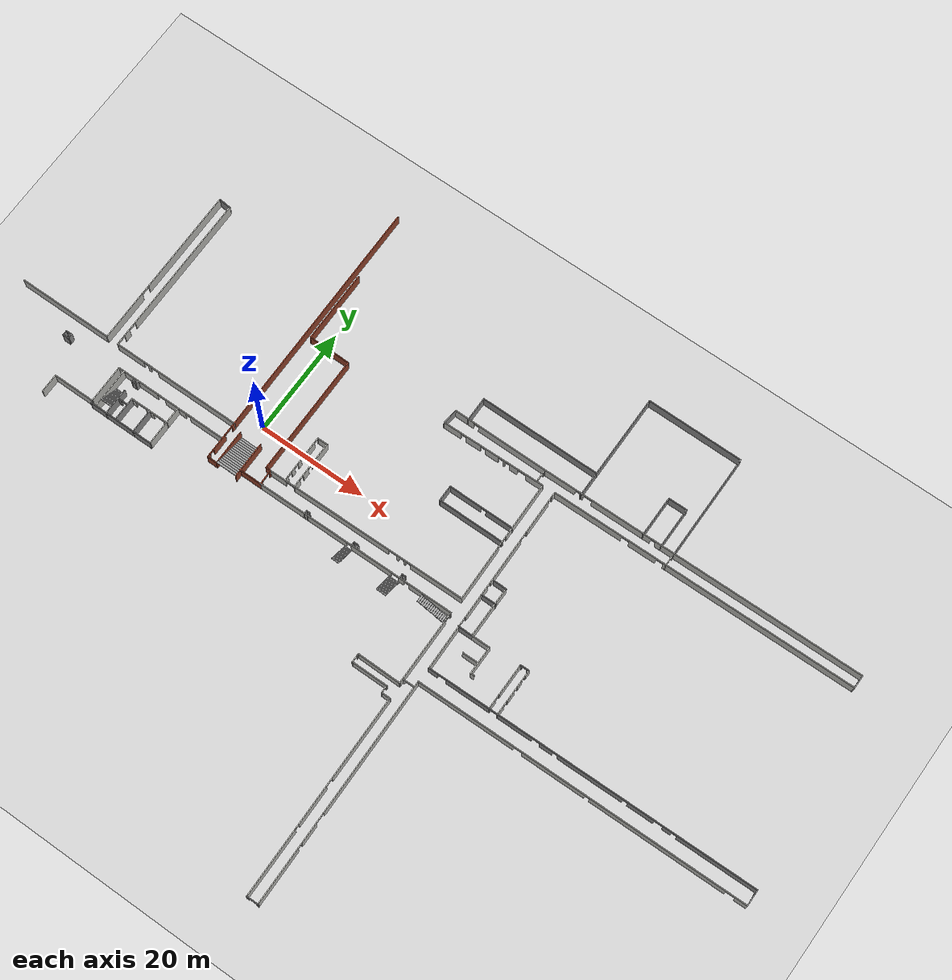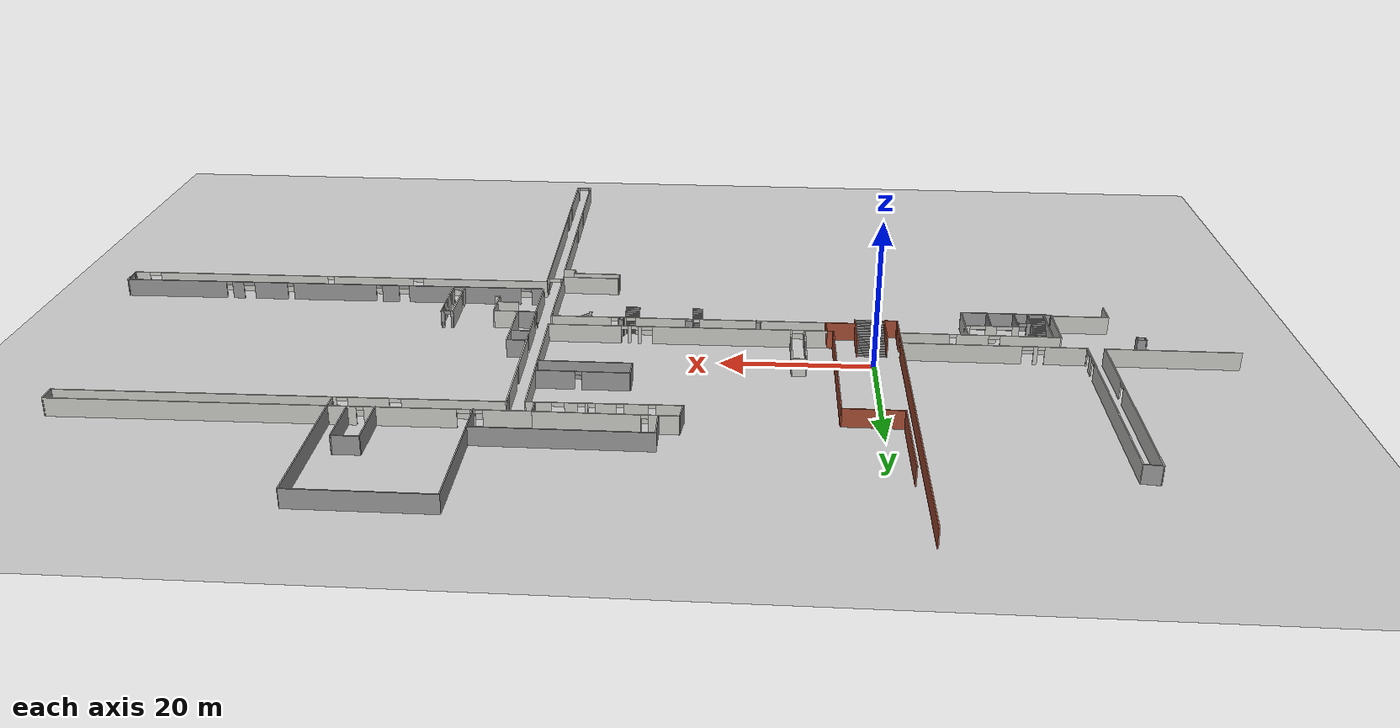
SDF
<sdf version="1.6">
 <world name="default">
  <light name="sun" type="directional">
   <pose>0 0 10 0 -0 0</pose>
   <diffuse>0.8 0.8 0.8 1</diffuse>
   <specular>0.2 0.2 0.2 1</specular>
   <attenuation>
    <range>1000</range>
    <constant>0.9</constant>
    <linear>0.01</linear>
    <quadratic>0.001</quadratic>
   </attenuation>
   <direction>-0.5 0.1 -0.9</direction>
   <spot><inner_angle>0</inner_angle><outer_angle>0</outer_angle><falloff>0</falloff></spot>
  </light>
  <model name="ground_plane">
   <static>1</static>
   <link name="link">
    <collision name="collision">
     <geometry><plane><normal>0 0 1</normal><size>100 100</size></plane></geometry>
     <surface><friction><ode><mu>100</mu><mu2>50</mu2></ode></friction></surface>
    </collision>
    <visual name="visual">
     <cast_shadows>0</cast_shadows>
     <geometry><plane><normal>0 0 1</normal><size>100 100</size></plane></geometry>
     <material>
      <script><uri>file://media/materials/scripts/gazebo.material</uri><name>Gazebo/Grey</name></script>
     </material>
    </visual>
   </link>
  </model>
  <gravity>0 0 -9.8</gravity>
  <magnetic_field>6e-06 2.3e-05 -4.2e-05</magnetic_field>
  <atmosphere type="adiabatic"/>
  <physics type="ode">
   <max_step_size>0.001</max_step_size>
   <real_time_factor>1</real_time_factor>
   <real_time_update_rate>1000</real_time_update_rate>
  </physics>
  <scene><ambient>0.4 0.4 0.4 1</ambient><background>0.7 0.7 0.7 1</background><shadows>1</shadows></scene>
  <spherical_coordinates>
   <surface_model>EARTH_WGS84</surface_model>
   <latitude_deg>0</latitude_deg>
   <longitude_deg>0</longitude_deg>
   <elevation>0</elevation>
   <heading_deg>0</heading_deg>
  </spherical_coordinates>
  <model name="hospital_LG_detailed">
   <pose>51.8521 -11.413 0 0 -0 0</pose>
   <link name="Stairs_0">
    <visual name="Stairs_0_Visual_0">
     <pose>-51.7603 7.83355 0.083333 0 -0 0</pose>
     <geometry><box><size>3.86299 0.42395 0.166667</size></box></geometry>
     <material>
      <script><uri>file://media/materials/scripts/gazebo.material</uri><name>Gazebo/Grey</name></script>
      <ambient>1 1 1 1</ambient>
     </material>
     <meta><layer>0</layer></meta>
    </visual>
    <collision name="Stairs_0_Collision_0">
     <geometry><box><size>3.86299 0.42395 0.166667</size></box></geometry>
     <pose>-51.7603 7.83355 0.083333 0 -0 0</pose>
    </collision>
    <visual name="Stairs_0_Visual_1">
     <pose>-51.7603 7.4096 0.25 0 -0 0</pose>
     <geometry><box><size>3.86299 0.42395 0.166667</size></box></geometry>
     <material>
      <script><uri>file://media/materials/scripts/gazebo.material</uri><name>Gazebo/Grey</name></script>
      <ambient>1 1 1 1</ambient>
     </material>
     <meta><layer>0</layer></meta>
    </visual>
    <collision name="Stairs_0_Collision_1">
     <geometry><box><size>3.86299 0.42395 0.166667</size></box></geometry>
     <pose>-51.7603 7.4096 0.25 0 -0 0</pose>
    </collision>
    <visual name="Stairs_0_Visual_2">
     <pose>-51.7603 6.98565 0.416667 0 -0 0</pose>
     <geometry><box><size>3.86299 0.42395 0.166667</size></box></geometry>
     <material>
      <script><uri>file://media/materials/scripts/gazebo.material</uri><name>Gazebo/Grey</name></script>
      <ambient>1 1 1 1</ambient>
     </material>
     <meta><layer>0</layer></meta>
    </visual>
    <collision name="Stairs_0_Collision_2">
     <geometry><box><size>3.86299 0.42395 0.166667</size></box></geometry>
     <pose>-51.7603 6.98565 0.416667 0 -0 0</pose>
    </collision>
    <visual name="Stairs_0_Visual_3">
     <pose>-51.7603 6.5617 0.583333 0 -0 0</pose>
     <geometry><box><size>3.86299 0.42395 0.166667</size></box></geometry>
     <material>
      <script><uri>file://media/materials/scripts/gazebo.material</uri><name>Gazebo/Grey</name></script>
      <ambient>1 1 1 1</ambient>
     </material>
     <meta><layer>0</layer></meta>
    </visual>
    <collision name="Stairs_0_Collision_3">
     <geometry><box><size>3.86299 0.42395 0.166667</size></box></geometry>
     <pose>-51.7603 6.5617 0.583333 0 -0 0</pose>
    </collision>
    <visual name="Stairs_0_Visual_4">
     <pose>-51.7603 6.13775 0.75 0 -0 0</pose>
     <geometry><box><size>3.86299 0.42395 0.166667</size></box></geometry>
     <material>
      <script><uri>file://media/materials/scripts/gazebo.material</uri><name>Gazebo/Grey</name></script>
      <ambient>1 1 1 1</ambient>
     </material>
     <meta><layer>0</layer></meta>
    </visual>
    <collision name="Stairs_0_Collision_4">
     <geometry><box><size>3.86299 0.42395 0.166667</size></box></geometry>
     <pose>-51.7603 6.13775 0.75 0 -0 0</pose>
    </collision>
    <visual name="Stairs_0_Visual_5">
     <pose>-51.7603 5.7138 0.916667 0 -0 0</pose>
     <geometry><box><size>3.86299 0.42395 0.166667</size></box></geometry>
     <material>
      <script><uri>file://media/materials/scripts/gazebo.material</uri><name>Gazebo/Grey</name></script>
      <ambient>1 1 1 1</ambient>
     </material>
     <meta><layer>0</layer></meta>
    </visual>
    <collision name="Stairs_0_Collision_5">
     <geometry><box><size>3.86299 0.42395 0.166667</size></box></geometry>
     <pose>-51.7603 5.7138 0.916667 0 -0 0</pose>
    </collision>
    <visual name="Stairs_0_Visual_6">
     <pose>-51.7603 5.28985 1.08333 0 -0 0</pose>
     <geometry><box><size>3.86299 0.42395 0.166667</size></box></geometry>
     <material>
      <script><uri>file://media/materials/scripts/gazebo.material</uri><name>Gazebo/Grey</name></script>
      <ambient>1 1 1 1</ambient>
     </material>
     <meta><layer>0</layer></meta>
    </visual>
    <collision name="Stairs_0_Collision_6">
     <geometry><box><size>3.86299 0.42395 0.166667</size></box></geometry>
     <pose>-51.7603 5.28985 1.08333 0 -0 0</pose>
    </collision>
    <visual name="Stairs_0_Visual_7">
     <pose>-51.7603 4.8659 1.25 0 -0 0</pose>
     <geometry><box><size>3.86299 0.42395 0.166667</size></box></geometry>
     <material>
      <script><uri>file://media/materials/scripts/gazebo.material</uri><name>Gazebo/Grey</name></script>
      <ambient>1 1 1 1</ambient>
     </material>
     <meta><layer>0</layer></meta>
    </visual>
    <collision name="Stairs_0_Collision_7">
     <geometry><box><size>3.86299 0.42395 0.166667</size></box></geometry>
     <pose>-51.7603 4.8659 1.25 0 -0 0</pose>
    </collision>
    <visual name="Stairs_0_Visual_8">
     <pose>-51.7603 4.44195 1.41667 0 -0 0</pose>
     <geometry><box><size>3.86299 0.42395 0.166667</size></box></geometry>
     <material>
      <script><uri>file://media/materials/scripts/gazebo.material</uri><name>Gazebo/Grey</name></script>
      <ambient>1 1 1 1</ambient>
     </material>
     <meta><layer>0</layer></meta>
    </visual>
    <collision name="Stairs_0_Collision_8">
     <geometry><box><size>3.86299 0.42395 0.166667</size></box></geometry>
     <pose>-51.7603 4.44195 1.41667 0 -0 0</pose>
    </collision>
    <visual name="Stairs_0_Visual_9">
     <pose>-51.7603 4.018 1.58333 0 -0 0</pose>
     <geometry><box><size>3.86299 0.42395 0.166667</size></box></geometry>
     <material>
      <script><uri>file://media/materials/scripts/gazebo.material</uri><name>Gazebo/Grey</name></script>
      <ambient>1 1 1 1</ambient>
     </material>
     <meta><layer>0</layer></meta>
    </visual>
    <collision name="Stairs_0_Collision_9">
     <geometry><box><size>3.86299 0.42395 0.166667</size></box></geometry>
     <pose>-51.7603 4.018 1.58333 0 -0 0</pose>
    </collision>
    <visual name="Stairs_0_Visual_10">
     <pose>-51.7603 3.59405 1.75 0 -0 0</pose>
     <geometry><box><size>3.86299 0.42395 0.166667</size></box></geometry>
     <material>
      <script><uri>file://media/materials/scripts/gazebo.material</uri><name>Gazebo/Grey</name></script>
      <ambient>1 1 1 1</ambient>
     </material>
     <meta><layer>0</layer></meta>
    </visual>
    <collision name="Stairs_0_Collision_10">
     <geometry><box><size>3.86299 0.42395 0.166667</size></box></geometry>
     <pose>-51.7603 3.59405 1.75 0 -0 0</pose>
    </collision>
    <visual name="Stairs_0_Visual_11">
     <pose>-51.7603 3.1701 1.91667 0 -0 0</pose>
     <geometry><box><size>3.86299 0.42395 0.166667</size></box></geometry>
     <material>
      <script><uri>file://media/materials/scripts/gazebo.material</uri><name>Gazebo/Grey</name></script>
      <ambient>1 1 1 1</ambient>
     </material>
     <meta><layer>0</layer></meta>
    </visual>
    <collision name="Stairs_0_Collision_11">
     <geometry><box><size>3.86299 0.42395 0.166667</size></box></geometry>
     <pose>-51.7603 3.1701 1.91667 0 -0 0</pose>
    </collision>
    <visual name="Stairs_0_Visual_12">
     <pose>-51.7603 2.74615 2.08333 0 -0 0</pose>
     <geometry><box><size>3.86299 0.42395 0.166667</size></box></geometry>
     <material>
      <script><uri>file://media/materials/scripts/gazebo.material</uri><name>Gazebo/Grey</name></script>
      <ambient>1 1 1 1</ambient>
     </material>
     <meta><layer>0</layer></meta>
    </visual>
    <collision name="Stairs_0_Collision_12">
     <geometry><box><size>3.86299 0.42395 0.166667</size></box></geometry>
     <pose>-51.7603 2.74615 2.08333 0 -0 0</pose>
    </collision>
    <visual name="Stairs_0_Visual_13">
     <pose>-51.7603 2.3222 2.25 0 -0 0</pose>
     <geometry><box><size>3.86299 0.42395 0.166667</size></box></geometry>
     <material>
      <script><uri>file://media/materials/scripts/gazebo.material</uri><name>Gazebo/Grey</name></script>
      <ambient>1 1 1 1</ambient>
     </material>
     <meta><layer>0</layer></meta>
    </visual>
    <collision name="Stairs_0_Collision_13">
     <geometry><box><size>3.86299 0.42395 0.166667</size></box></geometry>
     <pose>-51.7603 2.3222 2.25 0 -0 0</pose>
    </collision>
    <visual name="Stairs_0_Visual_14">
     <pose>-51.7603 1.89825 2.41667 0 -0 0</pose>
     <geometry><box><size>3.86299 0.42395 0.166667</size></box></geometry>
     <material>
      <script><uri>file://media/materials/scripts/gazebo.material</uri><name>Gazebo/Grey</name></script>
      <ambient>1 1 1 1</ambient>
     </material>
     <meta><layer>0</layer></meta>
    </visual>
    <collision name="Stairs_0_Collision_14">
     <geometry><box><size>3.86299 0.42395 0.166667</size></box></geometry>
     <pose>-51.7603 1.89825 2.41667 0 -0 0</pose>
    </collision>
   </link>
   <link name="Stairs_1">
    <visual name="Stairs_1_Visual_0">
     <pose>-19.4385 2.82184 0.083333 0 -0 0</pose>
     <geometry><box><size>1.94936 0.233333 0.166667</size></box></geometry>
     <material>
      <script><uri>file://media/materials/scripts/gazebo.material</uri><name>Gazebo/Grey</name></script>
      <ambient>1 1 1 1</ambient>
     </material>
     <meta><layer>0</layer></meta>
    </visual>
    <collision name="Stairs_1_Collision_0">
     <geometry><box><size>1.94936 0.233333 0.166667</size></box></geometry>
     <pose>-19.4385 2.82184 0.083333 0 -0 0</pose>
    </collision>
    <visual name="Stairs_1_Visual_1">
     <pose>-19.4385 2.58851 0.25 0 -0 0</pose>
     <geometry><box><size>1.94936 0.233333 0.166667</size></box></geometry>
     <material>
      <script><uri>file://media/materials/scripts/gazebo.material</uri><name>Gazebo/Grey</name></script>
      <ambient>1 1 1 1</ambient>
     </material>
     <meta><layer>0</layer></meta>
    </visual>
    <collision name="Stairs_1_Collision_1">
     <geometry><box><size>1.94936 0.233333 0.166667</size></box></geometry>
     <pose>-19.4385 2.58851 0.25 0 -0 0</pose>
    </collision>
    <visual name="Stairs_1_Visual_2">
     <pose>-19.4385 2.35518 0.416667 0 -0 0</pose>
     <geometry><box><size>1.94936 0.233333 0.166667</size></box></geometry>
     <material>
      <script><uri>file://media/materials/scripts/gazebo.material</uri><name>Gazebo/Grey</name></script>
      <ambient>1 1 1 1</ambient>
     </material>
     <meta><layer>0</layer></meta>
    </visual>
    <collision name="Stairs_1_Collision_2">
     <geometry><box><size>1.94936 0.233333 0.166667</size></box></geometry>
     <pose>-19.4385 2.35518 0.416667 0 -0 0</pose>
    </collision>
    <visual name="Stairs_1_Visual_3">
     <pose>-19.4385 2.12184 0.583333 0 -0 0</pose>
     <geometry><box><size>1.94936 0.233333 0.166667</size></box></geometry>
     <material>
      <script><uri>file://media/materials/scripts/gazebo.material</uri><name>Gazebo/Grey</name></script>
      <ambient>1 1 1 1</ambient>
     </material>
     <meta><layer>0</layer></meta>
    </visual>
    <collision name="Stairs_1_Collision_3">
     <geometry><box><size>1.94936 0.233333 0.166667</size></box></geometry>
     <pose>-19.4385 2.12184 0.583333 0 -0 0</pose>
    </collision>
    <visual name="Stairs_1_Visual_4">
     <pose>-19.4385 1.88851 0.75 0 -0 0</pose>
     <geometry><box><size>1.94936 0.233333 0.166667</size></box></geometry>
     <material>
      <script><uri>file://media/materials/scripts/gazebo.material</uri><name>Gazebo/Grey</name></script>
      <ambient>1 1 1 1</ambient>
     </material>
     <meta><layer>0</layer></meta>
    </visual>
    <collision name="Stairs_1_Collision_4">
     <geometry><box><size>1.94936 0.233333 0.166667</size></box></geometry>
     <pose>-19.4385 1.88851 0.75 0 -0 0</pose>
    </collision>
    <visual name="Stairs_1_Visual_5">
     <pose>-19.4385 1.65518 0.916667 0 -0 0</pose>
     <geometry><box><size>1.94936 0.233333 0.166667</size></box></geometry>
     <material>
      <script><uri>file://media/materials/scripts/gazebo.material</uri><name>Gazebo/Grey</name></script>
      <ambient>1 1 1 1</ambient>
     </material>
     <meta><layer>0</layer></meta>
    </visual>
    <collision name="Stairs_1_Collision_5">
     <geometry><box><size>1.94936 0.233333 0.166667</size></box></geometry>
     <pose>-19.4385 1.65518 0.916667 0 -0 0</pose>
    </collision>
    <visual name="Stairs_1_Visual_6">
     <pose>-19.4385 1.42184 1.08333 0 -0 0</pose>
     <geometry><box><size>1.94936 0.233333 0.166667</size></box></geometry>
     <material>
      <script><uri>file://media/materials/scripts/gazebo.material</uri><name>Gazebo/Grey</name></script>
      <ambient>1 1 1 1</ambient>
     </material>
     <meta><layer>0</layer></meta>
    </visual>
    <collision name="Stairs_1_Collision_6">
     <geometry><box><size>1.94936 0.233333 0.166667</size></box></geometry>
     <pose>-19.4385 1.42184 1.08333 0 -0 0</pose>
    </collision>
    <visual name="Stairs_1_Visual_7">
     <pose>-19.4385 1.18851 1.25 0 -0 0</pose>
     <geometry><box><size>1.94936 0.233333 0.166667</size></box></geometry>
     <material>
      <script><uri>file://media/materials/scripts/gazebo.material</uri><name>Gazebo/Grey</name></script>
      <ambient>1 1 1 1</ambient>
     </material>
     <meta><layer>0</layer></meta>
    </visual>
    <collision name="Stairs_1_Collision_7">
     <geometry><box><size>1.94936 0.233333 0.166667</size></box></geometry>
     <pose>-19.4385 1.18851 1.25 0 -0 0</pose>
    </collision>
    <visual name="Stairs_1_Visual_8">
     <pose>-19.4385 0.955175 1.41667 0 -0 0</pose>
     <geometry><box><size>1.94936 0.233333 0.166667</size></box></geometry>
     <material>
      <script><uri>file://media/materials/scripts/gazebo.material</uri><name>Gazebo/Grey</name></script>
      <ambient>1 1 1 1</ambient>
     </material>
     <meta><layer>0</layer></meta>
    </visual>
    <collision name="Stairs_1_Collision_8">
     <geometry><box><size>1.94936 0.233333 0.166667</size></box></geometry>
     <pose>-19.4385 0.955175 1.41667 0 -0 0</pose>
    </collision>
    <visual name="Stairs_1_Visual_9">
     <pose>-19.4385 0.721842 1.58333 0 -0 0</pose>
     <geometry><box><size>1.94936 0.233333 0.166667</size></box></geometry>
     <material>
      <script><uri>file://media/materials/scripts/gazebo.material</uri><name>Gazebo/Grey</name></script>
      <ambient>1 1 1 1</ambient>
     </material>
     <meta><layer>0</layer></meta>
    </visual>
    <collision name="Stairs_1_Collision_9">
     <geometry><box><size>1.94936 0.233333 0.166667</size></box></geometry>
     <pose>-19.4385 0.721842 1.58333 0 -0 0</pose>
    </collision>
    <visual name="Stairs_1_Visual_10">
     <pose>-19.4385 0.488509 1.75 0 -0 0</pose>
     <geometry><box><size>1.94936 0.233333 0.166667</size></box></geometry>
     <material>
      <script><uri>file://media/materials/scripts/gazebo.material</uri><name>Gazebo/Grey</name></script>
      <ambient>1 1 1 1</ambient>
     </material>
     <meta><layer>0</layer></meta>
    </visual>
    <collision name="Stairs_1_Collision_10">
     <geometry><box><size>1.94936 0.233333 0.166667</size></box></geometry>
     <pose>-19.4385 0.488509 1.75 0 -0 0</pose>
    </collision>
    <visual name="Stairs_1_Visual_11">
     <pose>-19.4385 0.255176 1.91667 0 -0 0</pose>
     <geometry><box><size>1.94936 0.233333 0.166667</size></box></geometry>
     <material>
      <script><uri>file://media/materials/scripts/gazebo.material</uri><name>Gazebo/Grey</name></script>
      <ambient>1 1 1 1</ambient>
     </material>
     <meta><layer>0</layer></meta>
    </visual>
    <collision name="Stairs_1_Collision_11">
     <geometry><box><size>1.94936 0.233333 0.166667</size></box></geometry>
     <pose>-19.4385 0.255176 1.91667 0 -0 0</pose>
    </collision>
    <visual name="Stairs_1_Visual_12">
     <pose>-19.4385 0.021842 2.08333 0 -0 0</pose>
     <geometry><box><size>1.94936 0.233333 0.166667</size></box></geometry>
     <material>
      <script><uri>file://media/materials/scripts/gazebo.material</uri><name>Gazebo/Grey</name></script>
      <ambient>1 1 1 1</ambient>
     </material>
     <meta><layer>0</layer></meta>
    </visual>
    <collision name="Stairs_1_Collision_12">
     <geometry><box><size>1.94936 0.233333 0.166667</size></box></geometry>
     <pose>-19.4385 0.021842 2.08333 0 -0 0</pose>
    </collision>
    <visual name="Stairs_1_Visual_13">
     <pose>-19.4385 -0.211491 2.25 0 -0 0</pose>
     <geometry><box><size>1.94936 0.233333 0.166667</size></box></geometry>
     <material>
      <script><uri>file://media/materials/scripts/gazebo.material</uri><name>Gazebo/Grey</name></script>
      <ambient>1 1 1 1</ambient>
     </material>
     <meta><layer>0</layer></meta>
    </visual>
    <collision name="Stairs_1_Collision_13">
     <geometry><box><size>1.94936 0.233333 0.166667</size></box></geometry>
     <pose>-19.4385 -0.211491 2.25 0 -0 0</pose>
    </collision>
    <visual name="Stairs_1_Visual_14">
     <pose>-19.4385 -0.444824 2.41667 0 -0 0</pose>
     <geometry><box><size>1.94936 0.233333 0.166667</size></box></geometry>
     <material>
      <script><uri>file://media/materials/scripts/gazebo.material</uri><name>Gazebo/Grey</name></script>
      <ambient>1 1 1 1</ambient>
     </material>
     <meta><layer>0</layer></meta>
    </visual>
    <collision name="Stairs_1_Collision_14">
     <geometry><box><size>1.94936 0.233333 0.166667</size></box></geometry>
     <pose>-19.4385 -0.444824 2.41667 0 -0 0</pose>
    </collision>
   </link>
   <link name="Stairs_2">
    <visual name="Stairs_2_Visual_0">
     <pose>-8.86162 2.21028 0.083333 0 -0 -1.5708</pose>
     <geometry><box><size>1.27354 0.351869 0.166667</size></box></geometry>
     <material>
      <script><uri>file://media/materials/scripts/gazebo.material</uri><name>Gazebo/Grey</name></script>
      <ambient>1 1 1 1</ambient>
     </material>
     <meta><layer>0</layer></meta>
    </visual>
    <collision name="Stairs_2_Collision_0">
     <geometry><box><size>1.27354 0.351869 0.166667</size></box></geometry>
     <pose>-8.86162 2.21028 0.083333 0 -0 -1.5708</pose>
    </collision>
    <visual name="Stairs_2_Visual_1">
     <pose>-9.21349 2.21028 0.25 0 -0 -1.5708</pose>
     <geometry><box><size>1.27354 0.351869 0.166667</size></box></geometry>
     <material>
      <script><uri>file://media/materials/scripts/gazebo.material</uri><name>Gazebo/Grey</name></script>
      <ambient>1 1 1 1</ambient>
     </material>
     <meta><layer>0</layer></meta>
    </visual>
    <collision name="Stairs_2_Collision_1">
     <geometry><box><size>1.27354 0.351869 0.166667</size></box></geometry>
     <pose>-9.21349 2.21028 0.25 0 -0 -1.5708</pose>
    </collision>
    <visual name="Stairs_2_Visual_2">
     <pose>-9.56536 2.21028 0.416667 0 -0 -1.5708</pose>
     <geometry><box><size>1.27354 0.351869 0.166667</size></box></geometry>
     <material>
      <script><uri>file://media/materials/scripts/gazebo.material</uri><name>Gazebo/Grey</name></script>
      <ambient>1 1 1 1</ambient>
     </material>
     <meta><layer>0</layer></meta>
    </visual>
    <collision name="Stairs_2_Collision_2">
     <geometry><box><size>1.27354 0.351869 0.166667</size></box></geometry>
     <pose>-9.56536 2.21028 0.416667 0 -0 -1.5708</pose>
    </collision>
    <visual name="Stairs_2_Visual_3">
     <pose>-9.91723 2.21028 0.583333 0 -0 -1.5708</pose>
     <geometry><box><size>1.27354 0.351869 0.166667</size></box></geometry>
     <material>
      <script><uri>file://media/materials/scripts/gazebo.material</uri><name>Gazebo/Grey</name></script>
      <ambient>1 1 1 1</ambient>
     </material>
     <meta><layer>0</layer></meta>
    </visual>
    <collision name="Stairs_2_Collision_3">
     <geometry><box><size>1.27354 0.351869 0.166667</size></box></geometry>
     <pose>-9.91723 2.21028 0.583333 0 -0 -1.5708</pose>
    </collision>
    <visual name="Stairs_2_Visual_4">
     <pose>-10.2691 2.21028 0.75 0 -0 -1.5708</pose>
     <geometry><box><size>1.27354 0.351869 0.166667</size></box></geometry>
     <material>
      <script><uri>file://media/materials/scripts/gazebo.material</uri><name>Gazebo/Grey</name></script>
      <ambient>1 1 1 1</ambient>
     </material>
     <meta><layer>0</layer></meta>
    </visual>
    <collision name="Stairs_2_Collision_4">
     <geometry><box><size>1.27354 0.351869 0.166667</size></box></geometry>
     <pose>-10.2691 2.21028 0.75 0 -0 -1.5708</pose>
    </collision>
    <visual name="Stairs_2_Visual_5">
     <pose>-10.621 2.21028 0.916667 0 -0 -1.5708</pose>
     <geometry><box><size>1.27354 0.351869 0.166667</size></box></geometry>
     <material>
      <script><uri>file://media/materials/scripts/gazebo.material</uri><name>Gazebo/Grey</name></script>
      <ambient>1 1 1 1</ambient>
     </material>
     <meta><layer>0</layer></meta>
    </visual>
    <collision name="Stairs_2_Collision_5">
     <geometry><box><size>1.27354 0.351869 0.166667</size></box></geometry>
     <pose>-10.621 2.21028 0.916667 0 -0 -1.5708</pose>
    </collision>
    <visual name="Stairs_2_Visual_6">
     <pose>-10.9728 2.21028 1.08333 0 -0 -1.5708</pose>
     <geometry><box><size>1.27354 0.351869 0.166667</size></box></geometry>
     <material>
      <script><uri>file://media/materials/scripts/gazebo.material</uri><name>Gazebo/Grey</name></script>
      <ambient>1 1 1 1</ambient>
     </material>
     <meta><layer>0</layer></meta>
    </visual>
    <collision name="Stairs_2_Collision_6">
     <geometry><box><size>1.27354 0.351869 0.166667</size></box></geometry>
     <pose>-10.9728 2.21028 1.08333 0 -0 -1.5708</pose>
    </collision>
    <visual name="Stairs_2_Visual_7">
     <pose>-11.3247 2.21028 1.25 0 -0 -1.5708</pose>
     <geometry><box><size>1.27354 0.351869 0.166667</size></box></geometry>
     <material>
      <script><uri>file://media/materials/scripts/gazebo.material</uri><name>Gazebo/Grey</name></script>
      <ambient>1 1 1 1</ambient>
     </material>
     <meta><layer>0</layer></meta>
    </visual>
    <collision name="Stairs_2_Collision_7">
     <geometry><box><size>1.27354 0.351869 0.166667</size></box></geometry>
     <pose>-11.3247 2.21028 1.25 0 -0 -1.5708</pose>
    </collision>
    <visual name="Stairs_2_Visual_8">
     <pose>-11.6766 2.21028 1.41667 0 -0 -1.5708</pose>
     <geometry><box><size>1.27354 0.351869 0.166667</size></box></geometry>
     <material>
      <script><uri>file://media/materials/scripts/gazebo.material</uri><name>Gazebo/Grey</name></script>
      <ambient>1 1 1 1</ambient>
     </material>
     <meta><layer>0</layer></meta>
    </visual>
    <collision name="Stairs_2_Collision_8">
     <geometry><box><size>1.27354 0.351869 0.166667</size></box></geometry>
     <pose>-11.6766 2.21028 1.41667 0 -0 -1.5708</pose>
    </collision>
    <visual name="Stairs_2_Visual_9">
     <pose>-12.0284 2.21028 1.58333 0 -0 -1.5708</pose>
     <geometry><box><size>1.27354 0.351869 0.166667</size></box></geometry>
     <material>
      <script><uri>file://media/materials/scripts/gazebo.material</uri><name>Gazebo/Grey</name></script>
      <ambient>1 1 1 1</ambient>
     </material>
     <meta><layer>0</layer></meta>
    </visual>
    <collision name="Stairs_2_Collision_9">
     <geometry><box><size>1.27354 0.351869 0.166667</size></box></geometry>
     <pose>-12.0284 2.21028 1.58333 0 -0 -1.5708</pose>
    </collision>
    <visual name="Stairs_2_Visual_10">
     <pose>-12.3803 2.21028 1.75 0 -0 -1.5708</pose>
     <geometry><box><size>1.27354 0.351869 0.166667</size></box></geometry>
     <material>
      <script><uri>file://media/materials/scripts/gazebo.material</uri><name>Gazebo/Grey</name></script>
      <ambient>1 1 1 1</ambient>
     </material>
     <meta><layer>0</layer></meta>
    </visual>
    <collision name="Stairs_2_Collision_10">
     <geometry><box><size>1.27354 0.351869 0.166667</size></box></geometry>
     <pose>-12.3803 2.21028 1.75 0 -0 -1.5708</pose>
    </collision>
    <visual name="Stairs_2_Visual_11">
     <pose>-12.7322 2.21028 1.91667 0 -0 -1.5708</pose>
     <geometry><box><size>1.27354 0.351869 0.166667</size></box></geometry>
     <material>
      <script><uri>file://media/materials/scripts/gazebo.material</uri><name>Gazebo/Grey</name></script>
      <ambient>1 1 1 1</ambient>
     </material>
     <meta><layer>0</layer></meta>
    </visual>
    <collision name="Stairs_2_Collision_11">
     <geometry><box><size>1.27354 0.351869 0.166667</size></box></geometry>
     <pose>-12.7322 2.21028 1.91667 0 -0 -1.5708</pose>
    </collision>
    <visual name="Stairs_2_Visual_12">
     <pose>-13.0841 2.21028 2.08333 0 -0 -1.5708</pose>
     <geometry><box><size>1.27354 0.351869 0.166667</size></box></geometry>
     <material>
      <script><uri>file://media/materials/scripts/gazebo.material</uri><name>Gazebo/Grey</name></script>
      <ambient>1 1 1 1</ambient>
     </material>
     <meta><layer>0</layer></meta>
    </visual>
    <collision name="Stairs_2_Collision_12">
     <geometry><box><size>1.27354 0.351869 0.166667</size></box></geometry>
     <pose>-13.0841 2.21028 2.08333 0 -0 -1.5708</pose>
    </collision>
    <visual name="Stairs_2_Visual_13">
     <pose>-13.4359 2.21028 2.25 0 -0 -1.5708</pose>
     <geometry><box><size>1.27354 0.351869 0.166667</size></box></geometry>
     <material>
      <script><uri>file://media/materials/scripts/gazebo.material</uri><name>Gazebo/Grey</name></script>
      <ambient>1 1 1 1</ambient>
     </material>
     <meta><layer>0</layer></meta>
    </visual>
    <collision name="Stairs_2_Collision_13">
     <geometry><box><size>1.27354 0.351869 0.166667</size></box></geometry>
     <pose>-13.4359 2.21028 2.25 0 -0 -1.5708</pose>
    </collision>
    <visual name="Stairs_2_Visual_14">
     <pose>-13.7878 2.21028 2.41667 0 -0 -1.5708</pose>
     <geometry><box><size>1.27354 0.351869 0.166667</size></box></geometry>
     <material>
      <script><uri>file://media/materials/scripts/gazebo.material</uri><name>Gazebo/Grey</name></script>
      <ambient>1 1 1 1</ambient>
     </material>
     <meta><layer>0</layer></meta>
    </visual>
    <collision name="Stairs_2_Collision_14">
     <geometry><box><size>1.27354 0.351869 0.166667</size></box></geometry>
     <pose>-13.7878 2.21028 2.41667 0 -0 -1.5708</pose>
    </collision>
   </link>
   <link name="Stairs_3">
    <visual name="Stairs_3_Visual_0">
     <pose>-28.4104 2.7962 0.083333 0 -0 0</pose>
     <geometry><box><size>1.42214 0.233333 0.166667</size></box></geometry>
     <material>
      <script><uri>file://media/materials/scripts/gazebo.material</uri><name>Gazebo/Grey</name></script>
      <ambient>1 1 1 1</ambient>
     </material>
     <meta><layer>0</layer></meta>
    </visual>
    <collision name="Stairs_3_Collision_0">
     <geometry><box><size>1.42214 0.233333 0.166667</size></box></geometry>
     <pose>-28.4104 2.7962 0.083333 0 -0 0</pose>
    </collision>
    <visual name="Stairs_3_Visual_1">
     <pose>-28.4104 2.56286 0.25 0 -0 0</pose>
     <geometry><box><size>1.42214 0.233333 0.166667</size></box></geometry>
     <material>
      <script><uri>file://media/materials/scripts/gazebo.material</uri><name>Gazebo/Grey</name></script>
      <ambient>1 1 1 1</ambient>
     </material>
     <meta><layer>0</layer></meta>
    </visual>
    <collision name="Stairs_3_Collision_1">
     <geometry><box><size>1.42214 0.233333 0.166667</size></box></geometry>
     <pose>-28.4104 2.56286 0.25 0 -0 0</pose>
    </collision>
    <visual name="Stairs_3_Visual_2">
     <pose>-28.4104 2.32953 0.416667 0 -0 0</pose>
     <geometry><box><size>1.42214 0.233333 0.166667</size></box></geometry>
     <material>
      <script><uri>file://media/materials/scripts/gazebo.material</uri><name>Gazebo/Grey</name></script>
      <ambient>1 1 1 1</ambient>
     </material>
     <meta><layer>0</layer></meta>
    </visual>
    <collision name="Stairs_3_Collision_2">
     <geometry><box><size>1.42214 0.233333 0.166667</size></box></geometry>
     <pose>-28.4104 2.32953 0.416667 0 -0 0</pose>
    </collision>
    <visual name="Stairs_3_Visual_3">
     <pose>-28.4104 2.0962 0.583333 0 -0 0</pose>
     <geometry><box><size>1.42214 0.233333 0.166667</size></box></geometry>
     <material>
      <script><uri>file://media/materials/scripts/gazebo.material</uri><name>Gazebo/Grey</name></script>
      <ambient>1 1 1 1</ambient>
     </material>
     <meta><layer>0</layer></meta>
    </visual>
    <collision name="Stairs_3_Collision_3">
     <geometry><box><size>1.42214 0.233333 0.166667</size></box></geometry>
     <pose>-28.4104 2.0962 0.583333 0 -0 0</pose>
    </collision>
    <visual name="Stairs_3_Visual_4">
     <pose>-28.4104 1.86286 0.75 0 -0 0</pose>
     <geometry><box><size>1.42214 0.233333 0.166667</size></box></geometry>
     <material>
      <script><uri>file://media/materials/scripts/gazebo.material</uri><name>Gazebo/Grey</name></script>
      <ambient>1 1 1 1</ambient>
     </material>
     <meta><layer>0</layer></meta>
    </visual>
    <collision name="Stairs_3_Collision_4">
     <geometry><box><size>1.42214 0.233333 0.166667</size></box></geometry>
     <pose>-28.4104 1.86286 0.75 0 -0 0</pose>
    </collision>
    <visual name="Stairs_3_Visual_5">
     <pose>-28.4104 1.62953 0.916667 0 -0 0</pose>
     <geometry><box><size>1.42214 0.233333 0.166667</size></box></geometry>
     <material>
      <script><uri>file://media/materials/scripts/gazebo.material</uri><name>Gazebo/Grey</name></script>
      <ambient>1 1 1 1</ambient>
     </material>
     <meta><layer>0</layer></meta>
    </visual>
    <collision name="Stairs_3_Collision_5">
     <geometry><box><size>1.42214 0.233333 0.166667</size></box></geometry>
     <pose>-28.4104 1.62953 0.916667 0 -0 0</pose>
    </collision>
    <visual name="Stairs_3_Visual_6">
     <pose>-28.4104 1.3962 1.08333 0 -0 0</pose>
     <geometry><box><size>1.42214 0.233333 0.166667</size></box></geometry>
     <material>
      <script><uri>file://media/materials/scripts/gazebo.material</uri><name>Gazebo/Grey</name></script>
      <ambient>1 1 1 1</ambient>
     </material>
     <meta><layer>0</layer></meta>
    </visual>
    <collision name="Stairs_3_Collision_6">
     <geometry><box><size>1.42214 0.233333 0.166667</size></box></geometry>
     <pose>-28.4104 1.3962 1.08333 0 -0 0</pose>
    </collision>
    <visual name="Stairs_3_Visual_7">
     <pose>-28.4104 1.16287 1.25 0 -0 0</pose>
     <geometry><box><size>1.42214 0.233333 0.166667</size></box></geometry>
     <material>
      <script><uri>file://media/materials/scripts/gazebo.material</uri><name>Gazebo/Grey</name></script>
      <ambient>1 1 1 1</ambient>
     </material>
     <meta><layer>0</layer></meta>
    </visual>
    <collision name="Stairs_3_Collision_7">
     <geometry><box><size>1.42214 0.233333 0.166667</size></box></geometry>
     <pose>-28.4104 1.16287 1.25 0 -0 0</pose>
    </collision>
    <visual name="Stairs_3_Visual_8">
     <pose>-28.4104 0.929532 1.41667 0 -0 0</pose>
     <geometry><box><size>1.42214 0.233333 0.166667</size></box></geometry>
     <material>
      <script><uri>file://media/materials/scripts/gazebo.material</uri><name>Gazebo/Grey</name></script>
      <ambient>1 1 1 1</ambient>
     </material>
     <meta><layer>0</layer></meta>
    </visual>
    <collision name="Stairs_3_Collision_8">
     <geometry><box><size>1.42214 0.233333 0.166667</size></box></geometry>
     <pose>-28.4104 0.929532 1.41667 0 -0 0</pose>
    </collision>
    <visual name="Stairs_3_Visual_9">
     <pose>-28.4104 0.696199 1.58333 0 -0 0</pose>
     <geometry><box><size>1.42214 0.233333 0.166667</size></box></geometry>
     <material>
      <script><uri>file://media/materials/scripts/gazebo.material</uri><name>Gazebo/Grey</name></script>
      <ambient>1 1 1 1</ambient>
     </material>
     <meta><layer>0</layer></meta>
    </visual>
    <collision name="Stairs_3_Collision_9">
     <geometry><box><size>1.42214 0.233333 0.166667</size></box></geometry>
     <pose>-28.4104 0.696199 1.58333 0 -0 0</pose>
    </collision>
    <visual name="Stairs_3_Visual_10">
     <pose>-28.4104 0.462866 1.75 0 -0 0</pose>
     <geometry><box><size>1.42214 0.233333 0.166667</size></box></geometry>
     <material>
      <script><uri>file://media/materials/scripts/gazebo.material</uri><name>Gazebo/Grey</name></script>
      <ambient>1 1 1 1</ambient>
     </material>
     <meta><layer>0</layer></meta>
    </visual>
    <collision name="Stairs_3_Collision_10">
     <geometry><box><size>1.42214 0.233333 0.166667</size></box></geometry>
     <pose>-28.4104 0.462866 1.75 0 -0 0</pose>
    </collision>
    <visual name="Stairs_3_Visual_11">
     <pose>-28.4104 0.229532 1.91667 0 -0 0</pose>
     <geometry><box><size>1.42214 0.233333 0.166667</size></box></geometry>
     <material>
      <script><uri>file://media/materials/scripts/gazebo.material</uri><name>Gazebo/Grey</name></script>
      <ambient>1 1 1 1</ambient>
     </material>
     <meta><layer>0</layer></meta>
    </visual>
    <collision name="Stairs_3_Collision_11">
     <geometry><box><size>1.42214 0.233333 0.166667</size></box></geometry>
     <pose>-28.4104 0.229532 1.91667 0 -0 0</pose>
    </collision>
    <visual name="Stairs_3_Visual_12">
     <pose>-28.4104 -0.003801 2.08333 0 -0 0</pose>
     <geometry><box><size>1.42214 0.233333 0.166667</size></box></geometry>
     <material>
      <script><uri>file://media/materials/scripts/gazebo.material</uri><name>Gazebo/Grey</name></script>
      <ambient>1 1 1 1</ambient>
     </material>
     <meta><layer>0</layer></meta>
    </visual>
    <collision name="Stairs_3_Collision_12">
     <geometry><box><size>1.42214 0.233333 0.166667</size></box></geometry>
     <pose>-28.4104 -0.003801 2.08333 0 -0 0</pose>
    </collision>
    <visual name="Stairs_3_Visual_13">
     <pose>-28.4104 -0.237134 2.25 0 -0 0</pose>
     <geometry><box><size>1.42214 0.233333 0.166667</size></box></geometry>
     <material>
      <script><uri>file://media/materials/scripts/gazebo.material</uri><name>Gazebo/Grey</name></script>
      <ambient>1 1 1 1</ambient>
     </material>
     <meta><layer>0</layer></meta>
    </visual>
    <collision name="Stairs_3_Collision_13">
     <geometry><box><size>1.42214 0.233333 0.166667</size></box></geometry>
     <pose>-28.4104 -0.237134 2.25 0 -0 0</pose>
    </collision>
    <visual name="Stairs_3_Visual_14">
     <pose>-28.4104 -0.470468 2.41667 0 -0 0</pose>
     <geometry><box><size>1.42214 0.233333 0.166667</size></box></geometry>
     <material>
      <script><uri>file://media/materials/scripts/gazebo.material</uri><name>Gazebo/Grey</name></script>
      <ambient>1 1 1 1</ambient>
     </material>
     <meta><layer>0</layer></meta>
    </visual>
    <collision name="Stairs_3_Collision_14">
     <geometry><box><size>1.42214 0.233333 0.166667</size></box></geometry>
     <pose>-28.4104 -0.470468 2.41667 0 -0 0</pose>
    </collision>
   </link>
   <link name="Wall_0">
    <collision name="Wall_0_Collision">
     <geometry><box><size>6.5 0.15 2.5</size></box></geometry>
     <pose>0 0 1.25 0 -0 0</pose>
    </collision>
    <visual name="Wall_0_Visual">
     <pose>0 0 1.25 0 -0 0</pose>
     <geometry><box><size>6.5 0.15 2.5</size></box></geometry>
     <material>
      <script><uri>file://media/materials/scripts/gazebo.material</uri><name>Gazebo/Bricks</name></script>
      <ambient>1 1 1 1</ambient>
     </material>
     <meta><layer>0</layer></meta>
    </visual>
    <pose>-53.7185 4.89995 0 0 -0 -1.5708</pose>
   </link>
   <link name="Wall_10">
    <pose>-27.1821 5.83422 0 0 -0 0.009948</pose>
    <visual name="Wall_10_Visual_0">
     <pose>-17.1568 0 1.25 0 -0 0</pose>
     <geometry><box><size>3.16982 0.15 2.5</size></box></geometry>
     <material>
      <script><uri>file://media/materials/scripts/gazebo.material</uri><name>Gazebo/CeilingTiled</name></script>
      <ambient>1 1 1 1</ambient>
     </material>
     <meta><layer>0</layer></meta>
    </visual>
    <collision name="Wall_10_Collision_0">
     <geometry><box><size>3.16982 0.15 2.5</size></box></geometry>
     <pose>-17.1568 0 1.25 0 -0 0</pose>
    </collision>
    <visual name="Wall_10_Visual_1">
     <pose>-4.69451 0 1.25 0 -0 0</pose>
     <geometry><box><size>18.5953 0.15 2.5</size></box></geometry>
     <material>
      <script><uri>file://media/materials/scripts/gazebo.material</uri><name>Gazebo/CeilingTiled</name></script>
      <ambient>1 1 1 1</ambient>
     </material>
     <meta><layer>0</layer></meta>
    </visual>
    <collision name="Wall_10_Collision_1">
     <geometry><box><size>18.5953 0.15 2.5</size></box></geometry>
     <pose>-4.69451 0 1.25 0 -0 0</pose>
    </collision>
    <visual name="Wall_10_Visual_2">
     <pose>6.37471 0 1.25 0 -0 0</pose>
     <geometry><box><size>0.439418 0.15 2.5</size></box></geometry>
     <material>
      <script><uri>file://media/materials/scripts/gazebo.material</uri><name>Gazebo/CeilingTiled</name></script>
      <ambient>1 1 1 1</ambient>
     </material>
     <meta><layer>0</layer></meta>
    </visual>
    <collision name="Wall_10_Collision_2">
     <geometry><box><size>0.439418 0.15 2.5</size></box></geometry>
     <pose>6.37471 0 1.25 0 -0 0</pose>
    </collision>
    <visual name="Wall_10_Visual_3">
     <pose>7.69224 0 1.25 0 -0 0</pose>
     <geometry><box><size>0.39565 0.15 2.5</size></box></geometry>
     <material>
      <script><uri>file://media/materials/scripts/gazebo.material</uri><name>Gazebo/CeilingTiled</name></script>
      <ambient>1 1 1 1</ambient>
     </material>
     <meta><layer>0</layer></meta>
    </visual>
    <collision name="Wall_10_Collision_3">
     <geometry><box><size>0.39565 0.15 2.5</size></box></geometry>
     <pose>7.69224 0 1.25 0 -0 0</pose>
    </collision>
    <visual name="Wall_10_Visual_4">
     <pose>13.7659 0 1.25 0 -0 0</pose>
     <geometry><box><size>9.95166 0.15 2.5</size></box></geometry>
     <material>
      <script><uri>file://media/materials/scripts/gazebo.material</uri><name>Gazebo/CeilingTiled</name></script>
      <ambient>1 1 1 1</ambient>
     </material>
     <meta><layer>0</layer></meta>
    </visual>
    <collision name="Wall_10_Collision_4">
     <geometry><box><size>9.95166 0.15 2.5</size></box></geometry>
     <pose>13.7659 0 1.25 0 -0 0</pose>
    </collision>
    <visual name="Wall_10_Visual_5">
     <pose>-14.782 0 2.25 0 -0 0</pose>
     <geometry><box><size>1.57977 0.15 0.5</size></box></geometry>
     <material>
      <script><uri>file://media/materials/scripts/gazebo.material</uri><name>Gazebo/CeilingTiled</name></script>
      <ambient>1 1 1 1</ambient>
     </material>
     <meta><layer>0</layer></meta>
    </visual>
    <collision name="Wall_10_Collision_5">
     <geometry><box><size>1.57977 0.15 0.5</size></box></geometry>
     <pose>-14.782 0 2.25 0 -0 0</pose>
    </collision>
    <visual name="Wall_10_Visual_6">
     <pose>5.37906 0 2.25 0 -0 0</pose>
     <geometry><box><size>1.55189 0.15 0.5</size></box></geometry>
     <material>
      <script><uri>file://media/materials/scripts/gazebo.material</uri><name>Gazebo/CeilingTiled</name></script>
      <ambient>1 1 1 1</ambient>
     </material>
     <meta><layer>0</layer></meta>
    </visual>
    <collision name="Wall_10_Collision_6">
     <geometry><box><size>1.55189 0.15 0.5</size></box></geometry>
     <pose>5.37906 0 2.25 0 -0 0</pose>
    </collision>
    <visual name="Wall_10_Visual_7">
     <pose>7.04442 0 2.25 0 -0 0</pose>
     <geometry><box><size>0.9 0.15 0.5</size></box></geometry>
     <material>
      <script><uri>file://media/materials/scripts/gazebo.material</uri><name>Gazebo/CeilingTiled</name></script>
      <ambient>1 1 1 1</ambient>
     </material>
     <meta><layer>0</layer></meta>
    </visual>
    <collision name="Wall_10_Collision_7">
     <geometry><box><size>0.9 0.15 0.5</size></box></geometry>
     <pose>7.04442 0 2.25 0 -0 0</pose>
    </collision>
    <visual name="Wall_10_Visual_8">
     <pose>8.34007 0 2.25 0 -0 0</pose>
     <geometry><box><size>0.9 0.15 0.5</size></box></geometry>
     <material>
      <script><uri>file://media/materials/scripts/gazebo.material</uri><name>Gazebo/CeilingTiled</name></script>
      <ambient>1 1 1 1</ambient>
     </material>
     <meta><layer>0</layer></meta>
    </visual>
    <collision name="Wall_10_Collision_8">
     <geometry><box><size>0.9 0.15 0.5</size></box></geometry>
     <pose>8.34007 0 2.25 0 -0 0</pose>
    </collision>
   </link>
   <link name="Wall_11">
    <pose>-8.67103 17.5035 0 0 -0 1.58503</pose>
    <visual name="Wall_11_Visual_0">
     <pose>-6.35487 0 1.25 0 -0 0</pose>
     <geometry><box><size>10.3922 0.15 2.5</size></box></geometry>
     <material>
      <script><uri>file://media/materials/scripts/gazebo.material</uri><name>Gazebo/CeilingTiled</name></script>
      <ambient>1 1 1 1</ambient>
     </material>
     <meta><layer>0</layer></meta>
    </visual>
    <collision name="Wall_11_Collision_0">
     <geometry><box><size>10.3922 0.15 2.5</size></box></geometry>
     <pose>-6.35487 0 1.25 0 -0 0</pose>
    </collision>
    <visual name="Wall_11_Visual_1">
     <pose>-0.090557 0 1.25 0 -0 0</pose>
     <geometry><box><size>0.336415 0.15 2.5</size></box></geometry>
     <material>
      <script><uri>file://media/materials/scripts/gazebo.material</uri><name>Gazebo/CeilingTiled</name></script>
      <ambient>1 1 1 1</ambient>
     </material>
     <meta><layer>0</layer></meta>
    </visual>
    <collision name="Wall_11_Collision_1">
     <geometry><box><size>0.336415 0.15 2.5</size></box></geometry>
     <pose>-0.090557 0 1.25 0 -0 0</pose>
    </collision>
    <visual name="Wall_11_Visual_2">
     <pose>6.26431 0 1.25 0 -0 0</pose>
     <geometry><box><size>10.5733 0.15 2.5</size></box></geometry>
     <material>
      <script><uri>file://media/materials/scripts/gazebo.material</uri><name>Gazebo/CeilingTiled</name></script>
      <ambient>1 1 1 1</ambient>
     </material>
     <meta><layer>0</layer></meta>
    </visual>
    <collision name="Wall_11_Collision_2">
     <geometry><box><size>10.5733 0.15 2.5</size></box></geometry>
     <pose>6.26431 0 1.25 0 -0 0</pose>
    </collision>
    <visual name="Wall_11_Visual_3">
     <pose>-0.708764 0 2.25 0 -0 0</pose>
     <geometry><box><size>0.9 0.15 0.5</size></box></geometry>
     <material>
      <script><uri>file://media/materials/scripts/gazebo.material</uri><name>Gazebo/CeilingTiled</name></script>
      <ambient>1 1 1 1</ambient>
     </material>
     <meta><layer>0</layer></meta>
    </visual>
    <collision name="Wall_11_Collision_3">
     <geometry><box><size>0.9 0.15 0.5</size></box></geometry>
     <pose>-0.708764 0 2.25 0 -0 0</pose>
    </collision>
    <visual name="Wall_11_Visual_4">
     <pose>0.527651 0 2.25 0 -0 0</pose>
     <geometry><box><size>0.9 0.15 0.5</size></box></geometry>
     <material>
      <script><uri>file://media/materials/scripts/gazebo.material</uri><name>Gazebo/CeilingTiled</name></script>
      <ambient>1 1 1 1</ambient>
     </material>
     <meta><layer>0</layer></meta>
    </visual>
    <collision name="Wall_11_Collision_4">
     <geometry><box><size>0.9 0.15 0.5</size></box></geometry>
     <pose>0.527651 0 2.25 0 -0 0</pose>
    </collision>
   </link>
   <link name="Wall_13">
    <pose>-18.3592 28.7968 0 0 -0 -3.12256</pose>
    <visual name="Wall_13_Visual_0">
     <pose>-7.97779 0 1.25 0 -0 0</pose>
     <geometry><box><size>3.27194 0.15 2.5</size></box></geometry>
     <material>
      <script><uri>file://media/materials/scripts/gazebo.material</uri><name>Gazebo/CeilingTiled</name></script>
      <ambient>1 1 1 1</ambient>
     </material>
     <meta><layer>0</layer></meta>
    </visual>
    <collision name="Wall_13_Collision_0">
     <geometry><box><size>3.27194 0.15 2.5</size></box></geometry>
     <pose>-7.97779 0 1.25 0 -0 0</pose>
    </collision>
    <visual name="Wall_13_Visual_1">
     <pose>-3.98875 0 1.25 0 -0 0</pose>
     <geometry><box><size>1.56041 0.15 2.5</size></box></geometry>
     <material>
      <script><uri>file://media/materials/scripts/gazebo.material</uri><name>Gazebo/CeilingTiled</name></script>
      <ambient>1 1 1 1</ambient>
     </material>
     <meta><layer>0</layer></meta>
    </visual>
    <collision name="Wall_13_Collision_1">
     <geometry><box><size>1.56041 0.15 2.5</size></box></geometry>
     <pose>-3.98875 0 1.25 0 -0 0</pose>
    </collision>
    <visual name="Wall_13_Visual_2">
     <pose>-2.12344 0 1.25 0 -0 0</pose>
     <geometry><box><size>0.370227 0.15 2.5</size></box></geometry>
     <material>
      <script><uri>file://media/materials/scripts/gazebo.material</uri><name>Gazebo/CeilingTiled</name></script>
      <ambient>1 1 1 1</ambient>
     </material>
     <meta><layer>0</layer></meta>
    </visual>
    <collision name="Wall_13_Collision_2">
     <geometry><box><size>0.370227 0.15 2.5</size></box></geometry>
     <pose>-2.12344 0 1.25 0 -0 0</pose>
    </collision>
    <visual name="Wall_13_Visual_3">
     <pose>0.232285 0 1.25 0 -0 0</pose>
     <geometry><box><size>2.54121 0.15 2.5</size></box></geometry>
     <material>
      <script><uri>file://media/materials/scripts/gazebo.material</uri><name>Gazebo/CeilingTiled</name></script>
      <ambient>1 1 1 1</ambient>
     </material>
     <meta><layer>0</layer></meta>
    </visual>
    <collision name="Wall_13_Collision_3">
     <geometry><box><size>2.54121 0.15 2.5</size></box></geometry>
     <pose>0.232285 0 1.25 0 -0 0</pose>
    </collision>
    <visual name="Wall_13_Visual_4">
     <pose>3.84972 0 1.25 0 -0 0</pose>
     <geometry><box><size>2.89366 0.15 2.5</size></box></geometry>
     <material>
      <script><uri>file://media/materials/scripts/gazebo.material</uri><name>Gazebo/CeilingTiled</name></script>
      <ambient>1 1 1 1</ambient>
     </material>
     <meta><layer>0</layer></meta>
    </visual>
    <collision name="Wall_13_Collision_4">
     <geometry><box><size>2.89366 0.15 2.5</size></box></geometry>
     <pose>3.84972 0 1.25 0 -0 0</pose>
    </collision>
    <visual name="Wall_13_Visual_5">
     <pose>7.90516 0 1.25 0 -0 0</pose>
     <geometry><box><size>3.4172 0.15 2.5</size></box></geometry>
     <material>
      <script><uri>file://media/materials/scripts/gazebo.material</uri><name>Gazebo/CeilingTiled</name></script>
      <ambient>1 1 1 1</ambient>
     </material>
     <meta><layer>0</layer></meta>
    </visual>
    <collision name="Wall_13_Collision_5">
     <geometry><box><size>3.4172 0.15 2.5</size></box></geometry>
     <pose>7.90516 0 1.25 0 -0 0</pose>
    </collision>
    <visual name="Wall_13_Visual_6">
     <pose>-5.55539 0 2.25 0 -0 0</pose>
     <geometry><box><size>1.57286 0.15 0.5</size></box></geometry>
     <material>
      <script><uri>file://media/materials/scripts/gazebo.material</uri><name>Gazebo/CeilingTiled</name></script>
      <ambient>1 1 1 1</ambient>
     </material>
     <meta><layer>0</layer></meta>
    </visual>
    <collision name="Wall_13_Collision_6">
     <geometry><box><size>1.57286 0.15 0.5</size></box></geometry>
     <pose>-5.55539 0 2.25 0 -0 0</pose>
    </collision>
    <visual name="Wall_13_Visual_7">
     <pose>-2.75855 0 2.25 0 -0 0</pose>
     <geometry><box><size>0.9 0.15 0.5</size></box></geometry>
     <material>
      <script><uri>file://media/materials/scripts/gazebo.material</uri><name>Gazebo/CeilingTiled</name></script>
      <ambient>1 1 1 1</ambient>
     </material>
     <meta><layer>0</layer></meta>
    </visual>
    <collision name="Wall_13_Collision_7">
     <geometry><box><size>0.9 0.15 0.5</size></box></geometry>
     <pose>-2.75855 0 2.25 0 -0 0</pose>
    </collision>
    <visual name="Wall_13_Visual_8">
     <pose>-1.48832 0 2.25 0 -0 0</pose>
     <geometry><box><size>0.9 0.15 0.5</size></box></geometry>
     <material>
      <script><uri>file://media/materials/scripts/gazebo.material</uri><name>Gazebo/CeilingTiled</name></script>
      <ambient>1 1 1 1</ambient>
     </material>
     <meta><layer>0</layer></meta>
    </visual>
    <collision name="Wall_13_Collision_8">
     <geometry><box><size>0.9 0.15 0.5</size></box></geometry>
     <pose>-1.48832 0 2.25 0 -0 0</pose>
    </collision>
    <visual name="Wall_13_Visual_9">
     <pose>1.95289 0 2.25 0 -0 0</pose>
     <geometry><box><size>0.9 0.15 0.5</size></box></geometry>
     <material>
      <script><uri>file://media/materials/scripts/gazebo.material</uri><name>Gazebo/CeilingTiled</name></script>
      <ambient>1 1 1 1</ambient>
     </material>
     <meta><layer>0</layer></meta>
    </visual>
    <collision name="Wall_13_Collision_9">
     <geometry><box><size>0.9 0.15 0.5</size></box></geometry>
     <pose>1.95289 0 2.25 0 -0 0</pose>
    </collision>
    <visual name="Wall_13_Visual_10">
     <pose>5.74655 0 2.25 0 -0 0</pose>
     <geometry><box><size>0.9 0.15 0.5</size></box></geometry>
     <material>
      <script><uri>file://media/materials/scripts/gazebo.material</uri><name>Gazebo/CeilingTiled</name></script>
      <ambient>1 1 1 1</ambient>
     </material>
     <meta><layer>0</layer></meta>
    </visual>
    <collision name="Wall_13_Collision_10">
     <geometry><box><size>0.9 0.15 0.5</size></box></geometry>
     <pose>5.74655 0 2.25 0 -0 0</pose>
    </collision>
   </link>
   <link name="Wall_14">
    <collision name="Wall_14_Collision">
     <geometry><box><size>2.90995 0.15 2.5</size></box></geometry>
     <pose>0 0 1.25 0 -0 0</pose>
    </collision>
    <visual name="Wall_14_Visual">
     <pose>0 0 1.25 0 -0 0</pose>
     <geometry><box><size>2.90995 0.15 2.5</size></box></geometry>
     <material>
      <script><uri>file://media/materials/scripts/gazebo.material</uri><name>Gazebo/Grey</name></script>
      <ambient>1 1 1 1</ambient>
     </material>
     <meta><layer>0</layer></meta>
    </visual>
    <pose>-27.7494 29.986 0 0 -0 1.45527</pose>
   </link>
   <link name="Wall_15">
    <pose>-18.7903 31.3568 0 0 -0 0</pose>
    <visual name="Wall_15_Visual_0">
     <pose>-7.00157 0 1.25 0 -0 0</pose>
     <geometry><box><size>3.74685 0.15 2.5</size></box></geometry>
     <material>
      <script><uri>file://media/materials/scripts/gazebo.material</uri><name>Gazebo/CeilingTiled</name></script>
      <ambient>1 1 1 1</ambient>
     </material>
     <meta><layer>0</layer></meta>
    </visual>
    <collision name="Wall_15_Collision_0">
     <geometry><box><size>3.74685 0.15 2.5</size></box></geometry>
     <pose>-7.00157 0 1.25 0 -0 0</pose>
    </collision>
    <visual name="Wall_15_Visual_1">
     <pose>2.32343 0 1.25 0 -0 0</pose>
     <geometry><box><size>13.1031 0.15 2.5</size></box></geometry>
     <material>
      <script><uri>file://media/materials/scripts/gazebo.material</uri><name>Gazebo/CeilingTiled</name></script>
      <ambient>1 1 1 1</ambient>
     </material>
     <meta><layer>0</layer></meta>
    </visual>
    <collision name="Wall_15_Collision_1">
     <geometry><box><size>13.1031 0.15 2.5</size></box></geometry>
     <pose>2.32343 0 1.25 0 -0 0</pose>
    </collision>
    <visual name="Wall_15_Visual_2">
     <pose>-4.67815 0 2.25 0 -0 0</pose>
     <geometry><box><size>0.9 0.15 0.5</size></box></geometry>
     <material>
      <script><uri>file://media/materials/scripts/gazebo.material</uri><name>Gazebo/CeilingTiled</name></script>
      <ambient>1 1 1 1</ambient>
     </material>
     <meta><layer>0</layer></meta>
    </visual>
    <collision name="Wall_15_Collision_2">
     <geometry><box><size>0.9 0.15 0.5</size></box></geometry>
     <pose>-4.67815 0 2.25 0 -0 0</pose>
    </collision>
   </link>
   <link name="Wall_16">
    <pose>-9.99034 30.1818 0 0 -0 -1.5708</pose>
    <visual name="Wall_16_Visual_0">
     <pose>-1.01228 0 1.25 0 -0 0</pose>
     <geometry><box><size>0.475433 0.15 2.5</size></box></geometry>
     <material>
      <script><uri>file://media/materials/scripts/gazebo.material</uri><name>Gazebo/CeilingTiled</name></script>
      <ambient>1 1 1 1</ambient>
     </material>
     <meta><layer>0</layer></meta>
    </visual>
    <collision name="Wall_16_Collision_0">
     <geometry><box><size>0.475433 0.15 2.5</size></box></geometry>
     <pose>-1.01228 0 1.25 0 -0 0</pose>
    </collision>
    <visual name="Wall_16_Visual_1">
     <pose>1.03033 0 1.25 0 -0 0</pose>
     <geometry><box><size>0.439346 0.15 2.5</size></box></geometry>
     <material>
      <script><uri>file://media/materials/scripts/gazebo.material</uri><name>Gazebo/CeilingTiled</name></script>
      <ambient>1 1 1 1</ambient>
     </material>
     <meta><layer>0</layer></meta>
    </visual>
    <collision name="Wall_16_Collision_1">
     <geometry><box><size>0.439346 0.15 2.5</size></box></geometry>
     <pose>1.03033 0 1.25 0 -0 0</pose>
    </collision>
    <visual name="Wall_16_Visual_2">
     <pose>0.018044 0 2.25 0 -0 0</pose>
     <geometry><box><size>1.58522 0.15 0.5</size></box></geometry>
     <material>
      <script><uri>file://media/materials/scripts/gazebo.material</uri><name>Gazebo/CeilingTiled</name></script>
      <ambient>1 1 1 1</ambient>
     </material>
     <meta><layer>0</layer></meta>
    </visual>
    <collision name="Wall_16_Collision_2">
     <geometry><box><size>1.58522 0.15 0.5</size></box></geometry>
     <pose>0.018044 0 2.25 0 -0 0</pose>
    </collision>
   </link>
   <link name="Wall_19">
    <pose>19.8114 31.6969 0 0 -0 0.011412</pose>
    <visual name="Wall_19_Visual_0">
     <pose>-26.9038 0 1.25 0 -0 0</pose>
     <geometry><box><size>5.94974 0.15 2.5</size></box></geometry>
     <material>
      <script><uri>file://media/materials/scripts/gazebo.material</uri><name>Gazebo/CeilingTiled</name></script>
      <ambient>1 1 1 1</ambient>
     </material>
     <meta><layer>0</layer></meta>
    </visual>
    <collision name="Wall_19_Collision_0">
     <geometry><box><size>5.94974 0.15 2.5</size></box></geometry>
     <pose>-26.9038 0 1.25 0 -0 0</pose>
    </collision>
    <visual name="Wall_19_Visual_1">
     <pose>-22.7092 0 1.25 0 -0 0</pose>
     <geometry><box><size>0.639467 0.15 2.5</size></box></geometry>
     <material>
      <script><uri>file://media/materials/scripts/gazebo.material</uri><name>Gazebo/CeilingTiled</name></script>
      <ambient>1 1 1 1</ambient>
     </material>
     <meta><layer>0</layer></meta>
    </visual>
    <collision name="Wall_19_Collision_1">
     <geometry><box><size>0.639467 0.15 2.5</size></box></geometry>
     <pose>-22.7092 0 1.25 0 -0 0</pose>
    </collision>
    <visual name="Wall_19_Visual_2">
     <pose>-15.171 0 1.25 0 -0 0</pose>
     <geometry><box><size>11.2421 0.15 2.5</size></box></geometry>
     <material>
      <script><uri>file://media/materials/scripts/gazebo.material</uri><name>Gazebo/CeilingTiled</name></script>
      <ambient>1 1 1 1</ambient>
     </material>
     <meta><layer>0</layer></meta>
    </visual>
    <collision name="Wall_19_Collision_2">
     <geometry><box><size>11.2421 0.15 2.5</size></box></geometry>
     <pose>-15.171 0 1.25 0 -0 0</pose>
    </collision>
    <visual name="Wall_19_Visual_3">
     <pose>10.6144 0 1.25 0 -0 0</pose>
     <geometry><box><size>38.5287 0.15 2.5</size></box></geometry>
     <material>
      <script><uri>file://media/materials/scripts/gazebo.material</uri><name>Gazebo/CeilingTiled</name></script>
      <ambient>1 1 1 1</ambient>
     </material>
     <meta><layer>0</layer></meta>
    </visual>
    <collision name="Wall_19_Collision_3">
     <geometry><box><size>38.5287 0.15 2.5</size></box></geometry>
     <pose>10.6144 0 1.25 0 -0 0</pose>
    </collision>
    <visual name="Wall_19_Visual_4">
     <pose>-23.479 0 2.25 0 -0 0</pose>
     <geometry><box><size>0.9 0.15 0.5</size></box></geometry>
     <material>
      <script><uri>file://media/materials/scripts/gazebo.material</uri><name>Gazebo/CeilingTiled</name></script>
      <ambient>1 1 1 1</ambient>
     </material>
     <meta><layer>0</layer></meta>
    </visual>
    <collision name="Wall_19_Collision_4">
     <geometry><box><size>0.9 0.15 0.5</size></box></geometry>
     <pose>-23.479 0 2.25 0 -0 0</pose>
    </collision>
    <visual name="Wall_19_Visual_5">
     <pose>-21.5908 0 2.25 0 -0 0</pose>
     <geometry><box><size>1.59746 0.15 0.5</size></box></geometry>
     <material>
      <script><uri>file://media/materials/scripts/gazebo.material</uri><name>Gazebo/CeilingTiled</name></script>
      <ambient>1 1 1 1</ambient>
     </material>
     <meta><layer>0</layer></meta>
    </visual>
    <collision name="Wall_19_Collision_5">
     <geometry><box><size>1.59746 0.15 0.5</size></box></geometry>
     <pose>-21.5908 0 2.25 0 -0 0</pose>
    </collision>
    <visual name="Wall_19_Visual_6">
     <pose>-9.09996 0 2.25 0 -0 0</pose>
     <geometry><box><size>0.9 0.15 0.5</size></box></geometry>
     <material>
      <script><uri>file://media/materials/scripts/gazebo.material</uri><name>Gazebo/CeilingTiled</name></script>
      <ambient>1 1 1 1</ambient>
     </material>
     <meta><layer>0</layer></meta>
    </visual>
    <collision name="Wall_19_Collision_6">
     <geometry><box><size>0.9 0.15 0.5</size></box></geometry>
     <pose>-9.09996 0 2.25 0 -0 0</pose>
    </collision>
   </link>
   <link name="Wall_2">
    <collision name="Wall_2_Collision">
     <geometry><box><size>6.75 0.15 2.5</size></box></geometry>
     <pose>0 0 1.25 0 -0 0</pose>
    </collision>
    <visual name="Wall_2_Visual">
     <pose>0 0 1.25 0 -0 0</pose>
     <geometry><box><size>6.75 0.15 2.5</size></box></geometry>
     <material>
      <script><uri>file://media/materials/scripts/gazebo.material</uri><name>Gazebo/Bricks</name></script>
      <ambient>1 1 1 1</ambient>
     </material>
     <meta><layer>0</layer></meta>
    </visual>
    <pose>-49.8098 4.95745 0 0 -0 -1.5708</pose>
   </link>
   <link name="Wall_20">
    <collision name="Wall_20_Collision">
     <geometry><box><size>2.5 0.15 2.5</size></box></geometry>
     <pose>0 0 1.25 0 -0 0</pose>
    </collision>
    <visual name="Wall_20_Visual">
     <pose>0 0 1.25 0 -0 0</pose>
     <geometry><box><size>2.5 0.15 2.5</size></box></geometry>
     <material>
      <script><uri>file://media/materials/scripts/gazebo.material</uri><name>Gazebo/Grey</name></script>
      <ambient>1 1 1 1</ambient>
     </material>
     <meta><layer>0</layer></meta>
    </visual>
    <pose>49.6132 30.862 0 0 -0 -1.5708</pose>
   </link>
   <link name="Wall_21">
    <pose>21.5308 29.3985 0 0 -0 -3.13082</pose>
    <visual name="Wall_21_Visual_0">
     <pose>-10.3888 0 1.25 0 -0 0</pose>
     <geometry><box><size>35.5404 0.15 2.5</size></box></geometry>
     <material>
      <script><uri>file://media/materials/scripts/gazebo.material</uri><name>Gazebo/CeilingTiled</name></script>
      <ambient>1 1 1 1</ambient>
     </material>
     <meta><layer>0</layer></meta>
    </visual>
    <collision name="Wall_21_Collision_0">
     <geometry><box><size>35.5404 0.15 2.5</size></box></geometry>
     <pose>-10.3888 0 1.25 0 -0 0</pose>
    </collision>
    <visual name="Wall_21_Visual_1">
     <pose>11.2873 0 1.25 0 -0 0</pose>
     <geometry><box><size>5.11112 0.15 2.5</size></box></geometry>
     <material>
      <script><uri>file://media/materials/scripts/gazebo.material</uri><name>Gazebo/CeilingTiled</name></script>
      <ambient>1 1 1 1</ambient>
     </material>
     <meta><layer>0</layer></meta>
    </visual>
    <collision name="Wall_21_Collision_1">
     <geometry><box><size>5.11112 0.15 2.5</size></box></geometry>
     <pose>11.2873 0 1.25 0 -0 0</pose>
    </collision>
    <visual name="Wall_21_Visual_2">
     <pose>21.7323 0 1.25 0 -0 0</pose>
     <geometry><box><size>12.8533 0.15 2.5</size></box></geometry>
     <material>
      <script><uri>file://media/materials/scripts/gazebo.material</uri><name>Gazebo/CeilingTiled</name></script>
      <ambient>1 1 1 1</ambient>
     </material>
     <meta><layer>0</layer></meta>
    </visual>
    <collision name="Wall_21_Collision_2">
     <geometry><box><size>12.8533 0.15 2.5</size></box></geometry>
     <pose>21.7323 0 1.25 0 -0 0</pose>
    </collision>
    <visual name="Wall_21_Visual_3">
     <pose>8.05659 0 2.25 0 -0 0</pose>
     <geometry><box><size>1.35029 0.15 0.5</size></box></geometry>
     <material>
      <script><uri>file://media/materials/scripts/gazebo.material</uri><name>Gazebo/CeilingTiled</name></script>
      <ambient>1 1 1 1</ambient>
     </material>
     <meta><layer>0</layer></meta>
    </visual>
    <collision name="Wall_21_Collision_3">
     <geometry><box><size>1.35029 0.15 0.5</size></box></geometry>
     <pose>8.05659 0 2.25 0 -0 0</pose>
    </collision>
    <visual name="Wall_21_Visual_4">
     <pose>14.5743 0 2.25 0 -0 0</pose>
     <geometry><box><size>1.46286 0.15 0.5</size></box></geometry>
     <material>
      <script><uri>file://media/materials/scripts/gazebo.material</uri><name>Gazebo/CeilingTiled</name></script>
      <ambient>1 1 1 1</ambient>
     </material>
     <meta><layer>0</layer></meta>
    </visual>
    <collision name="Wall_21_Collision_4">
     <geometry><box><size>1.46286 0.15 0.5</size></box></geometry>
     <pose>14.5743 0 2.25 0 -0 0</pose>
    </collision>
   </link>
   <link name="Wall_23">
    <pose>-6.34809 11.4815 0 0 -0 -1.55855</pose>
    <visual name="Wall_23_Visual_0">
     <pose>-17.1986 0 1.25 0 -0 0</pose>
     <geometry><box><size>0.984488 0.15 2.5</size></box></geometry>
     <material>
      <script><uri>file://media/materials/scripts/gazebo.material</uri><name>Gazebo/CeilingTiled</name></script>
      <ambient>1 1 1 1</ambient>
     </material>
     <meta><layer>0</layer></meta>
    </visual>
    <collision name="Wall_23_Collision_0">
     <geometry><box><size>0.984488 0.15 2.5</size></box></geometry>
     <pose>-17.1986 0 1.25 0 -0 0</pose>
    </collision>
    <visual name="Wall_23_Visual_1">
     <pose>-12.6832 0 1.25 0 -0 0</pose>
     <geometry><box><size>6.2462 0.15 2.5</size></box></geometry>
     <material>
      <script><uri>file://media/materials/scripts/gazebo.material</uri><name>Gazebo/CeilingTiled</name></script>
      <ambient>1 1 1 1</ambient>
     </material>
     <meta><layer>0</layer></meta>
    </visual>
    <collision name="Wall_23_Collision_1">
     <geometry><box><size>6.2462 0.15 2.5</size></box></geometry>
     <pose>-12.6832 0 1.25 0 -0 0</pose>
    </collision>
    <visual name="Wall_23_Visual_2">
     <pose>-3.66014 0 1.25 0 -0 0</pose>
     <geometry><box><size>8.56539 0.15 2.5</size></box></geometry>
     <material>
      <script><uri>file://media/materials/scripts/gazebo.material</uri><name>Gazebo/CeilingTiled</name></script>
      <ambient>1 1 1 1</ambient>
     </material>
     <meta><layer>0</layer></meta>
    </visual>
    <collision name="Wall_23_Collision_2">
     <geometry><box><size>8.56539 0.15 2.5</size></box></geometry>
     <pose>-3.66014 0 1.25 0 -0 0</pose>
    </collision>
    <visual name="Wall_23_Visual_3">
     <pose>4.54792 0 1.25 0 -0 0</pose>
     <geometry><box><size>6.05074 0.15 2.5</size></box></geometry>
     <material>
      <script><uri>file://media/materials/scripts/gazebo.material</uri><name>Gazebo/CeilingTiled</name></script>
      <ambient>1 1 1 1</ambient>
     </material>
     <meta><layer>0</layer></meta>
    </visual>
    <collision name="Wall_23_Collision_3">
     <geometry><box><size>6.05074 0.15 2.5</size></box></geometry>
     <pose>4.54792 0 1.25 0 -0 0</pose>
    </collision>
    <visual name="Wall_23_Visual_4">
     <pose>13.4369 0 1.25 0 -0 0</pose>
     <geometry><box><size>8.50789 0.15 2.5</size></box></geometry>
     <material>
      <script><uri>file://media/materials/scripts/gazebo.material</uri><name>Gazebo/CeilingTiled</name></script>
      <ambient>1 1 1 1</ambient>
     </material>
     <meta><layer>0</layer></meta>
    </visual>
    <collision name="Wall_23_Collision_4">
     <geometry><box><size>8.50789 0.15 2.5</size></box></geometry>
     <pose>13.4369 0 1.25 0 -0 0</pose>
    </collision>
    <visual name="Wall_23_Visual_5">
     <pose>-16.2563 0 2.25 0 -0 0</pose>
     <geometry><box><size>0.9 0.15 0.5</size></box></geometry>
     <material>
      <script><uri>file://media/materials/scripts/gazebo.material</uri><name>Gazebo/CeilingTiled</name></script>
      <ambient>1 1 1 1</ambient>
     </material>
     <meta><layer>0</layer></meta>
    </visual>
    <collision name="Wall_23_Collision_5">
     <geometry><box><size>0.9 0.15 0.5</size></box></geometry>
     <pose>-16.2563 0 2.25 0 -0 0</pose>
    </collision>
    <visual name="Wall_23_Visual_6">
     <pose>-8.75149 0 2.25 0 -0 0</pose>
     <geometry><box><size>1.61732 0.15 0.5</size></box></geometry>
     <material>
      <script><uri>file://media/materials/scripts/gazebo.material</uri><name>Gazebo/CeilingTiled</name></script>
      <ambient>1 1 1 1</ambient>
     </material>
     <meta><layer>0</layer></meta>
    </visual>
    <collision name="Wall_23_Collision_6">
     <geometry><box><size>1.61732 0.15 0.5</size></box></geometry>
     <pose>-8.75149 0 2.25 0 -0 0</pose>
    </collision>
    <visual name="Wall_23_Visual_7">
     <pose>1.07256 0 2.25 0 -0 0</pose>
     <geometry><box><size>0.9 0.15 0.5</size></box></geometry>
     <material>
      <script><uri>file://media/materials/scripts/gazebo.material</uri><name>Gazebo/CeilingTiled</name></script>
      <ambient>1 1 1 1</ambient>
     </material>
     <meta><layer>0</layer></meta>
    </visual>
    <collision name="Wall_23_Collision_7">
     <geometry><box><size>0.9 0.15 0.5</size></box></geometry>
     <pose>1.07256 0 2.25 0 -0 0</pose>
    </collision>
    <visual name="Wall_23_Visual_8">
     <pose>8.37812 0 2.25 0 -0 0</pose>
     <geometry><box><size>1.60965 0.15 0.5</size></box></geometry>
     <material>
      <script><uri>file://media/materials/scripts/gazebo.material</uri><name>Gazebo/CeilingTiled</name></script>
      <ambient>1 1 1 1</ambient>
     </material>
     <meta><layer>0</layer></meta>
    </visual>
    <collision name="Wall_23_Collision_8">
     <geometry><box><size>1.60965 0.15 0.5</size></box></geometry>
     <pose>8.37812 0 2.25 0 -0 0</pose>
    </collision>
   </link>
   <link name="Wall_24">
    <pose>24.123 -5.8189 0 0 -0 0.011089</pose>
    <visual name="Wall_24_Visual_0">
     <pose>-29.4346 0 1.25 0 -0 0</pose>
     <geometry><box><size>1.79536 0.15 2.5</size></box></geometry>
     <material>
      <script><uri>file://media/materials/scripts/gazebo.material</uri><name>Gazebo/Grey</name></script>
      <ambient>1 1 1 1</ambient>
     </material>
     <meta><layer>0</layer></meta>
    </visual>
    <collision name="Wall_24_Collision_0">
     <geometry><box><size>1.79536 0.15 2.5</size></box></geometry>
     <pose>-29.4346 0 1.25 0 -0 0</pose>
    </collision>
    <visual name="Wall_24_Visual_1">
     <pose>-22.8489 0 1.25 0 -0 0</pose>
     <geometry><box><size>8.29926 0.15 2.5</size></box></geometry>
     <material>
      <script><uri>file://media/materials/scripts/gazebo.material</uri><name>Gazebo/Grey</name></script>
      <ambient>1 1 1 1</ambient>
     </material>
     <meta><layer>0</layer></meta>
    </visual>
    <collision name="Wall_24_Collision_1">
     <geometry><box><size>8.29926 0.15 2.5</size></box></geometry>
     <pose>-22.8489 0 1.25 0 -0 0</pose>
    </collision>
    <visual name="Wall_24_Visual_2">
     <pose>-14.1199 0 1.25 0 -0 0</pose>
     <geometry><box><size>6.55203 0.15 2.5</size></box></geometry>
     <material>
      <script><uri>file://media/materials/scripts/gazebo.material</uri><name>Gazebo/Grey</name></script>
      <ambient>1 1 1 1</ambient>
     </material>
     <meta><layer>0</layer></meta>
    </visual>
    <collision name="Wall_24_Collision_2">
     <geometry><box><size>6.55203 0.15 2.5</size></box></geometry>
     <pose>-14.1199 0 1.25 0 -0 0</pose>
    </collision>
    <visual name="Wall_24_Visual_3">
     <pose>-8.19155 0 1.25 0 -0 0</pose>
     <geometry><box><size>2.4034 0.15 2.5</size></box></geometry>
     <material>
      <script><uri>file://media/materials/scripts/gazebo.material</uri><name>Gazebo/Grey</name></script>
      <ambient>1 1 1 1</ambient>
     </material>
     <meta><layer>0</layer></meta>
    </visual>
    <collision name="Wall_24_Collision_3">
     <geometry><box><size>2.4034 0.15 2.5</size></box></geometry>
     <pose>-8.19155 0 1.25 0 -0 0</pose>
    </collision>
    <visual name="Wall_24_Visual_4">
     <pose>-0.067553 0 1.25 0 -0 0</pose>
     <geometry><box><size>12.0446 0.15 2.5</size></box></geometry>
     <material>
      <script><uri>file://media/materials/scripts/gazebo.material</uri><name>Gazebo/Grey</name></script>
      <ambient>1 1 1 1</ambient>
     </material>
     <meta><layer>0</layer></meta>
    </visual>
    <collision name="Wall_24_Collision_4">
     <geometry><box><size>12.0446 0.15 2.5</size></box></geometry>
     <pose>-0.067553 0 1.25 0 -0 0</pose>
    </collision>
    <visual name="Wall_24_Visual_5">
     <pose>9.25356 0 1.25 0 -0 0</pose>
     <geometry><box><size>4.79765 0.15 2.5</size></box></geometry>
     <material>
      <script><uri>file://media/materials/scripts/gazebo.material</uri><name>Gazebo/Grey</name></script>
      <ambient>1 1 1 1</ambient>
     </material>
     <meta><layer>0</layer></meta>
    </visual>
    <collision name="Wall_24_Collision_5">
     <geometry><box><size>4.79765 0.15 2.5</size></box></geometry>
     <pose>9.25356 0 1.25 0 -0 0</pose>
    </collision>
    <visual name="Wall_24_Visual_6">
     <pose>14.0695 0 1.25 0 -0 0</pose>
     <geometry><box><size>1.6389 0.15 2.5</size></box></geometry>
     <material>
      <script><uri>file://media/materials/scripts/gazebo.material</uri><name>Gazebo/Grey</name></script>
      <ambient>1 1 1 1</ambient>
     </material>
     <meta><layer>0</layer></meta>
    </visual>
    <collision name="Wall_24_Collision_6">
     <geometry><box><size>1.6389 0.15 2.5</size></box></geometry>
     <pose>14.0695 0 1.25 0 -0 0</pose>
    </collision>
    <visual name="Wall_24_Visual_7">
     <pose>23.0606 0 1.25 0 -0 0</pose>
     <geometry><box><size>14.5433 0.15 2.5</size></box></geometry>
     <material>
      <script><uri>file://media/materials/scripts/gazebo.material</uri><name>Gazebo/Grey</name></script>
      <ambient>1 1 1 1</ambient>
     </material>
     <meta><layer>0</layer></meta>
    </visual>
    <collision name="Wall_24_Collision_7">
     <geometry><box><size>14.5433 0.15 2.5</size></box></geometry>
     <pose>23.0606 0 1.25 0 -0 0</pose>
    </collision>
    <visual name="Wall_24_Visual_8">
     <pose>-27.7677 0 2.25 0 -0 0</pose>
     <geometry><box><size>1.53841 0.15 0.5</size></box></geometry>
     <material>
      <script><uri>file://media/materials/scripts/gazebo.material</uri><name>Gazebo/Grey</name></script>
      <ambient>1 1 1 1</ambient>
     </material>
     <meta><layer>0</layer></meta>
    </visual>
    <collision name="Wall_24_Collision_8">
     <geometry><box><size>1.53841 0.15 0.5</size></box></geometry>
     <pose>-27.7677 0 2.25 0 -0 0</pose>
    </collision>
    <visual name="Wall_24_Visual_9">
     <pose>-18.0476 0 2.25 0 -0 0</pose>
     <geometry><box><size>1.30336 0.15 0.5</size></box></geometry>
     <material>
      <script><uri>file://media/materials/scripts/gazebo.material</uri><name>Gazebo/Grey</name></script>
      <ambient>1 1 1 1</ambient>
     </material>
     <meta><layer>0</layer></meta>
    </visual>
    <collision name="Wall_24_Collision_9">
     <geometry><box><size>1.30336 0.15 0.5</size></box></geometry>
     <pose>-18.0476 0 2.25 0 -0 0</pose>
    </collision>
    <visual name="Wall_24_Visual_10">
     <pose>-10.1186 0 2.25 0 -0 0</pose>
     <geometry><box><size>1.45062 0.15 0.5</size></box></geometry>
     <material>
      <script><uri>file://media/materials/scripts/gazebo.material</uri><name>Gazebo/Grey</name></script>
      <ambient>1 1 1 1</ambient>
     </material>
     <meta><layer>0</layer></meta>
    </visual>
    <collision name="Wall_24_Collision_10">
     <geometry><box><size>1.45062 0.15 0.5</size></box></geometry>
     <pose>-10.1186 0 2.25 0 -0 0</pose>
    </collision>
    <visual name="Wall_24_Visual_11">
     <pose>-6.53984 0 2.25 0 -0 0</pose>
     <geometry><box><size>0.9 0.15 0.5</size></box></geometry>
     <material>
      <script><uri>file://media/materials/scripts/gazebo.material</uri><name>Gazebo/Grey</name></script>
      <ambient>1 1 1 1</ambient>
     </material>
     <meta><layer>0</layer></meta>
    </visual>
    <collision name="Wall_24_Collision_11">
     <geometry><box><size>0.9 0.15 0.5</size></box></geometry>
     <pose>-6.53984 0 2.25 0 -0 0</pose>
    </collision>
    <visual name="Wall_24_Visual_12">
     <pose>6.40474 0 2.25 0 -0 0</pose>
     <geometry><box><size>0.9 0.15 0.5</size></box></geometry>
     <material>
      <script><uri>file://media/materials/scripts/gazebo.material</uri><name>Gazebo/Grey</name></script>
      <ambient>1 1 1 1</ambient>
     </material>
     <meta><layer>0</layer></meta>
    </visual>
    <collision name="Wall_24_Collision_12">
     <geometry><box><size>0.9 0.15 0.5</size></box></geometry>
     <pose>6.40474 0 2.25 0 -0 0</pose>
    </collision>
    <visual name="Wall_24_Visual_13">
     <pose>12.4512 0 2.25 0 -0 0</pose>
     <geometry><box><size>1.59769 0.15 0.5</size></box></geometry>
     <material>
      <script><uri>file://media/materials/scripts/gazebo.material</uri><name>Gazebo/Grey</name></script>
      <ambient>1 1 1 1</ambient>
     </material>
     <meta><layer>0</layer></meta>
    </visual>
    <collision name="Wall_24_Collision_13">
     <geometry><box><size>1.59769 0.15 0.5</size></box></geometry>
     <pose>12.4512 0 2.25 0 -0 0</pose>
    </collision>
    <visual name="Wall_24_Visual_14">
     <pose>15.339 0 2.25 0 -0 0</pose>
     <geometry><box><size>0.9 0.15 0.5</size></box></geometry>
     <material>
      <script><uri>file://media/materials/scripts/gazebo.material</uri><name>Gazebo/Grey</name></script>
      <ambient>1 1 1 1</ambient>
     </material>
     <meta><layer>0</layer></meta>
    </visual>
    <collision name="Wall_24_Collision_14">
     <geometry><box><size>0.9 0.15 0.5</size></box></geometry>
     <pose>15.339 0 2.25 0 -0 0</pose>
    </collision>
   </link>
   <link name="Wall_25">
    <pose>54.3891 -6.89767 0 0 -0 -1.56334</pose>
    <visual name="Wall_25_Visual_0">
     <pose>-1.08144 0 1.25 0 -0 0</pose>
     <geometry><box><size>0.858596 0.15 2.5</size></box></geometry>
     <material>
      <script><uri>file://media/materials/scripts/gazebo.material</uri><name>Gazebo/Grey</name></script>
      <ambient>1 1 1 1</ambient>
     </material>
     <meta><layer>0</layer></meta>
    </visual>
    <collision name="Wall_25_Collision_0">
     <geometry><box><size>0.858596 0.15 2.5</size></box></geometry>
     <pose>-1.08144 0 1.25 0 -0 0</pose>
    </collision>
    <visual name="Wall_25_Visual_1">
     <pose>1.20429 0 1.25 0 -0 0</pose>
     <geometry><box><size>0.612897 0.15 2.5</size></box></geometry>
     <material>
      <script><uri>file://media/materials/scripts/gazebo.material</uri><name>Gazebo/Grey</name></script>
      <ambient>1 1 1 1</ambient>
     </material>
     <meta><layer>0</layer></meta>
    </visual>
    <collision name="Wall_25_Collision_1">
     <geometry><box><size>0.612897 0.15 2.5</size></box></geometry>
     <pose>1.20429 0 1.25 0 -0 0</pose>
    </collision>
    <visual name="Wall_25_Visual_2">
     <pose>0.122849 0 2.25 0 -0 0</pose>
     <geometry><box><size>1.54999 0.15 0.5</size></box></geometry>
     <material>
      <script><uri>file://media/materials/scripts/gazebo.material</uri><name>Gazebo/Grey</name></script>
      <ambient>1 1 1 1</ambient>
     </material>
     <meta><layer>0</layer></meta>
    </visual>
    <collision name="Wall_25_Collision_2">
     <geometry><box><size>1.54999 0.15 0.5</size></box></geometry>
     <pose>0.122849 0 2.25 0 -0 0</pose>
    </collision>
   </link>
   <link name="Wall_26">
    <pose>24.0806 -8.6148 0 0 -0 -3.13271</pose>
    <visual name="Wall_26_Visual_0">
     <pose>-29.2846 0 1.25 0 -0 0</pose>
     <geometry><box><size>2.1972 0.15 2.5</size></box></geometry>
     <material>
      <script><uri>file://media/materials/scripts/gazebo.material</uri><name>Gazebo/CeilingTiled</name></script>
      <ambient>1 1 1 1</ambient>
     </material>
     <meta><layer>0</layer></meta>
    </visual>
    <collision name="Wall_26_Collision_0">
     <geometry><box><size>2.1972 0.15 2.5</size></box></geometry>
     <pose>-29.2846 0 1.25 0 -0 0</pose>
    </collision>
    <visual name="Wall_26_Visual_1">
     <pose>-14.157 0 1.25 0 -0 0</pose>
     <geometry><box><size>24.8016 0.15 2.5</size></box></geometry>
     <material>
      <script><uri>file://media/materials/scripts/gazebo.material</uri><name>Gazebo/CeilingTiled</name></script>
      <ambient>1 1 1 1</ambient>
     </material>
     <meta><layer>0</layer></meta>
    </visual>
    <collision name="Wall_26_Collision_1">
     <geometry><box><size>24.8016 0.15 2.5</size></box></geometry>
     <pose>-14.157 0 1.25 0 -0 0</pose>
    </collision>
    <visual name="Wall_26_Visual_2">
     <pose>4.97012 0 1.25 0 -0 0</pose>
     <geometry><box><size>11.6527 0.15 2.5</size></box></geometry>
     <material>
      <script><uri>file://media/materials/scripts/gazebo.material</uri><name>Gazebo/CeilingTiled</name></script>
      <ambient>1 1 1 1</ambient>
     </material>
     <meta><layer>0</layer></meta>
    </visual>
    <collision name="Wall_26_Collision_2">
     <geometry><box><size>11.6527 0.15 2.5</size></box></geometry>
     <pose>4.97012 0 1.25 0 -0 0</pose>
    </collision>
    <visual name="Wall_26_Visual_3">
     <pose>21.3518 0 1.25 0 -0 0</pose>
     <geometry><box><size>18.0627 0.15 2.5</size></box></geometry>
     <material>
      <script><uri>file://media/materials/scripts/gazebo.material</uri><name>Gazebo/CeilingTiled</name></script>
      <ambient>1 1 1 1</ambient>
     </material>
     <meta><layer>0</layer></meta>
    </visual>
    <collision name="Wall_26_Collision_3">
     <geometry><box><size>18.0627 0.15 2.5</size></box></geometry>
     <pose>21.3518 0 1.25 0 -0 0</pose>
    </collision>
    <visual name="Wall_26_Visual_4">
     <pose>-27.3719 0 2.25 0 -0 0</pose>
     <geometry><box><size>1.62818 0.15 0.5</size></box></geometry>
     <material>
      <script><uri>file://media/materials/scripts/gazebo.material</uri><name>Gazebo/CeilingTiled</name></script>
      <ambient>1 1 1 1</ambient>
     </material>
     <meta><layer>0</layer></meta>
    </visual>
    <collision name="Wall_26_Collision_4">
     <geometry><box><size>1.62818 0.15 0.5</size></box></geometry>
     <pose>-27.3719 0 2.25 0 -0 0</pose>
    </collision>
    <visual name="Wall_26_Visual_5">
     <pose>-1.30621 0 2.25 0 -0 0</pose>
     <geometry><box><size>0.9 0.15 0.5</size></box></geometry>
     <material>
      <script><uri>file://media/materials/scripts/gazebo.material</uri><name>Gazebo/CeilingTiled</name></script>
      <ambient>1 1 1 1</ambient>
     </material>
     <meta><layer>0</layer></meta>
    </visual>
    <collision name="Wall_26_Collision_5">
     <geometry><box><size>0.9 0.15 0.5</size></box></geometry>
     <pose>-1.30621 0 2.25 0 -0 0</pose>
    </collision>
    <visual name="Wall_26_Visual_6">
     <pose>11.5585 0 2.25 0 -0 0</pose>
     <geometry><box><size>1.52404 0.15 0.5</size></box></geometry>
     <material>
      <script><uri>file://media/materials/scripts/gazebo.material</uri><name>Gazebo/CeilingTiled</name></script>
      <ambient>1 1 1 1</ambient>
     </material>
     <meta><layer>0</layer></meta>
    </visual>
    <collision name="Wall_26_Collision_6">
     <geometry><box><size>1.52404 0.15 0.5</size></box></geometry>
     <pose>11.5585 0 2.25 0 -0 0</pose>
    </collision>
   </link>
   <link name="Wall_28">
    <pose>-27.1505 3.04074 0 0 -0 0.00604</pose>
    <visual name="Wall_28_Visual_0">
     <pose>-10.1827 0 1.25 0 -0 0</pose>
     <geometry><box><size>17.0442 0.15 2.5</size></box></geometry>
     <material>
      <script><uri>file://media/materials/scripts/gazebo.material</uri><name>Gazebo/CeilingTiled</name></script>
      <ambient>1 1 1 1</ambient>
     </material>
     <meta><layer>0</layer></meta>
    </visual>
    <collision name="Wall_28_Collision_0">
     <geometry><box><size>17.0442 0.15 2.5</size></box></geometry>
     <pose>-10.1827 0 1.25 0 -0 0</pose>
    </collision>
    <visual name="Wall_28_Visual_1">
     <pose>3.1441 0 1.25 0 -0 0</pose>
     <geometry><box><size>7.80932 0.15 2.5</size></box></geometry>
     <material>
      <script><uri>file://media/materials/scripts/gazebo.material</uri><name>Gazebo/CeilingTiled</name></script>
      <ambient>1 1 1 1</ambient>
     </material>
     <meta><layer>0</layer></meta>
    </visual>
    <collision name="Wall_28_Collision_1">
     <geometry><box><size>7.80932 0.15 2.5</size></box></geometry>
     <pose>3.1441 0 1.25 0 -0 0</pose>
    </collision>
    <visual name="Wall_28_Visual_2">
     <pose>8.98516 0 1.25 0 -0 0</pose>
     <geometry><box><size>1.15534 0.15 2.5</size></box></geometry>
     <material>
      <script><uri>file://media/materials/scripts/gazebo.material</uri><name>Gazebo/CeilingTiled</name></script>
      <ambient>1 1 1 1</ambient>
     </material>
     <meta><layer>0</layer></meta>
    </visual>
    <collision name="Wall_28_Collision_2">
     <geometry><box><size>1.15534 0.15 2.5</size></box></geometry>
     <pose>8.98516 0 1.25 0 -0 0</pose>
    </collision>
    <visual name="Wall_28_Visual_3">
     <pose>14.5838 0 1.25 0 -0 0</pose>
     <geometry><box><size>8.24194 0.15 2.5</size></box></geometry>
     <material>
      <script><uri>file://media/materials/scripts/gazebo.material</uri><name>Gazebo/CeilingTiled</name></script>
      <ambient>1 1 1 1</ambient>
     </material>
     <meta><layer>0</layer></meta>
    </visual>
    <collision name="Wall_28_Collision_3">
     <geometry><box><size>8.24194 0.15 2.5</size></box></geometry>
     <pose>14.5838 0 1.25 0 -0 0</pose>
    </collision>
    <visual name="Wall_28_Visual_4">
     <pose>-1.21056 0 2.25 0 -0 0</pose>
     <geometry><box><size>0.9 0.15 0.5</size></box></geometry>
     <material>
      <script><uri>file://media/materials/scripts/gazebo.material</uri><name>Gazebo/CeilingTiled</name></script>
      <ambient>1 1 1 1</ambient>
     </material>
     <meta><layer>0</layer></meta>
    </visual>
    <collision name="Wall_28_Collision_4">
     <geometry><box><size>0.9 0.15 0.5</size></box></geometry>
     <pose>-1.21056 0 2.25 0 -0 0</pose>
    </collision>
    <visual name="Wall_28_Visual_5">
     <pose>7.72812 0 2.25 0 -0 0</pose>
     <geometry><box><size>1.35873 0.15 0.5</size></box></geometry>
     <material>
      <script><uri>file://media/materials/scripts/gazebo.material</uri><name>Gazebo/CeilingTiled</name></script>
      <ambient>1 1 1 1</ambient>
     </material>
     <meta><layer>0</layer></meta>
    </visual>
    <collision name="Wall_28_Collision_5">
     <geometry><box><size>1.35873 0.15 0.5</size></box></geometry>
     <pose>7.72812 0 2.25 0 -0 0</pose>
    </collision>
    <visual name="Wall_28_Visual_6">
     <pose>10.0128 0 2.25 0 -0 0</pose>
     <geometry><box><size>0.9 0.15 0.5</size></box></geometry>
     <material>
      <script><uri>file://media/materials/scripts/gazebo.material</uri><name>Gazebo/CeilingTiled</name></script>
      <ambient>1 1 1 1</ambient>
     </material>
     <meta><layer>0</layer></meta>
    </visual>
    <collision name="Wall_28_Collision_6">
     <geometry><box><size>0.9 0.15 0.5</size></box></geometry>
     <pose>10.0128 0 2.25 0 -0 0</pose>
    </collision>
   </link>
   <link name="Wall_30">
    <pose>-8.48123 -3.81735 0 0 -0 -1.56509</pose>
    <visual name="Wall_30_Visual_0">
     <pose>-6.86523 0 1.25 0 -0 0</pose>
     <geometry><box><size>0.385466 0.15 2.5</size></box></geometry>
     <material>
      <script><uri>file://media/materials/scripts/gazebo.material</uri><name>Gazebo/CeilingTiled</name></script>
      <ambient>1 1 1 1</ambient>
     </material>
     <meta><layer>0</layer></meta>
    </visual>
    <collision name="Wall_30_Collision_0">
     <geometry><box><size>0.385466 0.15 2.5</size></box></geometry>
     <pose>-6.86523 0 1.25 0 -0 0</pose>
    </collision>
    <visual name="Wall_30_Visual_1">
     <pose>0.827792 0 1.25 0 -0 0</pose>
     <geometry><box><size>12.4603 0.15 2.5</size></box></geometry>
     <material>
      <script><uri>file://media/materials/scripts/gazebo.material</uri><name>Gazebo/CeilingTiled</name></script>
      <ambient>1 1 1 1</ambient>
     </material>
     <meta><layer>0</layer></meta>
    </visual>
    <collision name="Wall_30_Collision_1">
     <geometry><box><size>12.4603 0.15 2.5</size></box></geometry>
     <pose>0.827792 0 1.25 0 -0 0</pose>
    </collision>
    <visual name="Wall_30_Visual_2">
     <pose>-6.03744 0 2.25 0 -0 0</pose>
     <geometry><box><size>1.27012 0.15 0.5</size></box></geometry>
     <material>
      <script><uri>file://media/materials/scripts/gazebo.material</uri><name>Gazebo/CeilingTiled</name></script>
      <ambient>1 1 1 1</ambient>
     </material>
     <meta><layer>0</layer></meta>
    </visual>
    <collision name="Wall_30_Collision_2">
     <geometry><box><size>1.27012 0.15 0.5</size></box></geometry>
     <pose>-6.03744 0 2.25 0 -0 0</pose>
    </collision>
   </link>
   <link name="Wall_31">
    <collision name="Wall_31_Collision">
     <geometry><box><size>8.15245 0.15 2.5</size></box></geometry>
     <pose>0 0 1.25 0 -0 0</pose>
    </collision>
    <visual name="Wall_31_Visual">
     <pose>0 0 1.25 0 -0 0</pose>
     <geometry><box><size>8.15245 0.15 2.5</size></box></geometry>
     <material>
      <script><uri>file://media/materials/scripts/gazebo.material</uri><name>Gazebo/CeilingTiled</name></script>
      <ambient>1 1 1 1</ambient>
     </material>
     <meta><layer>0</layer></meta>
    </visual>
    <pose>-12.4424 -10.7513 0 0 -0 3.13242</pose>
   </link>
   <link name="Wall_32">
    <pose>-16.4435 -11.5145 0 0 -0 -1.5708</pose>
    <visual name="Wall_32_Visual_0">
     <pose>-0.667686 0 1.25 0 -0 0</pose>
     <geometry><box><size>0.414629 0.15 2.5</size></box></geometry>
     <material>
      <script><uri>file://media/materials/scripts/gazebo.material</uri><name>Gazebo/CeilingTiled</name></script>
      <ambient>1 1 1 1</ambient>
     </material>
     <meta><layer>0</layer></meta>
    </visual>
    <collision name="Wall_32_Collision_0">
     <geometry><box><size>0.414629 0.15 2.5</size></box></geometry>
     <pose>-0.667686 0 1.25 0 -0 0</pose>
    </collision>
    <visual name="Wall_32_Visual_1">
     <pose>0.657314 0 1.25 0 -0 0</pose>
     <geometry><box><size>0.435371 0.15 2.5</size></box></geometry>
     <material>
      <script><uri>file://media/materials/scripts/gazebo.material</uri><name>Gazebo/CeilingTiled</name></script>
      <ambient>1 1 1 1</ambient>
     </material>
     <meta><layer>0</layer></meta>
    </visual>
    <collision name="Wall_32_Collision_1">
     <geometry><box><size>0.435371 0.15 2.5</size></box></geometry>
     <pose>0.657314 0 1.25 0 -0 0</pose>
    </collision>
    <visual name="Wall_32_Visual_2">
     <pose>-0.010371 0 2.25 0 -0 0</pose>
     <geometry><box><size>0.9 0.15 0.5</size></box></geometry>
     <material>
      <script><uri>file://media/materials/scripts/gazebo.material</uri><name>Gazebo/CeilingTiled</name></script>
      <ambient>1 1 1 1</ambient>
     </material>
     <meta><layer>0</layer></meta>
    </visual>
    <collision name="Wall_32_Collision_2">
     <geometry><box><size>0.9 0.15 0.5</size></box></geometry>
     <pose>-0.010371 0 2.25 0 -0 0</pose>
    </collision>
   </link>
   <link name="Wall_33">
    <collision name="Wall_33_Collision">
     <geometry><box><size>6.75 0.15 2.5</size></box></geometry>
     <pose>0 0 1.25 0 -0 0</pose>
    </collision>
    <visual name="Wall_33_Visual">
     <pose>0 0 1.25 0 -0 0</pose>
     <geometry><box><size>6.75 0.15 2.5</size></box></geometry>
     <material>
      <script><uri>file://media/materials/scripts/gazebo.material</uri><name>Gazebo/CeilingTiled</name></script>
      <ambient>1 1 1 1</ambient>
     </material>
     <meta><layer>0</layer></meta>
    </visual>
    <pose>-13.1313 -12.3023 0 0 -0 0</pose>
   </link>
   <link name="Wall_34">
    <pose>-9.83739 -12.9826 0 0 -0 -1.56164</pose>
    <visual name="Wall_34_Visual_0">
     <pose>-0.609081 0 1.25 0 -0 0</pose>
     <geometry><box><size>0.267979 0.15 2.5</size></box></geometry>
     <material>
      <script><uri>file://media/materials/scripts/gazebo.material</uri><name>Gazebo/CeilingTiled</name></script>
      <ambient>1 1 1 1</ambient>
     </material>
     <meta><layer>0</layer></meta>
    </visual>
    <collision name="Wall_34_Collision_0">
     <geometry><box><size>0.267979 0.15 2.5</size></box></geometry>
     <pose>-0.609081 0 1.25 0 -0 0</pose>
    </collision>
    <visual name="Wall_34_Visual_1">
     <pose>0.583989 0 1.25 0 -0 0</pose>
     <geometry><box><size>0.318161 0.15 2.5</size></box></geometry>
     <material>
      <script><uri>file://media/materials/scripts/gazebo.material</uri><name>Gazebo/CeilingTiled</name></script>
      <ambient>1 1 1 1</ambient>
     </material>
     <meta><layer>0</layer></meta>
    </visual>
    <collision name="Wall_34_Collision_1">
     <geometry><box><size>0.318161 0.15 2.5</size></box></geometry>
     <pose>0.583989 0 1.25 0 -0 0</pose>
    </collision>
    <visual name="Wall_34_Visual_2">
     <pose>-0.025091 0 2.25 0 -0 0</pose>
     <geometry><box><size>0.9 0.15 0.5</size></box></geometry>
     <material>
      <script><uri>file://media/materials/scripts/gazebo.material</uri><name>Gazebo/CeilingTiled</name></script>
      <ambient>1 1 1 1</ambient>
     </material>
     <meta><layer>0</layer></meta>
    </visual>
    <collision name="Wall_34_Collision_2">
     <geometry><box><size>0.9 0.15 0.5</size></box></geometry>
     <pose>-0.025091 0 2.25 0 -0 0</pose>
    </collision>
   </link>
   <link name="Wall_35">
    <collision name="Wall_35_Collision">
     <geometry><box><size>1.75 0.15 2.5</size></box></geometry>
     <pose>0 0 1.25 0 -0 0</pose>
    </collision>
    <visual name="Wall_35_Visual">
     <pose>0 0 1.25 0 -0 0</pose>
     <geometry><box><size>1.75 0.15 2.5</size></box></geometry>
     <material>
      <script><uri>file://media/materials/scripts/gazebo.material</uri><name>Gazebo/CeilingTiled</name></script>
      <ambient>1 1 1 1</ambient>
     </material>
     <meta><layer>0</layer></meta>
    </visual>
    <pose>-9.03127 -13.6384 0 0 -0 0</pose>
   </link>
   <link name="Wall_37">
    <pose>-8.06636 -32.3868 0 0 -0 -1.56077</pose>
    <visual name="Wall_37_Visual_0">
     <pose>-11.0425 0 1.25 0 -0 0</pose>
     <geometry><box><size>15.3679 0.15 2.5</size></box></geometry>
     <material>
      <script><uri>file://media/materials/scripts/gazebo.material</uri><name>Gazebo/CeilingTiled</name></script>
      <ambient>1 1 1 1</ambient>
     </material>
     <meta><layer>0</layer></meta>
    </visual>
    <collision name="Wall_37_Collision_0">
     <geometry><box><size>15.3679 0.15 2.5</size></box></geometry>
     <pose>-11.0425 0 1.25 0 -0 0</pose>
    </collision>
    <visual name="Wall_37_Visual_1">
     <pose>1.7377 0 1.25 0 -0 0</pose>
     <geometry><box><size>7.21836 0.15 2.5</size></box></geometry>
     <material>
      <script><uri>file://media/materials/scripts/gazebo.material</uri><name>Gazebo/CeilingTiled</name></script>
      <ambient>1 1 1 1</ambient>
     </material>
     <meta><layer>0</layer></meta>
    </visual>
    <collision name="Wall_37_Collision_1">
     <geometry><box><size>7.21836 0.15 2.5</size></box></geometry>
     <pose>1.7377 0 1.25 0 -0 0</pose>
    </collision>
    <visual name="Wall_37_Visual_2">
     <pose>12.4866 0 1.25 0 -0 0</pose>
     <geometry><box><size>12.4795 0.15 2.5</size></box></geometry>
     <material>
      <script><uri>file://media/materials/scripts/gazebo.material</uri><name>Gazebo/CeilingTiled</name></script>
      <ambient>1 1 1 1</ambient>
     </material>
     <meta><layer>0</layer></meta>
    </visual>
    <collision name="Wall_37_Collision_2">
     <geometry><box><size>12.4795 0.15 2.5</size></box></geometry>
     <pose>12.4866 0 1.25 0 -0 0</pose>
    </collision>
    <visual name="Wall_37_Visual_3">
     <pose>-2.61501 0 2.25 0 -0 0</pose>
     <geometry><box><size>1.48706 0.15 0.5</size></box></geometry>
     <material>
      <script><uri>file://media/materials/scripts/gazebo.material</uri><name>Gazebo/CeilingTiled</name></script>
      <ambient>1 1 1 1</ambient>
     </material>
     <meta><layer>0</layer></meta>
    </visual>
    <collision name="Wall_37_Collision_3">
     <geometry><box><size>1.48706 0.15 0.5</size></box></geometry>
     <pose>-2.61501 0 2.25 0 -0 0</pose>
    </collision>
    <visual name="Wall_37_Visual_4">
     <pose>5.79688 0 2.25 0 -0 0</pose>
     <geometry><box><size>0.9 0.15 0.5</size></box></geometry>
     <material>
      <script><uri>file://media/materials/scripts/gazebo.material</uri><name>Gazebo/CeilingTiled</name></script>
      <ambient>1 1 1 1</ambient>
     </material>
     <meta><layer>0</layer></meta>
    </visual>
    <collision name="Wall_37_Collision_4">
     <geometry><box><size>0.9 0.15 0.5</size></box></geometry>
     <pose>5.79688 0 2.25 0 -0 0</pose>
    </collision>
   </link>
   <link name="Wall_38">
    <pose>-6.81712 -51.037 0 0 -0 0</pose>
    <visual name="Wall_38_Visual_0">
     <pose>-0.919795 0 1.25 0 -0 0</pose>
     <geometry><box><size>0.410411 0.15 2.5</size></box></geometry>
     <material>
      <script><uri>file://media/materials/scripts/gazebo.material</uri><name>Gazebo/Grey</name></script>
      <ambient>1 1 1 1</ambient>
     </material>
     <meta><layer>0</layer></meta>
    </visual>
    <collision name="Wall_38_Collision_0">
     <geometry><box><size>0.410411 0.15 2.5</size></box></geometry>
     <pose>-0.919795 0 1.25 0 -0 0</pose>
    </collision>
    <visual name="Wall_38_Visual_1">
     <pose>0.961108 0 1.25 0 -0 0</pose>
     <geometry><box><size>0.327785 0.15 2.5</size></box></geometry>
     <material>
      <script><uri>file://media/materials/scripts/gazebo.material</uri><name>Gazebo/Grey</name></script>
      <ambient>1 1 1 1</ambient>
     </material>
     <meta><layer>0</layer></meta>
    </visual>
    <collision name="Wall_38_Collision_1">
     <geometry><box><size>0.327785 0.15 2.5</size></box></geometry>
     <pose>0.961108 0 1.25 0 -0 0</pose>
    </collision>
    <visual name="Wall_38_Visual_2">
     <pose>0.041313 0 2.25 0 -0 0</pose>
     <geometry><box><size>1.51181 0.15 0.5</size></box></geometry>
     <material>
      <script><uri>file://media/materials/scripts/gazebo.material</uri><name>Gazebo/Grey</name></script>
      <ambient>1 1 1 1</ambient>
     </material>
     <meta><layer>0</layer></meta>
    </visual>
    <collision name="Wall_38_Collision_2">
     <geometry><box><size>1.51181 0.15 0.5</size></box></geometry>
     <pose>0.041313 0 2.25 0 -0 0</pose>
    </collision>
   </link>
   <link name="Wall_39">
    <pose>-6.00762 -29.9708 0 0 -0 1.58163</pose>
    <visual name="Wall_39_Visual_0">
     <pose>-15.9638 0 1.25 0 -0 0</pose>
     <geometry><box><size>10.3575 0.15 2.5</size></box></geometry>
     <material>
      <script><uri>file://media/materials/scripts/gazebo.material</uri><name>Gazebo/CeilingTiled</name></script>
      <ambient>1 1 1 1</ambient>
     </material>
     <meta><layer>0</layer></meta>
    </visual>
    <collision name="Wall_39_Collision_0">
     <geometry><box><size>10.3575 0.15 2.5</size></box></geometry>
     <pose>-15.9638 0 1.25 0 -0 0</pose>
    </collision>
    <visual name="Wall_39_Visual_1">
     <pose>-8.00216 0 1.25 0 -0 0</pose>
     <geometry><box><size>3.76586 0.15 2.5</size></box></geometry>
     <material>
      <script><uri>file://media/materials/scripts/gazebo.material</uri><name>Gazebo/CeilingTiled</name></script>
      <ambient>1 1 1 1</ambient>
     </material>
     <meta><layer>0</layer></meta>
    </visual>
    <collision name="Wall_39_Collision_1">
     <geometry><box><size>3.76586 0.15 2.5</size></box></geometry>
     <pose>-8.00216 0 1.25 0 -0 0</pose>
    </collision>
    <visual name="Wall_39_Visual_2">
     <pose>8.51152 0 1.25 0 -0 0</pose>
     <geometry><box><size>25.2621 0.15 2.5</size></box></geometry>
     <material>
      <script><uri>file://media/materials/scripts/gazebo.material</uri><name>Gazebo/CeilingTiled</name></script>
      <ambient>1 1 1 1</ambient>
     </material>
     <meta><layer>0</layer></meta>
    </visual>
    <collision name="Wall_39_Collision_2">
     <geometry><box><size>25.2621 0.15 2.5</size></box></geometry>
     <pose>8.51152 0 1.25 0 -0 0</pose>
    </collision>
    <visual name="Wall_39_Visual_3">
     <pose>-10.3351 0 2.25 0 -0 0</pose>
     <geometry><box><size>0.9 0.15 0.5</size></box></geometry>
     <material>
      <script><uri>file://media/materials/scripts/gazebo.material</uri><name>Gazebo/CeilingTiled</name></script>
      <ambient>1 1 1 1</ambient>
     </material>
     <meta><layer>0</layer></meta>
    </visual>
    <collision name="Wall_39_Collision_3">
     <geometry><box><size>0.9 0.15 0.5</size></box></geometry>
     <pose>-10.3351 0 2.25 0 -0 0</pose>
    </collision>
    <visual name="Wall_39_Visual_4">
     <pose>-5.11937 0 2.25 0 -0 0</pose>
     <geometry><box><size>1.99972 0.15 0.5</size></box></geometry>
     <material>
      <script><uri>file://media/materials/scripts/gazebo.material</uri><name>Gazebo/CeilingTiled</name></script>
      <ambient>1 1 1 1</ambient>
     </material>
     <meta><layer>0</layer></meta>
    </visual>
    <collision name="Wall_39_Collision_4">
     <geometry><box><size>1.99972 0.15 0.5</size></box></geometry>
     <pose>-5.11937 0 2.25 0 -0 0</pose>
    </collision>
   </link>
   <link name="Wall_4">
    <pose>-45.8139 4.28837 0 0 -0 -1.5458</pose>
    <visual name="Wall_4_Visual_0">
     <pose>-1.18145 0 1.25 0 -0 0</pose>
     <geometry><box><size>0.508269 0.15 2.5</size></box></geometry>
     <material>
      <script><uri>file://media/materials/scripts/gazebo.material</uri><name>Gazebo/Bricks</name></script>
      <ambient>1 1 1 1</ambient>
     </material>
     <meta><layer>0</layer></meta>
    </visual>
    <collision name="Wall_4_Collision_0">
     <geometry><box><size>0.508269 0.15 2.5</size></box></geometry>
     <pose>-1.18145 0 1.25 0 -0 0</pose>
    </collision>
    <visual name="Wall_4_Visual_1">
     <pose>1.17092 0 1.25 0 -0 0</pose>
     <geometry><box><size>0.529325 0.15 2.5</size></box></geometry>
     <material>
      <script><uri>file://media/materials/scripts/gazebo.material</uri><name>Gazebo/Bricks</name></script>
      <ambient>1 1 1 1</ambient>
     </material>
     <meta><layer>0</layer></meta>
    </visual>
    <collision name="Wall_4_Collision_1">
     <geometry><box><size>0.529325 0.15 2.5</size></box></geometry>
     <pose>1.17092 0 1.25 0 -0 0</pose>
    </collision>
    <visual name="Wall_4_Visual_2">
     <pose>-0.010528 0 2.25 0 -0 0</pose>
     <geometry><box><size>1.83358 0.15 0.5</size></box></geometry>
     <material>
      <script><uri>file://media/materials/scripts/gazebo.material</uri><name>Gazebo/Bricks</name></script>
      <ambient>1 1 1 1</ambient>
     </material>
     <meta><layer>0</layer></meta>
    </visual>
    <collision name="Wall_4_Collision_2">
     <geometry><box><size>1.83358 0.15 0.5</size></box></geometry>
     <pose>-0.010528 0 2.25 0 -0 0</pose>
    </collision>
   </link>
   <link name="Wall_41">
    <collision name="Wall_41_Collision">
     <geometry><box><size>0.75 0.15 2.5</size></box></geometry>
     <pose>0 0 1.25 0 -0 0</pose>
    </collision>
    <visual name="Wall_41_Visual">
     <pose>0 0 1.25 0 -0 0</pose>
     <geometry><box><size>0.75 0.15 2.5</size></box></geometry>
     <material>
      <script><uri>file://media/materials/scripts/gazebo.material</uri><name>Gazebo/Grey</name></script>
      <ambient>1 1 1 1</ambient>
     </material>
     <meta><layer>0</layer></meta>
    </visual>
    <pose>-18.4597 3.51808 0 0 -0 1.5708</pose>
   </link>
   <link name="Wall_42">
    <collision name="Wall_42_Collision">
     <geometry><box><size>0.75 0.15 2.5</size></box></geometry>
     <pose>0 0 1.25 0 -0 0</pose>
    </collision>
    <visual name="Wall_42_Visual">
     <pose>0 0 1.25 0 -0 0</pose>
     <geometry><box><size>0.75 0.15 2.5</size></box></geometry>
     <material>
      <script><uri>file://media/materials/scripts/gazebo.material</uri><name>Gazebo/Grey</name></script>
      <ambient>1 1 1 1</ambient>
     </material>
     <meta><layer>0</layer></meta>
    </visual>
    <pose>-18.1597 3.81808 0 0 -0 0</pose>
   </link>
   <link name="Wall_43">
    <collision name="Wall_43_Collision">
     <geometry><box><size>0.75 0.15 2.5</size></box></geometry>
     <pose>0 0 1.25 0 -0 0</pose>
    </collision>
    <visual name="Wall_43_Visual">
     <pose>0 0 1.25 0 -0 0</pose>
     <geometry><box><size>0.75 0.15 2.5</size></box></geometry>
     <material>
      <script><uri>file://media/materials/scripts/gazebo.material</uri><name>Gazebo/Grey</name></script>
      <ambient>1 1 1 1</ambient>
     </material>
     <meta><layer>0</layer></meta>
    </visual>
    <pose>-17.8597 3.51808 0 0 -0 -1.5708</pose>
   </link>
   <link name="Wall_45">
    <collision name="Wall_45_Collision">
     <geometry><box><size>13.5 0.15 2.5</size></box></geometry>
     <pose>0 0 1.25 0 -0 0</pose>
    </collision>
    <visual name="Wall_45_Visual">
     <pose>0 0 1.25 0 -0 0</pose>
     <geometry><box><size>13.5 0.15 2.5</size></box></geometry>
     <material>
      <script><uri>file://media/materials/scripts/gazebo.material</uri><name>Gazebo/Bricks</name></script>
      <ambient>1 1 1 1</ambient>
     </material>
     <meta><layer>0</layer></meta>
    </visual>
    <pose>-54.4 34.7341 0 0 -0 1.5708</pose>
   </link>
   <link name="Wall_47">
    <collision name="Wall_47_Collision">
     <geometry><box><size>0.75 0.15 2.5</size></box></geometry>
     <pose>0 0 1.25 0 -0 0</pose>
    </collision>
    <visual name="Wall_47_Visual">
     <pose>0 0 1.25 0 -0 0</pose>
     <geometry><box><size>0.75 0.15 2.5</size></box></geometry>
     <material>
      <script><uri>file://media/materials/scripts/gazebo.material</uri><name>Gazebo/Grey</name></script>
      <ambient>1 1 1 1</ambient>
     </material>
     <meta><layer>0</layer></meta>
    </visual>
    <pose>-27.8184 3.40325 0 0 -0 1.5708</pose>
   </link>
   <link name="Wall_48">
    <collision name="Wall_48_Collision">
     <geometry><box><size>1 0.15 2.5</size></box></geometry>
     <pose>0 0 1.25 0 -0 0</pose>
    </collision>
    <visual name="Wall_48_Visual">
     <pose>0 0 1.25 0 -0 0</pose>
     <geometry><box><size>1 0.15 2.5</size></box></geometry>
     <material>
      <script><uri>file://media/materials/scripts/gazebo.material</uri><name>Gazebo/Grey</name></script>
      <ambient>1 1 1 1</ambient>
     </material>
     <meta><layer>0</layer></meta>
    </visual>
    <pose>-27.3934 3.70325 0 0 -0 0</pose>
   </link>
   <link name="Wall_49">
    <collision name="Wall_49_Collision">
     <geometry><box><size>0.75 0.15 2.5</size></box></geometry>
     <pose>0 0 1.25 0 -0 0</pose>
    </collision>
    <visual name="Wall_49_Visual">
     <pose>0 0 1.25 0 -0 0</pose>
     <geometry><box><size>0.75 0.15 2.5</size></box></geometry>
     <material>
      <script><uri>file://media/materials/scripts/gazebo.material</uri><name>Gazebo/Grey</name></script>
      <ambient>1 1 1 1</ambient>
     </material>
     <meta><layer>0</layer></meta>
    </visual>
    <pose>-26.9684 3.40325 0 0 -0 -1.5708</pose>
   </link>
   <link name="Wall_5">
    <collision name="Wall_5_Collision">
     <geometry><box><size>4.25 0.15 2.5</size></box></geometry>
     <pose>0 0 1.25 0 -0 0</pose>
    </collision>
    <visual name="Wall_5_Visual">
     <pose>0 0 1.25 0 -0 0</pose>
     <geometry><box><size>4.25 0.15 2.5</size></box></geometry>
     <material>
      <script><uri>file://media/materials/scripts/gazebo.material</uri><name>Gazebo/Bricks</name></script>
      <ambient>1 1 1 1</ambient>
     </material>
     <meta><layer>0</layer></meta>
    </visual>
    <pose>-47.8374 2.92065 0 0 -0 3.14159</pose>
   </link>
   <link name="Wall_51">
    <collision name="Wall_51_Collision">
     <geometry><box><size>0.75 0.15 2.5</size></box></geometry>
     <pose>0 0 1.25 0 -0 0</pose>
    </collision>
    <visual name="Wall_51_Visual">
     <pose>0 0 1.25 0 -0 0</pose>
     <geometry><box><size>0.75 0.15 2.5</size></box></geometry>
     <material>
      <script><uri>file://media/materials/scripts/gazebo.material</uri><name>Gazebo/Grey</name></script>
      <ambient>1 1 1 1</ambient>
     </material>
     <meta><layer>0</layer></meta>
    </visual>
    <pose>-37.0615 3.23897 0 0 -0 1.5708</pose>
   </link>
   <link name="Wall_52">
    <collision name="Wall_52_Collision">
     <geometry><box><size>0.75 0.15 2.5</size></box></geometry>
     <pose>0 0 1.25 0 -0 0</pose>
    </collision>
    <visual name="Wall_52_Visual">
     <pose>0 0 1.25 0 -0 0</pose>
     <geometry><box><size>0.75 0.15 2.5</size></box></geometry>
     <material>
      <script><uri>file://media/materials/scripts/gazebo.material</uri><name>Gazebo/Grey</name></script>
      <ambient>1 1 1 1</ambient>
     </material>
     <meta><layer>0</layer></meta>
    </visual>
    <pose>-36.7615 3.53897 0 0 -0 0</pose>
   </link>
   <link name="Wall_53">
    <collision name="Wall_53_Collision">
     <geometry><box><size>0.75 0.15 2.5</size></box></geometry>
     <pose>0 0 1.25 0 -0 0</pose>
    </collision>
    <visual name="Wall_53_Visual">
     <pose>0 0 1.25 0 -0 0</pose>
     <geometry><box><size>0.75 0.15 2.5</size></box></geometry>
     <material>
      <script><uri>file://media/materials/scripts/gazebo.material</uri><name>Gazebo/Grey</name></script>
      <ambient>1 1 1 1</ambient>
     </material>
     <meta><layer>0</layer></meta>
    </visual>
    <pose>-36.4615 3.23897 0 0 -0 -1.5708</pose>
   </link>
   <link name="Wall_55">
    <pose>-42.9534 10.1067 0 0 -0 1.5708</pose>
    <visual name="Wall_55_Visual_0">
     <pose>-4.04831 0 1.25 0 -0 0</pose>
     <geometry><box><size>0.903376 0.15 2.5</size></box></geometry>
     <material>
      <script><uri>file://media/materials/scripts/gazebo.material</uri><name>Gazebo/CeilingTiled</name></script>
      <ambient>1 1 1 1</ambient>
     </material>
     <meta><layer>0</layer></meta>
    </visual>
    <collision name="Wall_55_Collision_0">
     <geometry><box><size>0.903376 0.15 2.5</size></box></geometry>
     <pose>-4.04831 0 1.25 0 -0 0</pose>
    </collision>
    <visual name="Wall_55_Visual_1">
     <pose>-2.27786 0 1.25 0 -0 0</pose>
     <geometry><box><size>0.837526 0.15 2.5</size></box></geometry>
     <material>
      <script><uri>file://media/materials/scripts/gazebo.material</uri><name>Gazebo/CeilingTiled</name></script>
      <ambient>1 1 1 1</ambient>
     </material>
     <meta><layer>0</layer></meta>
    </visual>
    <collision name="Wall_55_Collision_1">
     <geometry><box><size>0.837526 0.15 2.5</size></box></geometry>
     <pose>-2.27786 0 1.25 0 -0 0</pose>
    </collision>
    <visual name="Wall_55_Visual_2">
     <pose>-0.540336 0 1.25 0 -0 0</pose>
     <geometry><box><size>0.837524 0.15 2.5</size></box></geometry>
     <material>
      <script><uri>file://media/materials/scripts/gazebo.material</uri><name>Gazebo/CeilingTiled</name></script>
      <ambient>1 1 1 1</ambient>
     </material>
     <meta><layer>0</layer></meta>
    </visual>
    <collision name="Wall_55_Collision_2">
     <geometry><box><size>0.837524 0.15 2.5</size></box></geometry>
     <pose>-0.540336 0 1.25 0 -0 0</pose>
    </collision>
    <visual name="Wall_55_Visual_3">
     <pose>2.10878 0 1.25 0 -0 0</pose>
     <geometry><box><size>2.6607 0.15 2.5</size></box></geometry>
     <material>
      <script><uri>file://media/materials/scripts/gazebo.material</uri><name>Gazebo/CeilingTiled</name></script>
      <ambient>1 1 1 1</ambient>
     </material>
     <meta><layer>0</layer></meta>
    </visual>
    <collision name="Wall_55_Collision_3">
     <geometry><box><size>2.6607 0.15 2.5</size></box></geometry>
     <pose>2.10878 0 1.25 0 -0 0</pose>
    </collision>
    <visual name="Wall_55_Visual_4">
     <pose>4.41957 0 1.25 0 -0 0</pose>
     <geometry><box><size>0.16087 0.15 2.5</size></box></geometry>
     <material>
      <script><uri>file://media/materials/scripts/gazebo.material</uri><name>Gazebo/CeilingTiled</name></script>
      <ambient>1 1 1 1</ambient>
     </material>
     <meta><layer>0</layer></meta>
    </visual>
    <collision name="Wall_55_Collision_4">
     <geometry><box><size>0.16087 0.15 2.5</size></box></geometry>
     <pose>4.41957 0 1.25 0 -0 0</pose>
    </collision>
    <visual name="Wall_55_Visual_5">
     <pose>-3.14662 0 2.25 0 -0 0</pose>
     <geometry><box><size>0.9 0.15 0.5</size></box></geometry>
     <material>
      <script><uri>file://media/materials/scripts/gazebo.material</uri><name>Gazebo/CeilingTiled</name></script>
      <ambient>1 1 1 1</ambient>
     </material>
     <meta><layer>0</layer></meta>
    </visual>
    <collision name="Wall_55_Collision_5">
     <geometry><box><size>0.9 0.15 0.5</size></box></geometry>
     <pose>-3.14662 0 2.25 0 -0 0</pose>
    </collision>
    <visual name="Wall_55_Visual_6">
     <pose>-1.4091 0 2.25 0 -0 0</pose>
     <geometry><box><size>0.9 0.15 0.5</size></box></geometry>
     <material>
      <script><uri>file://media/materials/scripts/gazebo.material</uri><name>Gazebo/CeilingTiled</name></script>
      <ambient>1 1 1 1</ambient>
     </material>
     <meta><layer>0</layer></meta>
    </visual>
    <collision name="Wall_55_Collision_6">
     <geometry><box><size>0.9 0.15 0.5</size></box></geometry>
     <pose>-1.4091 0 2.25 0 -0 0</pose>
    </collision>
    <visual name="Wall_55_Visual_7">
     <pose>0.328426 0 2.25 0 -0 0</pose>
     <geometry><box><size>0.9 0.15 0.5</size></box></geometry>
     <material>
      <script><uri>file://media/materials/scripts/gazebo.material</uri><name>Gazebo/CeilingTiled</name></script>
      <ambient>1 1 1 1</ambient>
     </material>
     <meta><layer>0</layer></meta>
    </visual>
    <collision name="Wall_55_Collision_7">
     <geometry><box><size>0.9 0.15 0.5</size></box></geometry>
     <pose>0.328426 0 2.25 0 -0 0</pose>
    </collision>
    <visual name="Wall_55_Visual_8">
     <pose>3.88913 0 2.25 0 -0 0</pose>
     <geometry><box><size>0.9 0.15 0.5</size></box></geometry>
     <material>
      <script><uri>file://media/materials/scripts/gazebo.material</uri><name>Gazebo/CeilingTiled</name></script>
      <ambient>1 1 1 1</ambient>
     </material>
     <meta><layer>0</layer></meta>
    </visual>
    <collision name="Wall_55_Collision_8">
     <geometry><box><size>0.9 0.15 0.5</size></box></geometry>
     <pose>3.88913 0 2.25 0 -0 0</pose>
    </collision>
   </link>
   <link name="Wall_56">
    <collision name="Wall_56_Collision">
     <geometry><box><size>2 0.15 2.5</size></box></geometry>
     <pose>0 0 1.25 0 -0 0</pose>
    </collision>
    <visual name="Wall_56_Visual">
     <pose>0 0 1.25 0 -0 0</pose>
     <geometry><box><size>2 0.15 2.5</size></box></geometry>
     <material>
      <script><uri>file://media/materials/scripts/gazebo.material</uri><name>Gazebo/CeilingTiled</name></script>
      <ambient>1 1 1 1</ambient>
     </material>
     <meta><layer>0</layer></meta>
    </visual>
    <pose>-42.0284 14.5317 0 0 -0 0</pose>
   </link>
   <link name="Wall_57">
    <pose>-41.1034 10.1067 0 0 -0 -1.5708</pose>
    <visual name="Wall_57_Visual_0">
     <pose>-2.35778 0 1.25 0 -0 0</pose>
     <geometry><box><size>4.28443 0.15 2.5</size></box></geometry>
     <material>
      <script><uri>file://media/materials/scripts/gazebo.material</uri><name>Gazebo/CeilingTiled</name></script>
      <ambient>1 1 1 1</ambient>
     </material>
     <meta><layer>0</layer></meta>
    </visual>
    <collision name="Wall_57_Collision_0">
     <geometry><box><size>4.28443 0.15 2.5</size></box></geometry>
     <pose>-2.35778 0 1.25 0 -0 0</pose>
    </collision>
    <visual name="Wall_57_Visual_1">
     <pose>1.38463 0 1.25 0 -0 0</pose>
     <geometry><box><size>1.40038 0.15 2.5</size></box></geometry>
     <material>
      <script><uri>file://media/materials/scripts/gazebo.material</uri><name>Gazebo/CeilingTiled</name></script>
      <ambient>1 1 1 1</ambient>
     </material>
     <meta><layer>0</layer></meta>
    </visual>
    <collision name="Wall_57_Collision_1">
     <geometry><box><size>1.40038 0.15 2.5</size></box></geometry>
     <pose>1.38463 0 1.25 0 -0 0</pose>
    </collision>
    <visual name="Wall_57_Visual_2">
     <pose>3.74241 0 1.25 0 -0 0</pose>
     <geometry><box><size>1.51518 0.15 2.5</size></box></geometry>
     <material>
      <script><uri>file://media/materials/scripts/gazebo.material</uri><name>Gazebo/CeilingTiled</name></script>
      <ambient>1 1 1 1</ambient>
     </material>
     <meta><layer>0</layer></meta>
    </visual>
    <collision name="Wall_57_Collision_2">
     <geometry><box><size>1.51518 0.15 2.5</size></box></geometry>
     <pose>3.74241 0 1.25 0 -0 0</pose>
    </collision>
    <visual name="Wall_57_Visual_3">
     <pose>0.234434 0 2.25 0 -0 0</pose>
     <geometry><box><size>0.9 0.15 0.5</size></box></geometry>
     <material>
      <script><uri>file://media/materials/scripts/gazebo.material</uri><name>Gazebo/CeilingTiled</name></script>
      <ambient>1 1 1 1</ambient>
     </material>
     <meta><layer>0</layer></meta>
    </visual>
    <collision name="Wall_57_Collision_3">
     <geometry><box><size>0.9 0.15 0.5</size></box></geometry>
     <pose>0.234434 0 2.25 0 -0 0</pose>
    </collision>
    <visual name="Wall_57_Visual_4">
     <pose>2.53482 0 2.25 0 -0 0</pose>
     <geometry><box><size>0.9 0.15 0.5</size></box></geometry>
     <material>
      <script><uri>file://media/materials/scripts/gazebo.material</uri><name>Gazebo/CeilingTiled</name></script>
      <ambient>1 1 1 1</ambient>
     </material>
     <meta><layer>0</layer></meta>
    </visual>
    <collision name="Wall_57_Collision_4">
     <geometry><box><size>0.9 0.15 0.5</size></box></geometry>
     <pose>2.53482 0 2.25 0 -0 0</pose>
    </collision>
   </link>
   <link name="Wall_59">
    <pose>-7.38419 -9.95569 0 0 -0 0</pose>
    <visual name="Wall_59_Visual_0">
     <pose>-0.917225 0 1.25 0 -0 0</pose>
     <geometry><box><size>0.41555 0.15 2.5</size></box></geometry>
     <material>
      <script><uri>file://media/materials/scripts/gazebo.material</uri><name>Gazebo/CeilingTiled</name></script>
      <ambient>1 1 1 1</ambient>
     </material>
     <meta><layer>0</layer></meta>
    </visual>
    <collision name="Wall_59_Collision_0">
     <geometry><box><size>0.41555 0.15 2.5</size></box></geometry>
     <pose>-0.917225 0 1.25 0 -0 0</pose>
    </collision>
    <visual name="Wall_59_Visual_1">
     <pose>1.01807 0 1.25 0 -0 0</pose>
     <geometry><box><size>0.213859 0.15 2.5</size></box></geometry>
     <material>
      <script><uri>file://media/materials/scripts/gazebo.material</uri><name>Gazebo/CeilingTiled</name></script>
      <ambient>1 1 1 1</ambient>
     </material>
     <meta><layer>0</layer></meta>
    </visual>
    <collision name="Wall_59_Collision_1">
     <geometry><box><size>0.213859 0.15 2.5</size></box></geometry>
     <pose>1.01807 0 1.25 0 -0 0</pose>
    </collision>
    <visual name="Wall_59_Visual_2">
     <pose>0.100845 0 2.25 0 -0 0</pose>
     <geometry><box><size>1.62059 0.15 0.5</size></box></geometry>
     <material>
      <script><uri>file://media/materials/scripts/gazebo.material</uri><name>Gazebo/CeilingTiled</name></script>
      <ambient>1 1 1 1</ambient>
     </material>
     <meta><layer>0</layer></meta>
    </visual>
    <collision name="Wall_59_Collision_2">
     <geometry><box><size>1.62059 0.15 0.5</size></box></geometry>
     <pose>0.100845 0 2.25 0 -0 0</pose>
    </collision>
   </link>
   <link name="Wall_61">
    <collision name="Wall_61_Collision">
     <geometry><box><size>2.75 0.15 2.5</size></box></geometry>
     <pose>0 0 1.25 0 -0 0</pose>
    </collision>
    <visual name="Wall_61_Visual">
     <pose>0 0 1.25 0 -0 0</pose>
     <geometry><box><size>2.75 0.15 2.5</size></box></geometry>
     <material>
      <script><uri>file://media/materials/scripts/gazebo.material</uri><name>Gazebo/Grey</name></script>
      <ambient>1 1 1 1</ambient>
     </material>
     <meta><layer>0</layer></meta>
    </visual>
    <pose>-5.00822 2.01978 0 0 -0 0</pose>
   </link>
   <link name="Wall_62">
    <collision name="Wall_62_Collision">
     <geometry><box><size>9.5 0.15 2.5</size></box></geometry>
     <pose>0 0 1.25 0 -0 0</pose>
    </collision>
    <visual name="Wall_62_Visual">
     <pose>0 0 1.25 0 -0 0</pose>
     <geometry><box><size>9.5 0.15 2.5</size></box></geometry>
     <material>
      <script><uri>file://media/materials/scripts/gazebo.material</uri><name>Gazebo/CeilingTiled</name></script>
      <ambient>1 1 1 1</ambient>
     </material>
     <meta><layer>0</layer></meta>
    </visual>
    <pose>-3.70822 6.69478 0 0 -0 1.5708</pose>
   </link>
   <link name="Wall_63">
    <collision name="Wall_63_Collision">
     <geometry><box><size>2.5 0.15 2.5</size></box></geometry>
     <pose>0 0 1.25 0 -0 0</pose>
    </collision>
    <visual name="Wall_63_Visual">
     <pose>0 0 1.25 0 -0 0</pose>
     <geometry><box><size>2.5 0.15 2.5</size></box></geometry>
     <material>
      <script><uri>file://media/materials/scripts/gazebo.material</uri><name>Gazebo/Grey</name></script>
      <ambient>1 1 1 1</ambient>
     </material>
     <meta><layer>0</layer></meta>
    </visual>
    <pose>-4.88322 11.3698 0 0 -0 3.14159</pose>
   </link>
   <link name="Wall_65">
    <collision name="Wall_65_Collision">
     <geometry><box><size>2.75 0.15 2.5</size></box></geometry>
     <pose>0 0 1.25 0 -0 0</pose>
    </collision>
    <visual name="Wall_65_Visual">
     <pose>0 0 1.25 0 -0 0</pose>
     <geometry><box><size>2.75 0.15 2.5</size></box></geometry>
     <material>
      <script><uri>file://media/materials/scripts/gazebo.material</uri><name>Gazebo/Grey</name></script>
      <ambient>1 1 1 1</ambient>
     </material>
     <meta><layer>0</layer></meta>
    </visual>
    <pose>-4.9285 8.36512 0 0 -0 3.14159</pose>
   </link>
   <link name="Wall_67">
    <collision name="Wall_67_Collision">
     <geometry><box><size>12.25 0.15 2.5</size></box></geometry>
     <pose>0 0 1.25 0 -0 0</pose>
    </collision>
    <visual name="Wall_67_Visual">
     <pose>0 0 1.25 0 -0 0</pose>
     <geometry><box><size>12.25 0.15 2.5</size></box></geometry>
     <material>
      <script><uri>file://media/materials/scripts/gazebo.material</uri><name>Gazebo/Grey</name></script>
      <ambient>1 1 1 1</ambient>
     </material>
     <meta><layer>0</layer></meta>
    </visual>
    <pose>-14.7373 17.3831 0 0 -0 3.14159</pose>
   </link>
   <link name="Wall_68">
    <collision name="Wall_68_Collision">
     <geometry><box><size>3 0.15 2.5</size></box></geometry>
     <pose>0 0 1.25 0 -0 0</pose>
    </collision>
    <visual name="Wall_68_Visual">
     <pose>0 0 1.25 0 -0 0</pose>
     <geometry><box><size>3 0.15 2.5</size></box></geometry>
     <material>
      <script><uri>file://media/materials/scripts/gazebo.material</uri><name>Gazebo/Grey</name></script>
      <ambient>1 1 1 1</ambient>
     </material>
     <meta><layer>0</layer></meta>
    </visual>
    <pose>-20.7873 18.8081 0 0 -0 1.5708</pose>
   </link>
   <link name="Wall_69">
    <pose>-14.7373 20.2331 0 0 -0 0</pose>
    <visual name="Wall_69_Visual_0">
     <pose>-3.03424 0 1.25 0 -0 0</pose>
     <geometry><box><size>6.18152 0.15 2.5</size></box></geometry>
     <material>
      <script><uri>file://media/materials/scripts/gazebo.material</uri><name>Gazebo/Grey</name></script>
      <ambient>1 1 1 1</ambient>
     </material>
     <meta><layer>0</layer></meta>
    </visual>
    <collision name="Wall_69_Collision_0">
     <geometry><box><size>6.18152 0.15 2.5</size></box></geometry>
     <pose>-3.03424 0 1.25 0 -0 0</pose>
    </collision>
    <visual name="Wall_69_Visual_1">
     <pose>3.54076 0 1.25 0 -0 0</pose>
     <geometry><box><size>5.16848 0.15 2.5</size></box></geometry>
     <material>
      <script><uri>file://media/materials/scripts/gazebo.material</uri><name>Gazebo/Grey</name></script>
      <ambient>1 1 1 1</ambient>
     </material>
     <meta><layer>0</layer></meta>
    </visual>
    <collision name="Wall_69_Collision_1">
     <geometry><box><size>5.16848 0.15 2.5</size></box></geometry>
     <pose>3.54076 0 1.25 0 -0 0</pose>
    </collision>
    <visual name="Wall_69_Visual_2">
     <pose>0.506523 0 2.25 0 -0 0</pose>
     <geometry><box><size>0.9 0.15 0.5</size></box></geometry>
     <material>
      <script><uri>file://media/materials/scripts/gazebo.material</uri><name>Gazebo/Grey</name></script>
      <ambient>1 1 1 1</ambient>
     </material>
     <meta><layer>0</layer></meta>
    </visual>
    <collision name="Wall_69_Collision_2">
     <geometry><box><size>0.9 0.15 0.5</size></box></geometry>
     <pose>0.506523 0 2.25 0 -0 0</pose>
    </collision>
   </link>
   <link name="Wall_7">
    <collision name="Wall_7_Collision">
     <geometry><box><size>7.82541 0.15 2.5</size></box></geometry>
     <pose>0 0 1.25 0 -0 0</pose>
    </collision>
    <visual name="Wall_7_Visual">
     <pose>0 0 1.25 0 -0 0</pose>
     <geometry><box><size>7.82541 0.15 2.5</size></box></geometry>
     <material>
      <script><uri>file://media/materials/scripts/gazebo.material</uri><name>Gazebo/Bricks</name></script>
      <ambient>1 1 1 1</ambient>
     </material>
     <meta><layer>0</layer></meta>
    </visual>
    <pose>-50.5623 28.0361 0 0 -0 -0.005993</pose>
   </link>
   <link name="Wall_72">
    <collision name="Wall_72_Collision">
     <geometry><box><size>4.5 0.15 2.5</size></box></geometry>
     <pose>0 0 1.25 0 -0 0</pose>
    </collision>
    <visual name="Wall_72_Visual">
     <pose>0 0 1.25 0 -0 0</pose>
     <geometry><box><size>4.5 0.15 2.5</size></box></geometry>
     <material>
      <script><uri>file://media/materials/scripts/gazebo.material</uri><name>Gazebo/Grey</name></script>
      <ambient>1 1 1 1</ambient>
     </material>
     <meta><layer>0</layer></meta>
    </visual>
    <pose>-2.95478 33.513 0 0 -0 1.5708</pose>
   </link>
   <link name="Wall_73">
    <collision name="Wall_73_Collision">
     <geometry><box><size>22.25 0.15 2.5</size></box></geometry>
     <pose>0 0 1.25 0 -0 0</pose>
    </collision>
    <visual name="Wall_73_Visual">
     <pose>0 0 1.25 0 -0 0</pose>
     <geometry><box><size>22.25 0.15 2.5</size></box></geometry>
     <material>
      <script><uri>file://media/materials/scripts/gazebo.material</uri><name>Gazebo/Grey</name></script>
      <ambient>1 1 1 1</ambient>
     </material>
     <meta><layer>0</layer></meta>
    </visual>
    <pose>-14.0048 35.688 0 0 -0 3.14159</pose>
   </link>
   <link name="Wall_74">
    <collision name="Wall_74_Collision">
     <geometry><box><size>4.5 0.15 2.5</size></box></geometry>
     <pose>0 0 1.25 0 -0 0</pose>
    </collision>
    <visual name="Wall_74_Visual">
     <pose>0 0 1.25 0 -0 0</pose>
     <geometry><box><size>4.5 0.15 2.5</size></box></geometry>
     <material>
      <script><uri>file://media/materials/scripts/gazebo.material</uri><name>Gazebo/Grey</name></script>
      <ambient>1 1 1 1</ambient>
     </material>
     <meta><layer>0</layer></meta>
    </visual>
    <pose>-25.0548 33.513 0 0 -0 -1.5708</pose>
   </link>
   <link name="Wall_76">
    <collision name="Wall_76_Collision">
     <geometry><box><size>15.5 0.15 2.5</size></box></geometry>
     <pose>0 0 1.25 0 -0 0</pose>
    </collision>
    <visual name="Wall_76_Visual">
     <pose>0 0 1.25 0 -0 0</pose>
     <geometry><box><size>15.5 0.15 2.5</size></box></geometry>
     <material>
      <script><uri>file://media/materials/scripts/gazebo.material</uri><name>Gazebo/Grey</name></script>
      <ambient>1 1 1 1</ambient>
     </material>
     <meta><layer>0</layer></meta>
    </visual>
    <pose>-2.95478 43.363 0 0 -0 1.5708</pose>
   </link>
   <link name="Wall_77">
    <collision name="Wall_77_Collision">
     <geometry><box><size>17.75 0.15 2.5</size></box></geometry>
     <pose>0 0 1.25 0 -0 0</pose>
    </collision>
    <visual name="Wall_77_Visual">
     <pose>0 0 1.25 0 -0 0</pose>
     <geometry><box><size>17.75 0.15 2.5</size></box></geometry>
     <material>
      <script><uri>file://media/materials/scripts/gazebo.material</uri><name>Gazebo/Grey</name></script>
      <ambient>1 1 1 1</ambient>
     </material>
     <meta><layer>0</layer></meta>
    </visual>
    <pose>5.84522 51.038 0 0 -0 0</pose>
   </link>
   <link name="Wall_78">
    <collision name="Wall_78_Collision">
     <geometry><box><size>19.534 0.15 2.5</size></box></geometry>
     <pose>0 0 1.25 0 -0 0</pose>
    </collision>
    <visual name="Wall_78_Visual">
     <pose>0 0 1.25 0 -0 0</pose>
     <geometry><box><size>19.534 0.15 2.5</size></box></geometry>
     <material>
      <script><uri>file://media/materials/scripts/gazebo.material</uri><name>Gazebo/Grey</name></script>
      <ambient>1 1 1 1</ambient>
     </material>
     <meta><layer>0</layer></meta>
    </visual>
    <pose>14.6572 41.346 0 0 -0 -1.56956</pose>
   </link>
   <link name="Wall_8">
    <collision name="Wall_8_Collision">
     <geometry><box><size>22.5 0.15 2.5</size></box></geometry>
     <pose>0 0 1.25 0 -0 0</pose>
    </collision>
    <visual name="Wall_8_Visual">
     <pose>0 0 1.25 0 -0 0</pose>
     <geometry><box><size>22.5 0.15 2.5</size></box></geometry>
     <material>
      <script><uri>file://media/materials/scripts/gazebo.material</uri><name>Gazebo/Bricks</name></script>
      <ambient>1 1 1 1</ambient>
     </material>
     <meta><layer>0</layer></meta>
    </visual>
    <pose>-46.727 16.8404 0 0 -0 -1.5708</pose>
   </link>
   <link name="Wall_80">
    <collision name="Wall_80_Collision">
     <geometry><box><size>7.5 0.15 2.5</size></box></geometry>
     <pose>0 0 1.25 0 -0 0</pose>
    </collision>
    <visual name="Wall_80_Visual">
     <pose>0 0 1.25 0 -0 0</pose>
     <geometry><box><size>7.5 0.15 2.5</size></box></geometry>
     <material>
      <script><uri>file://media/materials/scripts/gazebo.material</uri><name>Gazebo/Grey</name></script>
      <ambient>1 1 1 1</ambient>
     </material>
     <meta><layer>0</layer></meta>
    </visual>
    <pose>8.86221 35.204 0 0 -0 1.5708</pose>
   </link>
   <link name="Wall_81">
    <collision name="Wall_81_Collision">
     <geometry><box><size>3.54851 0.15 2.5</size></box></geometry>
     <pose>0 0 1.25 0 -0 0</pose>
    </collision>
    <visual name="Wall_81_Visual">
     <pose>0 0 1.25 0 -0 0</pose>
     <geometry><box><size>3.54851 0.15 2.5</size></box></geometry>
     <material>
      <script><uri>file://media/materials/scripts/gazebo.material</uri><name>Gazebo/Grey</name></script>
      <ambient>1 1 1 1</ambient>
     </material>
     <meta><layer>0</layer></meta>
    </visual>
    <pose>10.5694 38.8991 0 0 -0 0.011837</pose>
   </link>
   <link name="Wall_82">
    <collision name="Wall_82_Collision">
     <geometry><box><size>7.5 0.15 2.5</size></box></geometry>
     <pose>0 0 1.25 0 -0 0</pose>
    </collision>
    <visual name="Wall_82_Visual">
     <pose>0 0 1.25 0 -0 0</pose>
     <geometry><box><size>7.5 0.15 2.5</size></box></geometry>
     <material>
      <script><uri>file://media/materials/scripts/gazebo.material</uri><name>Gazebo/Grey</name></script>
      <ambient>1 1 1 1</ambient>
     </material>
     <meta><layer>0</layer></meta>
    </visual>
    <pose>12.2605 35.2522 0 0 -0 -1.5708</pose>
   </link>
   <link name="Wall_84">
    <pose>14.6652 30.483 0 0 -0 -1.5708</pose>
    <visual name="Wall_84_Visual_0">
     <pose>-0.993166 0 1.25 0 -0 0</pose>
     <geometry><box><size>0.513669 0.15 2.5</size></box></geometry>
     <material>
      <script><uri>file://media/materials/scripts/gazebo.material</uri><name>Gazebo/CeilingTiled</name></script>
      <ambient>1 1 1 1</ambient>
     </material>
     <meta><layer>0</layer></meta>
    </visual>
    <collision name="Wall_84_Collision_0">
     <geometry><box><size>0.513669 0.15 2.5</size></box></geometry>
     <pose>-0.993166 0 1.25 0 -0 0</pose>
    </collision>
    <visual name="Wall_84_Visual_1">
     <pose>1.05862 0 1.25 0 -0 0</pose>
     <geometry><box><size>0.382756 0.15 2.5</size></box></geometry>
     <material>
      <script><uri>file://media/materials/scripts/gazebo.material</uri><name>Gazebo/CeilingTiled</name></script>
      <ambient>1 1 1 1</ambient>
     </material>
     <meta><layer>0</layer></meta>
    </visual>
    <collision name="Wall_84_Collision_1">
     <geometry><box><size>0.382756 0.15 2.5</size></box></geometry>
     <pose>1.05862 0 1.25 0 -0 0</pose>
    </collision>
    <visual name="Wall_84_Visual_2">
     <pose>0.065456 0 2.25 0 -0 0</pose>
     <geometry><box><size>1.60357 0.15 0.5</size></box></geometry>
     <material>
      <script><uri>file://media/materials/scripts/gazebo.material</uri><name>Gazebo/CeilingTiled</name></script>
      <ambient>1 1 1 1</ambient>
     </material>
     <meta><layer>0</layer></meta>
    </visual>
    <collision name="Wall_84_Collision_2">
     <geometry><box><size>1.60357 0.15 0.5</size></box></geometry>
     <pose>0.065456 0 2.25 0 -0 0</pose>
    </collision>
   </link>
   <link name="Wall_86">
    <collision name="Wall_86_Collision">
     <geometry><box><size>3.5 0.15 2.5</size></box></geometry>
     <pose>0 0 1.25 0 -0 0</pose>
    </collision>
    <visual name="Wall_86_Visual">
     <pose>0 0 1.25 0 -0 0</pose>
     <geometry><box><size>3.5 0.15 2.5</size></box></geometry>
     <material>
      <script><uri>file://media/materials/scripts/gazebo.material</uri><name>Gazebo/CeilingTiled</name></script>
      <ambient>1 1 1 1</ambient>
     </material>
     <meta><layer>0</layer></meta>
    </visual>
    <pose>-2.03322 2.01978 0 0 -0 0</pose>
   </link>
   <link name="Wall_87">
    <collision name="Wall_87_Collision">
     <geometry><box><size>5.25 0.15 2.5</size></box></geometry>
     <pose>0 0 1.25 0 -0 0</pose>
    </collision>
    <visual name="Wall_87_Visual">
     <pose>0 0 1.25 0 -0 0</pose>
     <geometry><box><size>5.25 0.15 2.5</size></box></geometry>
     <material>
      <script><uri>file://media/materials/scripts/gazebo.material</uri><name>Gazebo/CeilingTiled</name></script>
      <ambient>1 1 1 1</ambient>
     </material>
     <meta><layer>0</layer></meta>
    </visual>
    <pose>-0.358221 -0.530218 0 0 -0 -1.5708</pose>
   </link>
   <link name="Wall_88">
    <collision name="Wall_88_Collision">
     <geometry><box><size>0.75 0.15 2.5</size></box></geometry>
     <pose>0 0 1.25 0 -0 0</pose>
    </collision>
    <visual name="Wall_88_Visual">
     <pose>0 0 1.25 0 -0 0</pose>
     <geometry><box><size>0.75 0.15 2.5</size></box></geometry>
     <material>
      <script><uri>file://media/materials/scripts/gazebo.material</uri><name>Gazebo/CeilingTiled</name></script>
      <ambient>1 1 1 1</ambient>
     </material>
     <meta><layer>0</layer></meta>
    </visual>
    <pose>-0.058222 -3.08022 0 0 -0 0</pose>
   </link>
   <link name="Wall_9">
    <collision name="Wall_9_Collision">
     <geometry><box><size>1.02697 0.15 2.5</size></box></geometry>
     <pose>0 0 1.25 0 -0 0</pose>
    </collision>
    <visual name="Wall_9_Visual">
     <pose>0 0 1.25 0 -0 0</pose>
     <geometry><box><size>1.02697 0.15 2.5</size></box></geometry>
     <material>
      <script><uri>file://media/materials/scripts/gazebo.material</uri><name>Gazebo/Bricks</name></script>
      <ambient>1 1 1 1</ambient>
     </material>
     <meta><layer>0</layer></meta>
    </visual>
    <pose>-46.2863 5.65469 0 0 -0 -0.019287</pose>
   </link>
   <link name="Wall_90">
    <collision name="Wall_90_Collision">
     <geometry><box><size>3 0.15 2.5</size></box></geometry>
     <pose>0 0 1.25 0 -0 0</pose>
    </collision>
    <visual name="Wall_90_Visual">
     <pose>0 0 1.25 0 -0 0</pose>
     <geometry><box><size>3 0.15 2.5</size></box></geometry>
     <material>
      <script><uri>file://media/materials/scripts/gazebo.material</uri><name>Gazebo/CeilingTiled</name></script>
      <ambient>1 1 1 1</ambient>
     </material>
     <meta><layer>0</layer></meta>
    </visual>
    <pose>-1.80986 -1.07499 0 0 -0 3.14159</pose>
   </link>
   <link name="Wall_92">
    <pose>5.21927 -1.75508 0 0 -0 1.5708</pose>
    <visual name="Wall_92_Visual_0">
     <pose>-3.41843 0 1.25 0 -0 0</pose>
     <geometry><box><size>1.91315 0.15 2.5</size></box></geometry>
     <material>
      <script><uri>file://media/materials/scripts/gazebo.material</uri><name>Gazebo/CeilingTiled</name></script>
      <ambient>1 1 1 1</ambient>
     </material>
     <meta><layer>0</layer></meta>
    </visual>
    <collision name="Wall_92_Collision_0">
     <geometry><box><size>1.91315 0.15 2.5</size></box></geometry>
     <pose>-3.41843 0 1.25 0 -0 0</pose>
    </collision>
    <visual name="Wall_92_Visual_1">
     <pose>1.40657 0 1.25 0 -0 0</pose>
     <geometry><box><size>5.93685 0.15 2.5</size></box></geometry>
     <material>
      <script><uri>file://media/materials/scripts/gazebo.material</uri><name>Gazebo/CeilingTiled</name></script>
      <ambient>1 1 1 1</ambient>
     </material>
     <meta><layer>0</layer></meta>
    </visual>
    <collision name="Wall_92_Collision_1">
     <geometry><box><size>5.93685 0.15 2.5</size></box></geometry>
     <pose>1.40657 0 1.25 0 -0 0</pose>
    </collision>
    <visual name="Wall_92_Visual_2">
     <pose>-2.01185 0 2.25 0 -0 0</pose>
     <geometry><box><size>0.9 0.15 0.5</size></box></geometry>
     <material>
      <script><uri>file://media/materials/scripts/gazebo.material</uri><name>Gazebo/CeilingTiled</name></script>
      <ambient>1 1 1 1</ambient>
     </material>
     <meta><layer>0</layer></meta>
    </visual>
    <collision name="Wall_92_Collision_2">
     <geometry><box><size>0.9 0.15 0.5</size></box></geometry>
     <pose>-2.01185 0 2.25 0 -0 0</pose>
    </collision>
   </link>
   <link name="Wall_93">
    <pose>6.01927 2.54492 0 0 -0 0</pose>
    <visual name="Wall_93_Visual_0">
     <pose>-0.683181 0 1.25 0 -0 0</pose>
     <geometry><box><size>0.383637 0.15 2.5</size></box></geometry>
     <material>
      <script><uri>file://media/materials/scripts/gazebo.material</uri><name>Gazebo/Grey</name></script>
      <ambient>1 1 1 1</ambient>
     </material>
     <meta><layer>0</layer></meta>
    </visual>
    <collision name="Wall_93_Collision_0">
     <geometry><box><size>0.383637 0.15 2.5</size></box></geometry>
     <pose>-0.683181 0 1.25 0 -0 0</pose>
    </collision>
    <visual name="Wall_93_Visual_1">
     <pose>0.641819 0 1.25 0 -0 0</pose>
     <geometry><box><size>0.466363 0.15 2.5</size></box></geometry>
     <material>
      <script><uri>file://media/materials/scripts/gazebo.material</uri><name>Gazebo/Grey</name></script>
      <ambient>1 1 1 1</ambient>
     </material>
     <meta><layer>0</layer></meta>
    </visual>
    <collision name="Wall_93_Collision_1">
     <geometry><box><size>0.466363 0.15 2.5</size></box></geometry>
     <pose>0.641819 0 1.25 0 -0 0</pose>
    </collision>
    <visual name="Wall_93_Visual_2">
     <pose>-0.041363 0 2.25 0 -0 0</pose>
     <geometry><box><size>0.9 0.15 0.5</size></box></geometry>
     <material>
      <script><uri>file://media/materials/scripts/gazebo.material</uri><name>Gazebo/Grey</name></script>
      <ambient>1 1 1 1</ambient>
     </material>
     <meta><layer>0</layer></meta>
    </visual>
    <collision name="Wall_93_Collision_2">
     <geometry><box><size>0.9 0.15 0.5</size></box></geometry>
     <pose>-0.041363 0 2.25 0 -0 0</pose>
    </collision>
   </link>
   <link name="Wall_94">
    <pose>6.81926 -1.75508 0 0 -0 -1.5708</pose>
    <visual name="Wall_94_Visual_0">
     <pose>-3.79873 0 1.25 0 -0 0</pose>
     <geometry><box><size>1.15254 0.15 2.5</size></box></geometry>
     <material>
      <script><uri>file://media/materials/scripts/gazebo.material</uri><name>Gazebo/CeilingTiled</name></script>
      <ambient>1 1 1 1</ambient>
     </material>
     <meta><layer>0</layer></meta>
    </visual>
    <collision name="Wall_94_Collision_0">
     <geometry><box><size>1.15254 0.15 2.5</size></box></geometry>
     <pose>-3.79873 0 1.25 0 -0 0</pose>
    </collision>
    <visual name="Wall_94_Visual_1">
     <pose>-1.7018 0 1.25 0 -0 0</pose>
     <geometry><box><size>1.24132 0.15 2.5</size></box></geometry>
     <material>
      <script><uri>file://media/materials/scripts/gazebo.material</uri><name>Gazebo/CeilingTiled</name></script>
      <ambient>1 1 1 1</ambient>
     </material>
     <meta><layer>0</layer></meta>
    </visual>
    <collision name="Wall_94_Collision_1">
     <geometry><box><size>1.24132 0.15 2.5</size></box></geometry>
     <pose>-1.7018 0 1.25 0 -0 0</pose>
    </collision>
    <visual name="Wall_94_Visual_2">
     <pose>0.745415 0 1.25 0 -0 0</pose>
     <geometry><box><size>1.85312 0.15 2.5</size></box></geometry>
     <material>
      <script><uri>file://media/materials/scripts/gazebo.material</uri><name>Gazebo/CeilingTiled</name></script>
      <ambient>1 1 1 1</ambient>
     </material>
     <meta><layer>0</layer></meta>
    </visual>
    <collision name="Wall_94_Collision_2">
     <geometry><box><size>1.85312 0.15 2.5</size></box></geometry>
     <pose>0.745415 0 1.25 0 -0 0</pose>
    </collision>
    <visual name="Wall_94_Visual_3">
     <pose>3.47349 0 1.25 0 -0 0</pose>
     <geometry><box><size>1.80302 0.15 2.5</size></box></geometry>
     <material>
      <script><uri>file://media/materials/scripts/gazebo.material</uri><name>Gazebo/CeilingTiled</name></script>
      <ambient>1 1 1 1</ambient>
     </material>
     <meta><layer>0</layer></meta>
    </visual>
    <collision name="Wall_94_Collision_3">
     <geometry><box><size>1.80302 0.15 2.5</size></box></geometry>
     <pose>3.47349 0 1.25 0 -0 0</pose>
    </collision>
    <visual name="Wall_94_Visual_4">
     <pose>-2.77246 0 2.25 0 -0 0</pose>
     <geometry><box><size>0.9 0.15 0.5</size></box></geometry>
     <material>
      <script><uri>file://media/materials/scripts/gazebo.material</uri><name>Gazebo/CeilingTiled</name></script>
      <ambient>1 1 1 1</ambient>
     </material>
     <meta><layer>0</layer></meta>
    </visual>
    <collision name="Wall_94_Collision_4">
     <geometry><box><size>0.9 0.15 0.5</size></box></geometry>
     <pose>-2.77246 0 2.25 0 -0 0</pose>
    </collision>
    <visual name="Wall_94_Visual_5">
     <pose>-0.631145 0 2.25 0 -0 0</pose>
     <geometry><box><size>0.9 0.15 0.5</size></box></geometry>
     <material>
      <script><uri>file://media/materials/scripts/gazebo.material</uri><name>Gazebo/CeilingTiled</name></script>
      <ambient>1 1 1 1</ambient>
     </material>
     <meta><layer>0</layer></meta>
    </visual>
    <collision name="Wall_94_Collision_5">
     <geometry><box><size>0.9 0.15 0.5</size></box></geometry>
     <pose>-0.631145 0 2.25 0 -0 0</pose>
    </collision>
    <visual name="Wall_94_Visual_6">
     <pose>2.12198 0 2.25 0 -0 0</pose>
     <geometry><box><size>0.9 0.15 0.5</size></box></geometry>
     <material>
      <script><uri>file://media/materials/scripts/gazebo.material</uri><name>Gazebo/CeilingTiled</name></script>
      <ambient>1 1 1 1</ambient>
     </material>
     <meta><layer>0</layer></meta>
    </visual>
    <collision name="Wall_94_Collision_6">
     <geometry><box><size>0.9 0.15 0.5</size></box></geometry>
     <pose>2.12198 0 2.25 0 -0 0</pose>
    </collision>
   </link>
   <static>1</static>
  </model>
  <model name="TKO_LG">
   <pose>-24.5922 13.1807 0 0 -0 0</pose>
   <link name="Stairs_4">
    <visual name="Stairs_4_Visual_0">
     <pose>1.87498 -21.7355 0.083333 0 -0 0</pose>
     <geometry><box><size>2.06304 0.233333 0.166667</size></box></geometry>
     <material>
      <script><uri>file://media/materials/scripts/gazebo.material</uri><name>Gazebo/Grey</name></script>
      <ambient>1 1 1 1</ambient>
     </material>
     <meta><layer>0</layer></meta>
    </visual>
    <collision name="Stairs_4_Collision_0">
     <geometry><box><size>2.06304 0.233333 0.166667</size></box></geometry>
     <pose>1.87498 -21.7355 0.083333 0 -0 0</pose>
    </collision>
    <visual name="Stairs_4_Visual_1">
     <pose>1.87498 -21.9689 0.25 0 -0 0</pose>
     <geometry><box><size>2.06304 0.233333 0.166667</size></box></geometry>
     <material>
      <script><uri>file://media/materials/scripts/gazebo.material</uri><name>Gazebo/Grey</name></script>
      <ambient>1 1 1 1</ambient>
     </material>
     <meta><layer>0</layer></meta>
    </visual>
    <collision name="Stairs_4_Collision_1">
     <geometry><box><size>2.06304 0.233333 0.166667</size></box></geometry>
     <pose>1.87498 -21.9689 0.25 0 -0 0</pose>
    </collision>
    <visual name="Stairs_4_Visual_2">
     <pose>1.87498 -22.2022 0.416667 0 -0 0</pose>
     <geometry><box><size>2.06304 0.233333 0.166667</size></box></geometry>
     <material>
      <script><uri>file://media/materials/scripts/gazebo.material</uri><name>Gazebo/Grey</name></script>
      <ambient>1 1 1 1</ambient>
     </material>
     <meta><layer>0</layer></meta>
    </visual>
    <collision name="Stairs_4_Collision_2">
     <geometry><box><size>2.06304 0.233333 0.166667</size></box></geometry>
     <pose>1.87498 -22.2022 0.416667 0 -0 0</pose>
    </collision>
    <visual name="Stairs_4_Visual_3">
     <pose>1.87498 -22.4355 0.583333 0 -0 0</pose>
     <geometry><box><size>2.06304 0.233333 0.166667</size></box></geometry>
     <material>
      <script><uri>file://media/materials/scripts/gazebo.material</uri><name>Gazebo/Grey</name></script>
      <ambient>1 1 1 1</ambient>
     </material>
     <meta><layer>0</layer></meta>
    </visual>
    <collision name="Stairs_4_Collision_3">
     <geometry><box><size>2.06304 0.233333 0.166667</size></box></geometry>
     <pose>1.87498 -22.4355 0.583333 0 -0 0</pose>
    </collision>
    <visual name="Stairs_4_Visual_4">
     <pose>1.87498 -22.6689 0.75 0 -0 0</pose>
     <geometry><box><size>2.06304 0.233333 0.166667</size></box></geometry>
     <material>
      <script><uri>file://media/materials/scripts/gazebo.material</uri><name>Gazebo/Grey</name></script>
      <ambient>1 1 1 1</ambient>
     </material>
     <meta><layer>0</layer></meta>
    </visual>
    <collision name="Stairs_4_Collision_4">
     <geometry><box><size>2.06304 0.233333 0.166667</size></box></geometry>
     <pose>1.87498 -22.6689 0.75 0 -0 0</pose>
    </collision>
    <visual name="Stairs_4_Visual_5">
     <pose>1.87498 -22.9022 0.916667 0 -0 0</pose>
     <geometry><box><size>2.06304 0.233333 0.166667</size></box></geometry>
     <material>
      <script><uri>file://media/materials/scripts/gazebo.material</uri><name>Gazebo/Grey</name></script>
      <ambient>1 1 1 1</ambient>
     </material>
     <meta><layer>0</layer></meta>
    </visual>
    <collision name="Stairs_4_Collision_5">
     <geometry><box><size>2.06304 0.233333 0.166667</size></box></geometry>
     <pose>1.87498 -22.9022 0.916667 0 -0 0</pose>
    </collision>
    <visual name="Stairs_4_Visual_6">
     <pose>1.87498 -23.1355 1.08333 0 -0 0</pose>
     <geometry><box><size>2.06304 0.233333 0.166667</size></box></geometry>
     <material>
      <script><uri>file://media/materials/scripts/gazebo.material</uri><name>Gazebo/Grey</name></script>
      <ambient>1 1 1 1</ambient>
     </material>
     <meta><layer>0</layer></meta>
    </visual>
    <collision name="Stairs_4_Collision_6">
     <geometry><box><size>2.06304 0.233333 0.166667</size></box></geometry>
     <pose>1.87498 -23.1355 1.08333 0 -0 0</pose>
    </collision>
    <visual name="Stairs_4_Visual_7">
     <pose>1.87498 -23.3689 1.25 0 -0 0</pose>
     <geometry><box><size>2.06304 0.233333 0.166667</size></box></geometry>
     <material>
      <script><uri>file://media/materials/scripts/gazebo.material</uri><name>Gazebo/Grey</name></script>
      <ambient>1 1 1 1</ambient>
     </material>
     <meta><layer>0</layer></meta>
    </visual>
    <collision name="Stairs_4_Collision_7">
     <geometry><box><size>2.06304 0.233333 0.166667</size></box></geometry>
     <pose>1.87498 -23.3689 1.25 0 -0 0</pose>
    </collision>
    <visual name="Stairs_4_Visual_8">
     <pose>1.87498 -23.6022 1.41667 0 -0 0</pose>
     <geometry><box><size>2.06304 0.233333 0.166667</size></box></geometry>
     <material>
      <script><uri>file://media/materials/scripts/gazebo.material</uri><name>Gazebo/Grey</name></script>
      <ambient>1 1 1 1</ambient>
     </material>
     <meta><layer>0</layer></meta>
    </visual>
    <collision name="Stairs_4_Collision_8">
     <geometry><box><size>2.06304 0.233333 0.166667</size></box></geometry>
     <pose>1.87498 -23.6022 1.41667 0 -0 0</pose>
    </collision>
    <visual name="Stairs_4_Visual_9">
     <pose>1.87498 -23.8355 1.58333 0 -0 0</pose>
     <geometry><box><size>2.06304 0.233333 0.166667</size></box></geometry>
     <material>
      <script><uri>file://media/materials/scripts/gazebo.material</uri><name>Gazebo/Grey</name></script>
      <ambient>1 1 1 1</ambient>
     </material>
     <meta><layer>0</layer></meta>
    </visual>
    <collision name="Stairs_4_Collision_9">
     <geometry><box><size>2.06304 0.233333 0.166667</size></box></geometry>
     <pose>1.87498 -23.8355 1.58333 0 -0 0</pose>
    </collision>
    <visual name="Stairs_4_Visual_10">
     <pose>1.87498 -24.0689 1.75 0 -0 0</pose>
     <geometry><box><size>2.06304 0.233333 0.166667</size></box></geometry>
     <material>
      <script><uri>file://media/materials/scripts/gazebo.material</uri><name>Gazebo/Grey</name></script>
      <ambient>1 1 1 1</ambient>
     </material>
     <meta><layer>0</layer></meta>
    </visual>
    <collision name="Stairs_4_Collision_10">
     <geometry><box><size>2.06304 0.233333 0.166667</size></box></geometry>
     <pose>1.87498 -24.0689 1.75 0 -0 0</pose>
    </collision>
    <visual name="Stairs_4_Visual_11">
     <pose>1.87498 -24.3022 1.91667 0 -0 0</pose>
     <geometry><box><size>2.06304 0.233333 0.166667</size></box></geometry>
     <material>
      <script><uri>file://media/materials/scripts/gazebo.material</uri><name>Gazebo/Grey</name></script>
      <ambient>1 1 1 1</ambient>
     </material>
     <meta><layer>0</layer></meta>
    </visual>
    <collision name="Stairs_4_Collision_11">
     <geometry><box><size>2.06304 0.233333 0.166667</size></box></geometry>
     <pose>1.87498 -24.3022 1.91667 0 -0 0</pose>
    </collision>
    <visual name="Stairs_4_Visual_12">
     <pose>1.87498 -24.5355 2.08333 0 -0 0</pose>
     <geometry><box><size>2.06304 0.233333 0.166667</size></box></geometry>
     <material>
      <script><uri>file://media/materials/scripts/gazebo.material</uri><name>Gazebo/Grey</name></script>
      <ambient>1 1 1 1</ambient>
     </material>
     <meta><layer>0</layer></meta>
    </visual>
    <collision name="Stairs_4_Collision_12">
     <geometry><box><size>2.06304 0.233333 0.166667</size></box></geometry>
     <pose>1.87498 -24.5355 2.08333 0 -0 0</pose>
    </collision>
    <visual name="Stairs_4_Visual_13">
     <pose>1.87498 -24.7689 2.25 0 -0 0</pose>
     <geometry><box><size>2.06304 0.233333 0.166667</size></box></geometry>
     <material>
      <script><uri>file://media/materials/scripts/gazebo.material</uri><name>Gazebo/Grey</name></script>
      <ambient>1 1 1 1</ambient>
     </material>
     <meta><layer>0</layer></meta>
    </visual>
    <collision name="Stairs_4_Collision_13">
     <geometry><box><size>2.06304 0.233333 0.166667</size></box></geometry>
     <pose>1.87498 -24.7689 2.25 0 -0 0</pose>
    </collision>
    <visual name="Stairs_4_Visual_14">
     <pose>1.87498 -25.0022 2.41667 0 -0 0</pose>
     <geometry><box><size>2.06304 0.233333 0.166667</size></box></geometry>
     <material>
      <script><uri>file://media/materials/scripts/gazebo.material</uri><name>Gazebo/Grey</name></script>
      <ambient>1 1 1 1</ambient>
     </material>
     <meta><layer>0</layer></meta>
    </visual>
    <collision name="Stairs_4_Collision_14">
     <geometry><box><size>2.06304 0.233333 0.166667</size></box></geometry>
     <pose>1.87498 -25.0022 2.41667 0 -0 0</pose>
    </collision>
   </link>
   <link name="Wall_100">
    <pose>9.04363 -15.8487 0 0 -0 3.14159</pose>
    <visual name="Wall_100_Visual_0">
     <pose>-4.1621 0 1.25 0 -0 0</pose>
     <geometry><box><size>15.6758 0.15 2.5</size></box></geometry>
     <material>
      <script><uri>file://media/materials/scripts/gazebo.material</uri><name>Gazebo/CeilingTiled</name></script>
      <ambient>1 1 1 1</ambient>
     </material>
     <meta><layer>0</layer></meta>
    </visual>
    <collision name="Wall_100_Collision_0">
     <geometry><box><size>15.6758 0.15 2.5</size></box></geometry>
     <pose>-4.1621 0 1.25 0 -0 0</pose>
    </collision>
    <visual name="Wall_100_Visual_1">
     <pose>5.43706 0 1.25 0 -0 0</pose>
     <geometry><box><size>0.548138 0.15 2.5</size></box></geometry>
     <material>
      <script><uri>file://media/materials/scripts/gazebo.material</uri><name>Gazebo/CeilingTiled</name></script>
      <ambient>1 1 1 1</ambient>
     </material>
     <meta><layer>0</layer></meta>
    </visual>
    <collision name="Wall_100_Collision_1">
     <geometry><box><size>0.548138 0.15 2.5</size></box></geometry>
     <pose>5.43706 0 1.25 0 -0 0</pose>
    </collision>
    <visual name="Wall_100_Visual_2">
     <pose>9.30556 0 1.25 0 -0 0</pose>
     <geometry><box><size>5.38887 0.15 2.5</size></box></geometry>
     <material>
      <script><uri>file://media/materials/scripts/gazebo.material</uri><name>Gazebo/CeilingTiled</name></script>
      <ambient>1 1 1 1</ambient>
     </material>
     <meta><layer>0</layer></meta>
    </visual>
    <collision name="Wall_100_Collision_2">
     <geometry><box><size>5.38887 0.15 2.5</size></box></geometry>
     <pose>9.30556 0 1.25 0 -0 0</pose>
    </collision>
    <visual name="Wall_100_Visual_3">
     <pose>4.4194 0 2.25 0 -0 0</pose>
     <geometry><box><size>1.48719 0.15 0.5</size></box></geometry>
     <material>
      <script><uri>file://media/materials/scripts/gazebo.material</uri><name>Gazebo/CeilingTiled</name></script>
      <ambient>1 1 1 1</ambient>
     </material>
     <meta><layer>0</layer></meta>
    </visual>
    <collision name="Wall_100_Collision_3">
     <geometry><box><size>1.48719 0.15 0.5</size></box></geometry>
     <pose>4.4194 0 2.25 0 -0 0</pose>
    </collision>
    <visual name="Wall_100_Visual_4">
     <pose>6.16113 0 2.25 0 -0 0</pose>
     <geometry><box><size>0.9 0.15 0.5</size></box></geometry>
     <material>
      <script><uri>file://media/materials/scripts/gazebo.material</uri><name>Gazebo/CeilingTiled</name></script>
      <ambient>1 1 1 1</ambient>
     </material>
     <meta><layer>0</layer></meta>
    </visual>
    <collision name="Wall_100_Collision_4">
     <geometry><box><size>0.9 0.15 0.5</size></box></geometry>
     <pose>6.16113 0 2.25 0 -0 0</pose>
    </collision>
   </link>
   <link name="Wall_102">
    <pose>10.3628 -19.0309 0 0 -0 3.14159</pose>
    <visual name="Wall_102_Visual_0">
     <pose>-7.31057 0 1.25 0 -0 0</pose>
     <geometry><box><size>6.62887 0.15 2.5</size></box></geometry>
     <material>
      <script><uri>file://media/materials/scripts/gazebo.material</uri><name>Gazebo/CeilingTiled</name></script>
      <ambient>1 1 1 1</ambient>
     </material>
     <meta><layer>0</layer></meta>
    </visual>
    <collision name="Wall_102_Collision_0">
     <geometry><box><size>6.62887 0.15 2.5</size></box></geometry>
     <pose>-7.31057 0 1.25 0 -0 0</pose>
    </collision>
    <visual name="Wall_102_Visual_1">
     <pose>-0.993344 0 1.25 0 -0 0</pose>
     <geometry><box><size>4.20558 0.15 2.5</size></box></geometry>
     <material>
      <script><uri>file://media/materials/scripts/gazebo.material</uri><name>Gazebo/CeilingTiled</name></script>
      <ambient>1 1 1 1</ambient>
     </material>
     <meta><layer>0</layer></meta>
    </visual>
    <collision name="Wall_102_Collision_1">
     <geometry><box><size>4.20558 0.15 2.5</size></box></geometry>
     <pose>-0.993344 0 1.25 0 -0 0</pose>
    </collision>
    <visual name="Wall_102_Visual_2">
     <pose>6.62748 0 1.25 0 -0 0</pose>
     <geometry><box><size>7.99504 0.15 2.5</size></box></geometry>
     <material>
      <script><uri>file://media/materials/scripts/gazebo.material</uri><name>Gazebo/CeilingTiled</name></script>
      <ambient>1 1 1 1</ambient>
     </material>
     <meta><layer>0</layer></meta>
    </visual>
    <collision name="Wall_102_Collision_2">
     <geometry><box><size>7.99504 0.15 2.5</size></box></geometry>
     <pose>6.62748 0 1.25 0 -0 0</pose>
    </collision>
    <visual name="Wall_102_Visual_3">
     <pose>-3.54613 0 2.25 0 -0 0</pose>
     <geometry><box><size>0.9 0.15 0.5</size></box></geometry>
     <material>
      <script><uri>file://media/materials/scripts/gazebo.material</uri><name>Gazebo/CeilingTiled</name></script>
      <ambient>1 1 1 1</ambient>
     </material>
     <meta><layer>0</layer></meta>
    </visual>
    <collision name="Wall_102_Collision_3">
     <geometry><box><size>0.9 0.15 0.5</size></box></geometry>
     <pose>-3.54613 0 2.25 0 -0 0</pose>
    </collision>
    <visual name="Wall_102_Visual_4">
     <pose>1.8697 0 2.25 0 -0 0</pose>
     <geometry><box><size>1.52052 0.15 0.5</size></box></geometry>
     <material>
      <script><uri>file://media/materials/scripts/gazebo.material</uri><name>Gazebo/CeilingTiled</name></script>
      <ambient>1 1 1 1</ambient>
     </material>
     <meta><layer>0</layer></meta>
    </visual>
    <collision name="Wall_102_Collision_4">
     <geometry><box><size>1.52052 0.15 0.5</size></box></geometry>
     <pose>1.8697 0 2.25 0 -0 0</pose>
    </collision>
   </link>
   <link name="Wall_103">
    <collision name="Wall_103_Collision">
     <geometry><box><size>7.22209 0.15 2.5</size></box></geometry>
     <pose>0 0 1.25 0 -0 0</pose>
    </collision>
    <visual name="Wall_103_Visual">
     <pose>0 0 1.25 0 -0 0</pose>
     <geometry><box><size>7.22209 0.15 2.5</size></box></geometry>
     <material>
      <script><uri>file://media/materials/scripts/gazebo.material</uri><name>Gazebo/CeilingTiled</name></script>
      <ambient>1 1 1 1</ambient>
     </material>
     <meta><layer>0</layer></meta>
    </visual>
    <pose>-0.201158 -22.553 0 0 -0 -1.5708</pose>
   </link>
   <link name="Wall_104">
    <collision name="Wall_104_Collision">
     <geometry><box><size>7.75 0.15 2.5</size></box></geometry>
     <pose>0 0 1.25 0 -0 0</pose>
    </collision>
    <visual name="Wall_104_Visual">
     <pose>0 0 1.25 0 -0 0</pose>
     <geometry><box><size>7.75 0.15 2.5</size></box></geometry>
     <material>
      <script><uri>file://media/materials/scripts/gazebo.material</uri><name>Gazebo/CeilingTiled</name></script>
      <ambient>1 1 1 1</ambient>
     </material>
     <meta><layer>0</layer></meta>
    </visual>
    <pose>-4.00116 -26.089 0 0 -0 3.14159</pose>
   </link>
   <link name="Wall_105">
    <collision name="Wall_105_Collision">
     <geometry><box><size>3.5 0.15 2.5</size></box></geometry>
     <pose>0 0 1.25 0 -0 0</pose>
    </collision>
    <visual name="Wall_105_Visual">
     <pose>0 0 1.25 0 -0 0</pose>
     <geometry><box><size>3.5 0.15 2.5</size></box></geometry>
     <material>
      <script><uri>file://media/materials/scripts/gazebo.material</uri><name>Gazebo/CeilingTiled</name></script>
      <ambient>1 1 1 1</ambient>
     </material>
     <meta><layer>0</layer></meta>
    </visual>
    <pose>-7.80116 -27.764 0 0 -0 -1.5708</pose>
   </link>
   <link name="Wall_107">
    <collision name="Wall_107_Collision">
     <geometry><box><size>17.5 0.15 2.5</size></box></geometry>
     <pose>0 0 1.25 0 -0 0</pose>
    </collision>
    <visual name="Wall_107_Visual">
     <pose>0 0 1.25 0 -0 0</pose>
     <geometry><box><size>17.5 0.15 2.5</size></box></geometry>
     <material>
      <script><uri>file://media/materials/scripts/gazebo.material</uri><name>Gazebo/CeilingTiled</name></script>
      <ambient>1 1 1 1</ambient>
     </material>
     <meta><layer>0</layer></meta>
    </visual>
    <pose>-13.8888 -15.8207 0 0 -0 0</pose>
   </link>
   <link name="Wall_109">
    <pose>-5.2138 -0.520748 0 0 -0 1.5708</pose>
    <visual name="Wall_109_Visual_0">
     <pose>-10.6375 0 1.25 0 -0 0</pose>
     <geometry><box><size>9.47493 0.15 2.5</size></box></geometry>
     <material>
      <script><uri>file://media/materials/scripts/gazebo.material</uri><name>Gazebo/CeilingTiled</name></script>
      <ambient>1 1 1 1</ambient>
     </material>
     <meta><layer>0</layer></meta>
    </visual>
    <collision name="Wall_109_Collision_0">
     <geometry><box><size>9.47493 0.15 2.5</size></box></geometry>
     <pose>-10.6375 0 1.25 0 -0 0</pose>
    </collision>
    <visual name="Wall_109_Visual_1">
     <pose>5.58217 0 1.25 0 -0 0</pose>
     <geometry><box><size>19.5857 0.15 2.5</size></box></geometry>
     <material>
      <script><uri>file://media/materials/scripts/gazebo.material</uri><name>Gazebo/CeilingTiled</name></script>
      <ambient>1 1 1 1</ambient>
     </material>
     <meta><layer>0</layer></meta>
    </visual>
    <collision name="Wall_109_Collision_1">
     <geometry><box><size>19.5857 0.15 2.5</size></box></geometry>
     <pose>5.58217 0 1.25 0 -0 0</pose>
    </collision>
    <visual name="Wall_109_Visual_2">
     <pose>-5.05537 0 2.25 0 -0 0</pose>
     <geometry><box><size>1.68941 0.15 0.5</size></box></geometry>
     <material>
      <script><uri>file://media/materials/scripts/gazebo.material</uri><name>Gazebo/CeilingTiled</name></script>
      <ambient>1 1 1 1</ambient>
     </material>
     <meta><layer>0</layer></meta>
    </visual>
    <collision name="Wall_109_Collision_2">
     <geometry><box><size>1.68941 0.15 0.5</size></box></geometry>
     <pose>-5.05537 0 2.25 0 -0 0</pose>
    </collision>
   </link>
   <link name="Wall_110">
    <collision name="Wall_110_Collision">
     <geometry><box><size>2.398 0.15 2.5</size></box></geometry>
     <pose>0 0 1.25 0 -0 0</pose>
    </collision>
    <visual name="Wall_110_Visual">
     <pose>0 0 1.25 0 -0 0</pose>
     <geometry><box><size>2.398 0.15 2.5</size></box></geometry>
     <material>
      <script><uri>file://media/materials/scripts/gazebo.material</uri><name>Gazebo/Grey</name></script>
      <ambient>1 1 1 1</ambient>
     </material>
     <meta><layer>0</layer></meta>
    </visual>
    <pose>-4.09705 14.6518 0 0 -0 -0.113621</pose>
   </link>
   <link name="Wall_111">
    <pose>-2.97625 -0.650618 0 0 -0 -1.5708</pose>
    <visual name="Wall_111_Visual_0">
     <pose>-2.34069 0 1.25 0 -0 0</pose>
     <geometry><box><size>25.8186 0.15 2.5</size></box></geometry>
     <material>
      <script><uri>file://media/materials/scripts/gazebo.material</uri><name>Gazebo/CeilingTiled</name></script>
      <ambient>1 1 1 1</ambient>
     </material>
     <meta><layer>0</layer></meta>
    </visual>
    <collision name="Wall_111_Collision_0">
     <geometry><box><size>25.8186 0.15 2.5</size></box></geometry>
     <pose>-2.34069 0 1.25 0 -0 0</pose>
    </collision>
    <visual name="Wall_111_Visual_1">
     <pose>12.7395 0 1.25 0 -0 0</pose>
     <geometry><box><size>1.2931 0.15 2.5</size></box></geometry>
     <material>
      <script><uri>file://media/materials/scripts/gazebo.material</uri><name>Gazebo/CeilingTiled</name></script>
      <ambient>1 1 1 1</ambient>
     </material>
     <meta><layer>0</layer></meta>
    </visual>
    <collision name="Wall_111_Collision_1">
     <geometry><box><size>1.2931 0.15 2.5</size></box></geometry>
     <pose>12.7395 0 1.25 0 -0 0</pose>
    </collision>
    <visual name="Wall_111_Visual_2">
     <pose>15.1013 0 1.25 0 -0 0</pose>
     <geometry><box><size>0.297387 0.15 2.5</size></box></geometry>
     <material>
      <script><uri>file://media/materials/scripts/gazebo.material</uri><name>Gazebo/CeilingTiled</name></script>
      <ambient>1 1 1 1</ambient>
     </material>
     <meta><layer>0</layer></meta>
    </visual>
    <collision name="Wall_111_Collision_2">
     <geometry><box><size>0.297387 0.15 2.5</size></box></geometry>
     <pose>15.1013 0 1.25 0 -0 0</pose>
    </collision>
    <visual name="Wall_111_Visual_3">
     <pose>11.3308 0 2.25 0 -0 0</pose>
     <geometry><box><size>1.52435 0.15 0.5</size></box></geometry>
     <material>
      <script><uri>file://media/materials/scripts/gazebo.material</uri><name>Gazebo/CeilingTiled</name></script>
      <ambient>1 1 1 1</ambient>
     </material>
     <meta><layer>0</layer></meta>
    </visual>
    <collision name="Wall_111_Collision_3">
     <geometry><box><size>1.52435 0.15 0.5</size></box></geometry>
     <pose>11.3308 0 2.25 0 -0 0</pose>
    </collision>
    <visual name="Wall_111_Visual_4">
     <pose>14.1693 0 2.25 0 -0 0</pose>
     <geometry><box><size>1.56654 0.15 0.5</size></box></geometry>
     <material>
      <script><uri>file://media/materials/scripts/gazebo.material</uri><name>Gazebo/CeilingTiled</name></script>
      <ambient>1 1 1 1</ambient>
     </material>
     <meta><layer>0</layer></meta>
    </visual>
    <collision name="Wall_111_Collision_4">
     <geometry><box><size>1.56654 0.15 0.5</size></box></geometry>
     <pose>14.1693 0 2.25 0 -0 0</pose>
    </collision>
   </link>
   <link name="Wall_113">
    <collision name="Wall_113_Collision">
     <geometry><box><size>0.75 0.15 2.5</size></box></geometry>
     <pose>0 0 1.25 0 -0 0</pose>
    </collision>
    <visual name="Wall_113_Visual">
     <pose>0 0 1.25 0 -0 0</pose>
     <geometry><box><size>0.75 0.15 2.5</size></box></geometry>
     <material>
      <script><uri>file://media/materials/scripts/gazebo.material</uri><name>Gazebo/Grey</name></script>
      <ambient>1 1 1 1</ambient>
     </material>
     <meta><layer>0</layer></meta>
    </visual>
    <pose>3.81641 -19.38 0 0 -0 -1.5708</pose>
   </link>
   <link name="Wall_114">
    <collision name="Wall_114_Collision">
     <geometry><box><size>1 0.15 2.5</size></box></geometry>
     <pose>0 0 1.25 0 -0 0</pose>
    </collision>
    <visual name="Wall_114_Visual">
     <pose>0 0 1.25 0 -0 0</pose>
     <geometry><box><size>1 0.15 2.5</size></box></geometry>
     <material>
      <script><uri>file://media/materials/scripts/gazebo.material</uri><name>Gazebo/Grey</name></script>
      <ambient>1 1 1 1</ambient>
     </material>
     <meta><layer>0</layer></meta>
    </visual>
    <pose>3.3914 -19.68 0 0 -0 3.14159</pose>
   </link>
   <link name="Wall_115">
    <collision name="Wall_115_Collision">
     <geometry><box><size>0.75 0.15 2.5</size></box></geometry>
     <pose>0 0 1.25 0 -0 0</pose>
    </collision>
    <visual name="Wall_115_Visual">
     <pose>0 0 1.25 0 -0 0</pose>
     <geometry><box><size>0.75 0.15 2.5</size></box></geometry>
     <material>
      <script><uri>file://media/materials/scripts/gazebo.material</uri><name>Gazebo/Grey</name></script>
      <ambient>1 1 1 1</ambient>
     </material>
     <meta><layer>0</layer></meta>
    </visual>
    <pose>2.9664 -19.38 0 0 -0 1.5708</pose>
   </link>
   <link name="Wall_117">
    <collision name="Wall_117_Collision">
     <geometry><box><size>7.5 0.15 2.5</size></box></geometry>
     <pose>0 0 1.25 0 -0 0</pose>
    </collision>
    <visual name="Wall_117_Visual">
     <pose>0 0 1.25 0 -0 0</pose>
     <geometry><box><size>7.5 0.15 2.5</size></box></geometry>
     <material>
      <script><uri>file://media/materials/scripts/gazebo.material</uri><name>Gazebo/CeilingTiled</name></script>
      <ambient>1 1 1 1</ambient>
     </material>
     <meta><layer>0</layer></meta>
    </visual>
    <pose>11.9561 -22.7733 0 0 -0 -1.5708</pose>
   </link>
   <link name="Wall_118">
    <collision name="Wall_118_Collision">
     <geometry><box><size>12.25 0.15 2.5</size></box></geometry>
     <pose>0 0 1.25 0 -0 0</pose>
    </collision>
    <visual name="Wall_118_Visual">
     <pose>0 0 1.25 0 -0 0</pose>
     <geometry><box><size>12.25 0.15 2.5</size></box></geometry>
     <material>
      <script><uri>file://media/materials/scripts/gazebo.material</uri><name>Gazebo/Grey</name></script>
      <ambient>1 1 1 1</ambient>
     </material>
     <meta><layer>0</layer></meta>
    </visual>
    <pose>5.90613 -26.4483 0 0 -0 3.14159</pose>
   </link>
   <link name="Wall_119">
    <collision name="Wall_119_Collision">
     <geometry><box><size>0.513763 0.15 2.5</size></box></geometry>
     <pose>0 0 1.25 0 -0 0</pose>
    </collision>
    <visual name="Wall_119_Visual">
     <pose>0 0 1.25 0 -0 0</pose>
     <geometry><box><size>0.513763 0.15 2.5</size></box></geometry>
     <material>
      <script><uri>file://media/materials/scripts/gazebo.material</uri><name>Gazebo/Grey</name></script>
      <ambient>1 1 1 1</ambient>
     </material>
     <meta><layer>0</layer></meta>
    </visual>
    <pose>-0.172515 -26.2686 0 0 -0 1.72894</pose>
   </link>
   <link name="Wall_121">
    <collision name="Wall_121_Collision">
     <geometry><box><size>7.5 0.15 2.5</size></box></geometry>
     <pose>0 0 1.25 0 -0 0</pose>
    </collision>
    <visual name="Wall_121_Visual">
     <pose>0 0 1.25 0 -0 0</pose>
     <geometry><box><size>7.5 0.15 2.5</size></box></geometry>
     <material>
      <script><uri>file://media/materials/scripts/gazebo.material</uri><name>Gazebo/CeilingTiled</name></script>
      <ambient>1 1 1 1</ambient>
     </material>
     <meta><layer>0</layer></meta>
    </visual>
    <pose>0.841574 -22.7185 0 0 -0 -1.5708</pose>
   </link>
   <link name="Wall_123">
    <collision name="Wall_123_Collision">
     <geometry><box><size>5 0.15 2.5</size></box></geometry>
     <pose>0 0 1.25 0 -0 0</pose>
    </collision>
    <visual name="Wall_123_Visual">
     <pose>0 0 1.25 0 -0 0</pose>
     <geometry><box><size>5 0.15 2.5</size></box></geometry>
     <material>
      <script><uri>file://media/materials/scripts/gazebo.material</uri><name>Gazebo/Grey</name></script>
      <ambient>1 1 1 1</ambient>
     </material>
     <meta><layer>0</layer></meta>
    </visual>
    <pose>2.97688 -24.0509 0 0 -0 -1.5708</pose>
   </link>
   <link name="Wall_126">
    <pose>8.42438 -22.0913 0 0 -0 3.14159</pose>
    <visual name="Wall_126_Visual_0">
     <pose>-3.24445 0 1.25 0 -0 0</pose>
     <geometry><box><size>0.761094 0.15 2.5</size></box></geometry>
     <material>
      <script><uri>file://media/materials/scripts/gazebo.material</uri><name>Gazebo/CeilingTiled</name></script>
      <ambient>1 1 1 1</ambient>
     </material>
     <meta><layer>0</layer></meta>
    </visual>
    <collision name="Wall_126_Collision_0">
     <geometry><box><size>0.761094 0.15 2.5</size></box></geometry>
     <pose>-3.24445 0 1.25 0 -0 0</pose>
    </collision>
    <visual name="Wall_126_Visual_1">
     <pose>-0.075561 0 1.25 0 -0 0</pose>
     <geometry><box><size>1.49538 0.15 2.5</size></box></geometry>
     <material>
      <script><uri>file://media/materials/scripts/gazebo.material</uri><name>Gazebo/CeilingTiled</name></script>
      <ambient>1 1 1 1</ambient>
     </material>
     <meta><layer>0</layer></meta>
    </visual>
    <collision name="Wall_126_Collision_1">
     <geometry><box><size>1.49538 0.15 2.5</size></box></geometry>
     <pose>-0.075561 0 1.25 0 -0 0</pose>
    </collision>
    <visual name="Wall_126_Visual_2">
     <pose>3.17346 0 1.25 0 -0 0</pose>
     <geometry><box><size>0.903091 0.15 2.5</size></box></geometry>
     <material>
      <script><uri>file://media/materials/scripts/gazebo.material</uri><name>Gazebo/CeilingTiled</name></script>
      <ambient>1 1 1 1</ambient>
     </material>
     <meta><layer>0</layer></meta>
    </visual>
    <collision name="Wall_126_Collision_2">
     <geometry><box><size>0.903091 0.15 2.5</size></box></geometry>
     <pose>3.17346 0 1.25 0 -0 0</pose>
    </collision>
    <visual name="Wall_126_Visual_3">
     <pose>-1.84358 0 2.25 0 -0 0</pose>
     <geometry><box><size>2.04066 0.15 0.5</size></box></geometry>
     <material>
      <script><uri>file://media/materials/scripts/gazebo.material</uri><name>Gazebo/CeilingTiled</name></script>
      <ambient>1 1 1 1</ambient>
     </material>
     <meta><layer>0</layer></meta>
    </visual>
    <collision name="Wall_126_Collision_3">
     <geometry><box><size>2.04066 0.15 0.5</size></box></geometry>
     <pose>-1.84358 0 2.25 0 -0 0</pose>
    </collision>
    <visual name="Wall_126_Visual_4">
     <pose>1.69702 0 2.25 0 -0 0</pose>
     <geometry><box><size>2.04978 0.15 0.5</size></box></geometry>
     <material>
      <script><uri>file://media/materials/scripts/gazebo.material</uri><name>Gazebo/CeilingTiled</name></script>
      <ambient>1 1 1 1</ambient>
     </material>
     <meta><layer>0</layer></meta>
    </visual>
    <collision name="Wall_126_Collision_4">
     <geometry><box><size>2.04978 0.15 0.5</size></box></geometry>
     <pose>1.69702 0 2.25 0 -0 0</pose>
    </collision>
   </link>
   <link name="Wall_128">
    <collision name="Wall_128_Collision">
     <geometry><box><size>4.5 0.15 2.5</size></box></geometry>
     <pose>0 0 1.25 0 -0 0</pose>
    </collision>
    <visual name="Wall_128_Visual">
     <pose>0 0 1.25 0 -0 0</pose>
     <geometry><box><size>4.5 0.15 2.5</size></box></geometry>
     <material>
      <script><uri>file://media/materials/scripts/gazebo.material</uri><name>Gazebo/Grey</name></script>
      <ambient>1 1 1 1</ambient>
     </material>
     <meta><layer>0</layer></meta>
    </visual>
    <pose>4.87438 -24.2663 0 0 -0 -1.5708</pose>
   </link>
   <link name="Wall_130">
    <pose>3.94081 -23.3141 0 0 -0 3.14159</pose>
    <visual name="Wall_130_Visual_0">
     <pose>-0.847584 0 1.25 0 -0 0</pose>
     <geometry><box><size>0.304831 0.15 2.5</size></box></geometry>
     <material>
      <script><uri>file://media/materials/scripts/gazebo.material</uri><name>Gazebo/Grey</name></script>
      <ambient>1 1 1 1</ambient>
     </material>
     <meta><layer>0</layer></meta>
    </visual>
    <collision name="Wall_130_Collision_0">
     <geometry><box><size>0.304831 0.15 2.5</size></box></geometry>
     <pose>-0.847584 0 1.25 0 -0 0</pose>
    </collision>
    <visual name="Wall_130_Visual_1">
     <pose>0.675418 0 1.25 0 -0 0</pose>
     <geometry><box><size>0.649165 0.15 2.5</size></box></geometry>
     <material>
      <script><uri>file://media/materials/scripts/gazebo.material</uri><name>Gazebo/Grey</name></script>
      <ambient>1 1 1 1</ambient>
     </material>
     <meta><layer>0</layer></meta>
    </visual>
    <collision name="Wall_130_Collision_1">
     <geometry><box><size>0.649165 0.15 2.5</size></box></geometry>
     <pose>0.675418 0 1.25 0 -0 0</pose>
    </collision>
    <visual name="Wall_130_Visual_2">
     <pose>-0.172167 0 2.25 0 -0 0</pose>
     <geometry><box><size>1.046 0.15 0.5</size></box></geometry>
     <material>
      <script><uri>file://media/materials/scripts/gazebo.material</uri><name>Gazebo/Grey</name></script>
      <ambient>1 1 1 1</ambient>
     </material>
     <meta><layer>0</layer></meta>
    </visual>
    <collision name="Wall_130_Collision_2">
     <geometry><box><size>1.046 0.15 0.5</size></box></geometry>
     <pose>-0.172167 0 2.25 0 -0 0</pose>
    </collision>
   </link>
   <link name="Wall_132">
    <collision name="Wall_132_Collision">
     <geometry><box><size>4.5 0.15 2.5</size></box></geometry>
     <pose>0 0 1.25 0 -0 0</pose>
    </collision>
    <visual name="Wall_132_Visual">
     <pose>0 0 1.25 0 -0 0</pose>
     <geometry><box><size>4.5 0.15 2.5</size></box></geometry>
     <material>
      <script><uri>file://media/materials/scripts/gazebo.material</uri><name>Gazebo/Grey</name></script>
      <ambient>1 1 1 1</ambient>
     </material>
     <meta><layer>0</layer></meta>
    </visual>
    <pose>8.49766 -24.2846 0 0 -0 -1.5708</pose>
   </link>
   <link name="Wall_134">
    <collision name="Wall_134_Collision">
     <geometry><box><size>1.25 0.15 2.5</size></box></geometry>
     <pose>0 0 1.25 0 -0 0</pose>
    </collision>
    <visual name="Wall_134_Visual">
     <pose>0 0 1.25 0 -0 0</pose>
     <geometry><box><size>1.25 0.15 2.5</size></box></geometry>
     <material>
      <script><uri>file://media/materials/scripts/gazebo.material</uri><name>Gazebo/Grey</name></script>
      <ambient>1 1 1 1</ambient>
     </material>
     <meta><layer>0</layer></meta>
    </visual>
    <pose>-10.7006 -18.8851 0 0 -0 0</pose>
   </link>
   <link name="Wall_135">
    <collision name="Wall_135_Collision">
     <geometry><box><size>1 0.15 2.5</size></box></geometry>
     <pose>0 0 1.25 0 -0 0</pose>
    </collision>
    <visual name="Wall_135_Visual">
     <pose>0 0 1.25 0 -0 0</pose>
     <geometry><box><size>1 0.15 2.5</size></box></geometry>
     <material>
      <script><uri>file://media/materials/scripts/gazebo.material</uri><name>Gazebo/Grey</name></script>
      <ambient>1 1 1 1</ambient>
     </material>
     <meta><layer>0</layer></meta>
    </visual>
    <pose>-10.1506 -19.3101 0 0 -0 -1.5708</pose>
   </link>
   <link name="Wall_136">
    <collision name="Wall_136_Collision">
     <geometry><box><size>1.25 0.15 2.5</size></box></geometry>
     <pose>0 0 1.25 0 -0 0</pose>
    </collision>
    <visual name="Wall_136_Visual">
     <pose>0 0 1.25 0 -0 0</pose>
     <geometry><box><size>1.25 0.15 2.5</size></box></geometry>
     <material>
      <script><uri>file://media/materials/scripts/gazebo.material</uri><name>Gazebo/Grey</name></script>
      <ambient>1 1 1 1</ambient>
     </material>
     <meta><layer>0</layer></meta>
    </visual>
    <pose>-10.7006 -19.7351 0 0 -0 3.14159</pose>
   </link>
   <link name="Wall_137">
    <collision name="Wall_137_Collision">
     <geometry><box><size>1 0.15 2.5</size></box></geometry>
     <pose>0 0 1.25 0 -0 0</pose>
    </collision>
    <visual name="Wall_137_Visual">
     <pose>0 0 1.25 0 -0 0</pose>
     <geometry><box><size>1 0.15 2.5</size></box></geometry>
     <material>
      <script><uri>file://media/materials/scripts/gazebo.material</uri><name>Gazebo/Grey</name></script>
      <ambient>1 1 1 1</ambient>
     </material>
     <meta><layer>0</layer></meta>
    </visual>
    <pose>-11.2506 -19.3101 0 0 -0 1.5708</pose>
   </link>
   <link name="Wall_96">
    <collision name="Wall_96_Collision">
     <geometry><box><size>1.75 0.15 2.5</size></box></geometry>
     <pose>0 0 1.25 0 -0 0</pose>
    </collision>
    <visual name="Wall_96_Visual">
     <pose>0 0 1.25 0 -0 0</pose>
     <geometry><box><size>1.75 0.15 2.5</size></box></geometry>
     <material>
      <script><uri>file://media/materials/scripts/gazebo.material</uri><name>Gazebo/Bricks</name></script>
      <ambient>1 1 1 1</ambient>
     </material>
     <meta><layer>0</layer></meta>
    </visual>
    <pose>21.7638 -22.911 0 0 -0 3.14159</pose>
   </link>
   <link name="Wall_98">
    <pose>20.9638 3.26402 0 0 -0 1.5708</pose>
    <visual name="Wall_98_Visual_0">
     <pose>-25.8992 0 1.25 0 -0 0</pose>
     <geometry><box><size>0.701529 0.15 2.5</size></box></geometry>
     <material>
      <script><uri>file://media/materials/scripts/gazebo.material</uri><name>Gazebo/Bricks</name></script>
      <ambient>1 1 1 1</ambient>
     </material>
     <meta><layer>0</layer></meta>
    </visual>
    <collision name="Wall_98_Collision_0">
     <geometry><box><size>0.701529 0.15 2.5</size></box></geometry>
     <pose>-25.8992 0 1.25 0 -0 0</pose>
    </collision>
    <visual name="Wall_98_Visual_1">
     <pose>-23.0949 0 1.25 0 -0 0</pose>
     <geometry><box><size>3.1072 0.15 2.5</size></box></geometry>
     <material>
      <script><uri>file://media/materials/scripts/gazebo.material</uri><name>Gazebo/Bricks</name></script>
      <ambient>1 1 1 1</ambient>
     </material>
     <meta><layer>0</layer></meta>
    </visual>
    <collision name="Wall_98_Collision_1">
     <geometry><box><size>3.1072 0.15 2.5</size></box></geometry>
     <pose>-23.0949 0 1.25 0 -0 0</pose>
    </collision>
    <visual name="Wall_98_Visual_2">
     <pose>3.22798 0 1.25 0 -0 0</pose>
     <geometry><box><size>46.044 0.15 2.5</size></box></geometry>
     <material>
      <script><uri>file://media/materials/scripts/gazebo.material</uri><name>Gazebo/Bricks</name></script>
      <ambient>1 1 1 1</ambient>
     </material>
     <meta><layer>0</layer></meta>
    </visual>
    <collision name="Wall_98_Collision_2">
     <geometry><box><size>46.044 0.15 2.5</size></box></geometry>
     <pose>3.22798 0 1.25 0 -0 0</pose>
    </collision>
    <visual name="Wall_98_Visual_3">
     <pose>-25.0985 0 2.25 0 -0 0</pose>
     <geometry><box><size>0.9 0.15 0.5</size></box></geometry>
     <material>
      <script><uri>file://media/materials/scripts/gazebo.material</uri><name>Gazebo/Bricks</name></script>
      <ambient>1 1 1 1</ambient>
     </material>
     <meta><layer>0</layer></meta>
    </visual>
    <collision name="Wall_98_Collision_3">
     <geometry><box><size>0.9 0.15 0.5</size></box></geometry>
     <pose>-25.0985 0 2.25 0 -0 0</pose>
    </collision>
    <visual name="Wall_98_Visual_4">
     <pose>-20.6677 0 2.25 0 -0 0</pose>
     <geometry><box><size>1.74724 0.15 0.5</size></box></geometry>
     <material>
      <script><uri>file://media/materials/scripts/gazebo.material</uri><name>Gazebo/Bricks</name></script>
      <ambient>1 1 1 1</ambient>
     </material>
     <meta><layer>0</layer></meta>
    </visual>
    <collision name="Wall_98_Collision_4">
     <geometry><box><size>1.74724 0.15 0.5</size></box></geometry>
     <pose>-20.6677 0 2.25 0 -0 0</pose>
    </collision>
   </link>
   <static>1</static>
  </model>
 </world>
</sdf>
